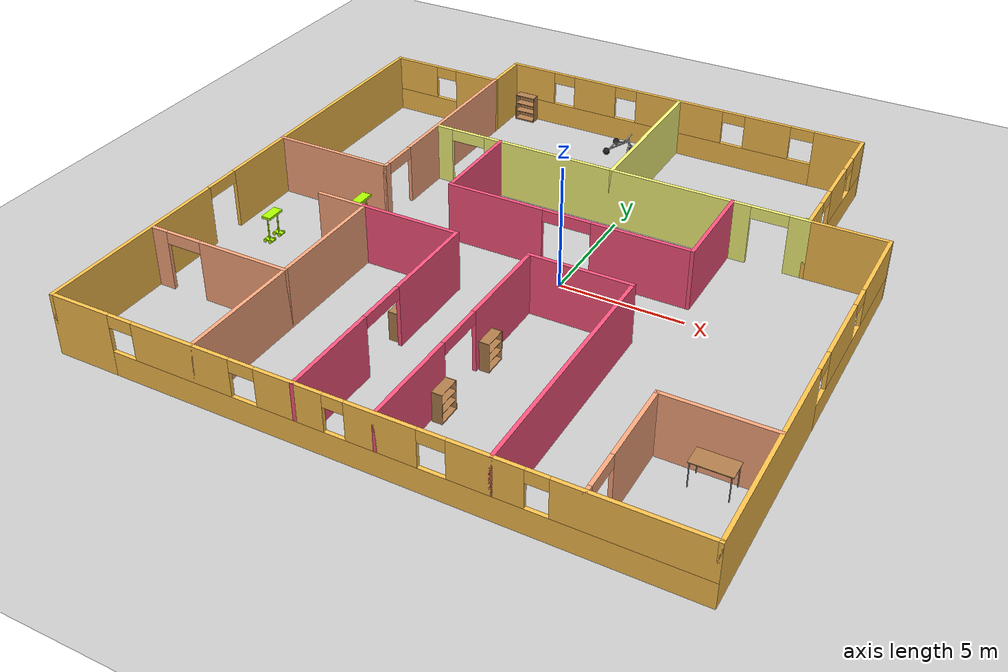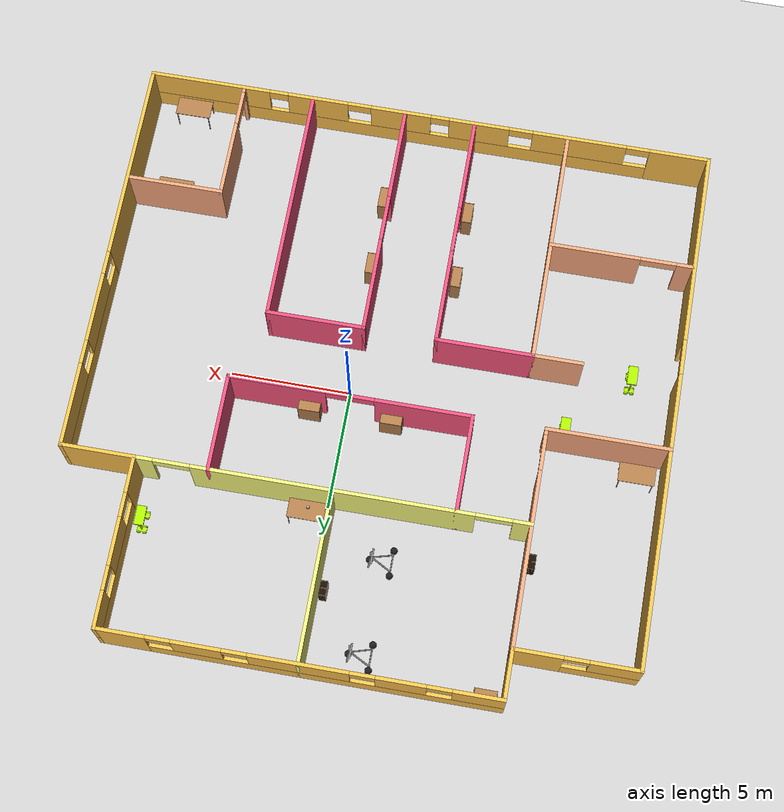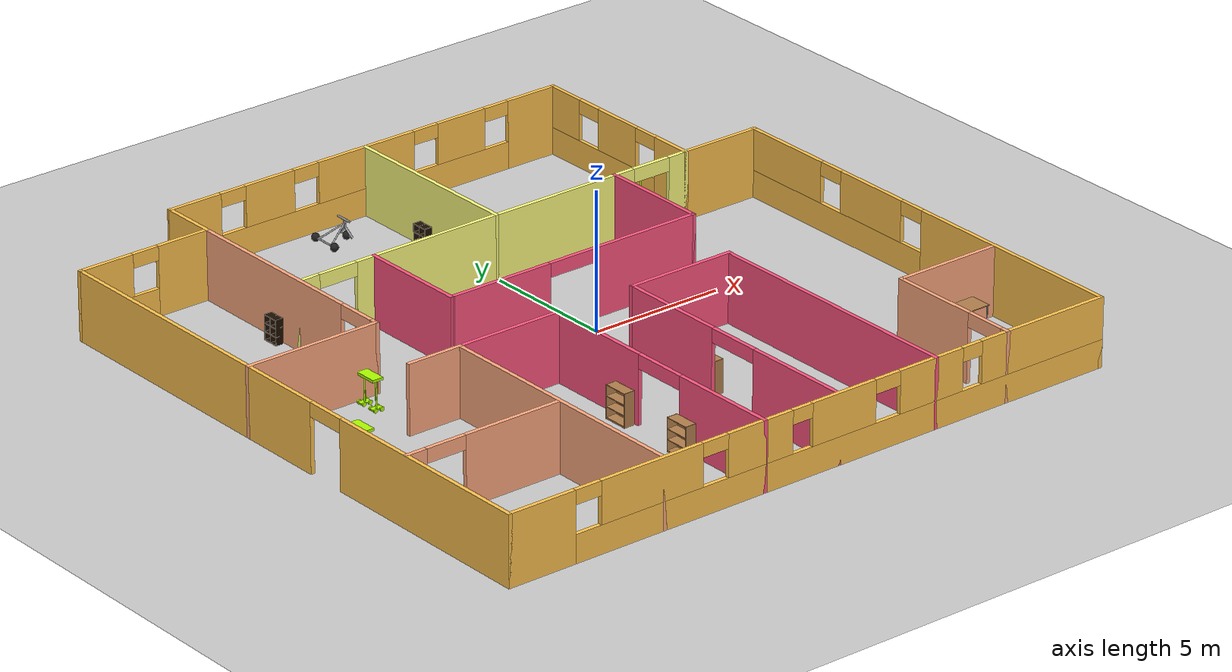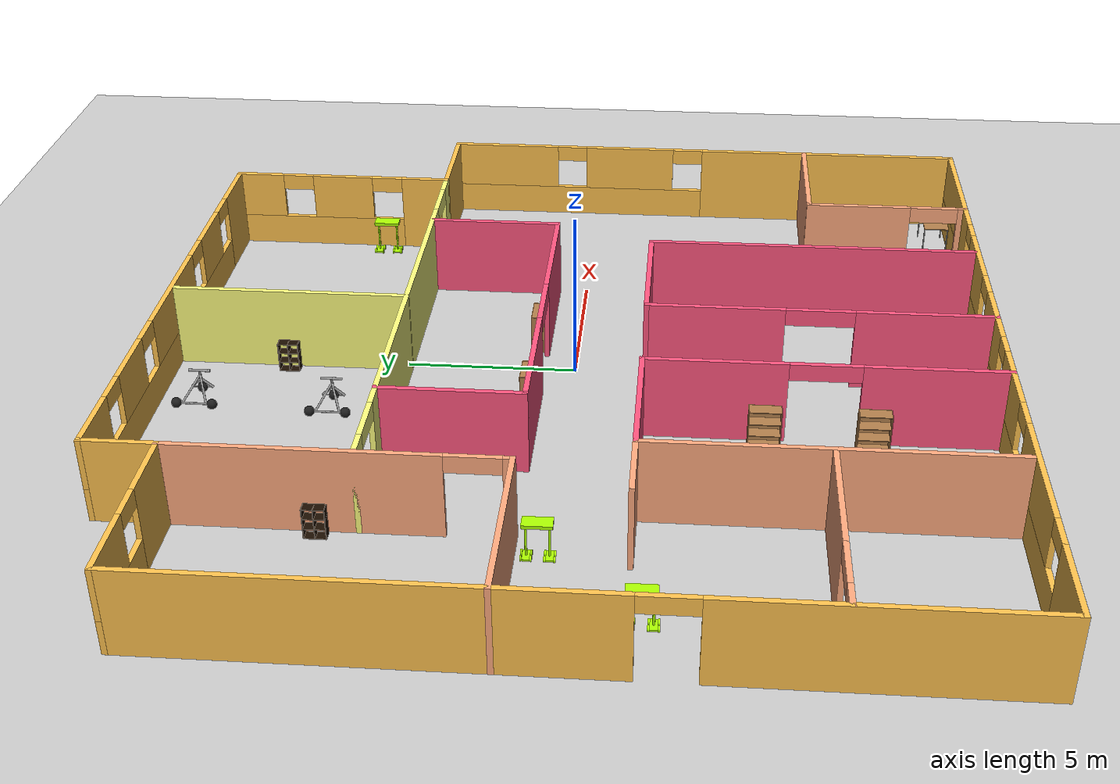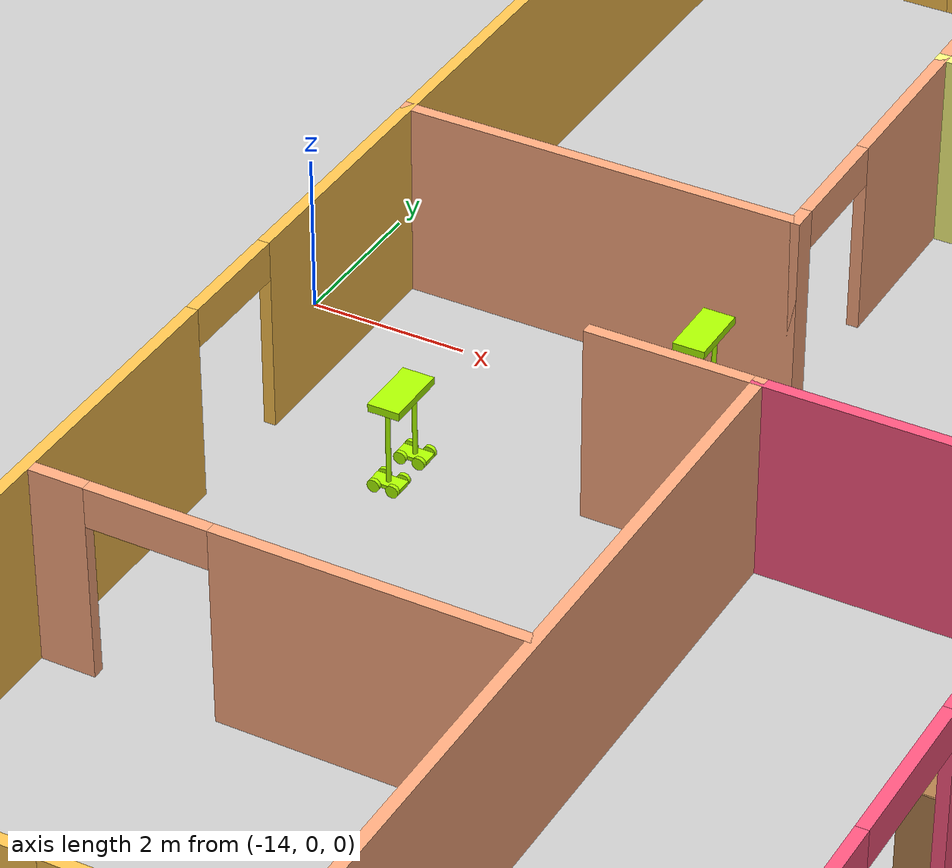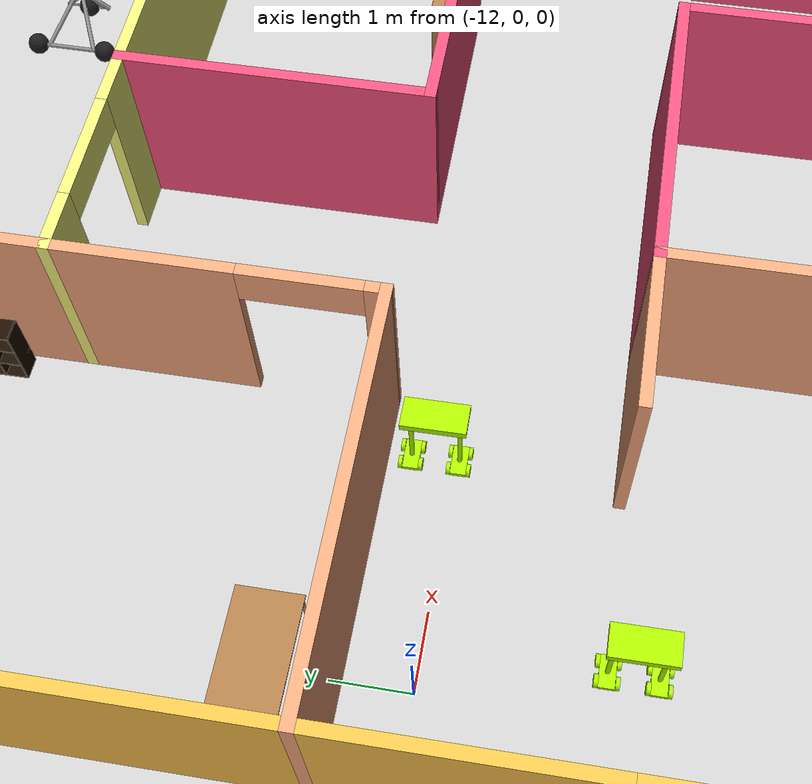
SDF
<sdf version="1.6">
 <world name="default">
  <light name="sun" type="directional">
   <pose>0 0 10 0 -0 0</pose>
   <diffuse>0.8 0.8 0.8 1</diffuse>
   <specular>0.2 0.2 0.2 1</specular>
   <attenuation>
    <range>1000</range>
    <constant>0.9</constant>
    <linear>0.01</linear>
    <quadratic>0.001</quadratic>
   </attenuation>
   <direction>-0.5 0.1 -0.9</direction>
  </light>
  <model name="ground_plane">
   <static>1</static>
   <link name="link">
    <collision name="collision">
     <geometry><plane><normal>0 0 1</normal><size>100 100</size></plane></geometry>
     <surface><friction><ode><mu>100</mu><mu2>50</mu2></ode></friction></surface>
    </collision>
    <visual name="visual">
     <cast_shadows>0</cast_shadows>
     <geometry><plane><normal>0 0 1</normal><size>100 100</size></plane></geometry>
     <material>
      <script><uri>file://media/materials/scripts/gazebo.material</uri><name>Gazebo/Grey</name></script>
     </material>
    </visual>
   </link>
  </model>
  <gravity>0 0 -9.8</gravity>
  <magnetic_field>6e-06 2.3e-05 -4.2e-05</magnetic_field>
  <atmosphere type="adiabatic"/>
  <physics name="default_physics" default="0" type="ode">
   <max_step_size>0.001</max_step_size>
   <real_time_factor>1</real_time_factor>
   <real_time_update_rate>1000</real_time_update_rate>
  </physics>
  <scene><ambient>0.4 0.4 0.4 1</ambient><background>0.7 0.7 0.7 1</background><shadows>1</shadows></scene>
  <spherical_coordinates>
   <surface_model>EARTH_WGS84</surface_model>
   <latitude_deg>0</latitude_deg>
   <longitude_deg>0</longitude_deg>
   <elevation>0</elevation>
   <heading_deg>0</heading_deg>
  </spherical_coordinates>
  <model name="myWorld">
   <pose>-1.22392 -0.0788 0 0 -0 0</pose>
   <link name="Wall_0">
    <pose>0 -12 0 0 -0 0</pose>
    <visual name="Wall_0_Visual_0">
     <pose>-10.7875 0 1.25 0 -0 0</pose>
     <geometry><box><size>2.575 0.15 2.5</size></box></geometry>
     <material>
      <script><uri>file://media/materials/scripts/gazebo.material</uri><name>Gazebo/Grey</name></script>
      <ambient>1 0.764706 0.305882 1</ambient>
     </material>
     <meta><layer>0</layer></meta>
    </visual>
    <collision name="Wall_0_Collision_0">
     <geometry><box><size>2.575 0.15 2.5</size></box></geometry>
     <pose>-10.7875 0 1.25 0 -0 0</pose>
    </collision>
    <visual name="Wall_0_Visual_1">
     <pose>1.2875 0 0.5 0 -0 0</pose>
     <geometry><box><size>21.575 0.15 1</size></box></geometry>
     <material>
      <script><uri>file://media/materials/scripts/gazebo.material</uri><name>Gazebo/Grey</name></script>
      <ambient>1 0.764706 0.305882 1</ambient>
     </material>
     <meta><layer>0</layer></meta>
    </visual>
    <collision name="Wall_0_Collision_1">
     <geometry><box><size>21.575 0.15 1</size></box></geometry>
     <pose>1.2875 0 0.5 0 -0 0</pose>
    </collision>
    <visual name="Wall_0_Visual_2">
     <pose>-6.495 0 1.75 0 -0 0</pose>
     <geometry><box><size>4.01 0.15 1.5</size></box></geometry>
     <material>
      <script><uri>file://media/materials/scripts/gazebo.material</uri><name>Gazebo/Grey</name></script>
      <ambient>1 0.764706 0.305882 1</ambient>
     </material>
     <meta><layer>0</layer></meta>
    </visual>
    <collision name="Wall_0_Collision_2">
     <geometry><box><size>4.01 0.15 1.5</size></box></geometry>
     <pose>-6.495 0 1.75 0 -0 0</pose>
    </collision>
    <visual name="Wall_0_Visual_3">
     <pose>-2.195 0 1.75 0 -0 0</pose>
     <geometry><box><size>2.59 0.15 1.5</size></box></geometry>
     <material>
      <script><uri>file://media/materials/scripts/gazebo.material</uri><name>Gazebo/Grey</name></script>
      <ambient>1 0.764706 0.305882 1</ambient>
     </material>
     <meta><layer>0</layer></meta>
    </visual>
    <collision name="Wall_0_Collision_3">
     <geometry><box><size>2.59 0.15 1.5</size></box></geometry>
     <pose>-2.195 0 1.75 0 -0 0</pose>
    </collision>
    <visual name="Wall_0_Visual_4">
     <pose>1.195 0 1.75 0 -0 0</pose>
     <geometry><box><size>2.59 0.15 1.5</size></box></geometry>
     <material>
      <script><uri>file://media/materials/scripts/gazebo.material</uri><name>Gazebo/Grey</name></script>
      <ambient>1 0.764706 0.305882 1</ambient>
     </material>
     <meta><layer>0</layer></meta>
    </visual>
    <collision name="Wall_0_Collision_4">
     <geometry><box><size>2.59 0.15 1.5</size></box></geometry>
     <pose>1.195 0 1.75 0 -0 0</pose>
    </collision>
    <visual name="Wall_0_Visual_5">
     <pose>4.795 0 1.75 0 -0 0</pose>
     <geometry><box><size>2.61 0.15 1.5</size></box></geometry>
     <material>
      <script><uri>file://media/materials/scripts/gazebo.material</uri><name>Gazebo/Grey</name></script>
      <ambient>1 0.764706 0.305882 1</ambient>
     </material>
     <meta><layer>0</layer></meta>
    </visual>
    <collision name="Wall_0_Collision_5">
     <geometry><box><size>2.61 0.15 1.5</size></box></geometry>
     <pose>4.795 0 1.75 0 -0 0</pose>
    </collision>
    <visual name="Wall_0_Visual_6">
     <pose>9.4875 0 1.75 0 -0 0</pose>
     <geometry><box><size>5.175 0.15 1.5</size></box></geometry>
     <material>
      <script><uri>file://media/materials/scripts/gazebo.material</uri><name>Gazebo/Grey</name></script>
      <ambient>1 0.764706 0.305882 1</ambient>
     </material>
     <meta><layer>0</layer></meta>
    </visual>
    <collision name="Wall_0_Collision_6">
     <geometry><box><size>5.175 0.15 1.5</size></box></geometry>
     <pose>9.4875 0 1.75 0 -0 0</pose>
    </collision>
    <visual name="Wall_0_Visual_7">
     <pose>-9 0 2.25 0 -0 0</pose>
     <geometry><box><size>1 0.15 0.5</size></box></geometry>
     <material>
      <script><uri>file://media/materials/scripts/gazebo.material</uri><name>Gazebo/Grey</name></script>
      <ambient>1 0.764706 0.305882 1</ambient>
     </material>
     <meta><layer>0</layer></meta>
    </visual>
    <collision name="Wall_0_Collision_7">
     <geometry><box><size>1 0.15 0.5</size></box></geometry>
     <pose>-9 0 2.25 0 -0 0</pose>
    </collision>
    <visual name="Wall_0_Visual_8">
     <pose>-3.99 0 2.25 0 -0 0</pose>
     <geometry><box><size>1 0.15 0.5</size></box></geometry>
     <material>
      <script><uri>file://media/materials/scripts/gazebo.material</uri><name>Gazebo/Grey</name></script>
      <ambient>1 0.764706 0.305882 1</ambient>
     </material>
     <meta><layer>0</layer></meta>
    </visual>
    <collision name="Wall_0_Collision_8">
     <geometry><box><size>1 0.15 0.5</size></box></geometry>
     <pose>-3.99 0 2.25 0 -0 0</pose>
    </collision>
    <visual name="Wall_0_Visual_9">
     <pose>-0.5 0 2.25 0 -0 0</pose>
     <geometry><box><size>0.8 0.15 0.5</size></box></geometry>
     <material>
      <script><uri>file://media/materials/scripts/gazebo.material</uri><name>Gazebo/Grey</name></script>
      <ambient>1 0.764706 0.305882 1</ambient>
     </material>
     <meta><layer>0</layer></meta>
    </visual>
    <collision name="Wall_0_Collision_9">
     <geometry><box><size>0.8 0.15 0.5</size></box></geometry>
     <pose>-0.5 0 2.25 0 -0 0</pose>
    </collision>
    <visual name="Wall_0_Visual_10">
     <pose>2.99 0 2.25 0 -0 0</pose>
     <geometry><box><size>1 0.15 0.5</size></box></geometry>
     <material>
      <script><uri>file://media/materials/scripts/gazebo.material</uri><name>Gazebo/Grey</name></script>
      <ambient>1 0.764706 0.305882 1</ambient>
     </material>
     <meta><layer>0</layer></meta>
    </visual>
    <collision name="Wall_0_Collision_10">
     <geometry><box><size>1 0.15 0.5</size></box></geometry>
     <pose>2.99 0 2.25 0 -0 0</pose>
    </collision>
    <visual name="Wall_0_Visual_11">
     <pose>6.5 0 2.25 0 -0 0</pose>
     <geometry><box><size>0.8 0.15 0.5</size></box></geometry>
     <material>
      <script><uri>file://media/materials/scripts/gazebo.material</uri><name>Gazebo/Grey</name></script>
      <ambient>1 0.764706 0.305882 1</ambient>
     </material>
     <meta><layer>0</layer></meta>
    </visual>
    <collision name="Wall_0_Collision_11">
     <geometry><box><size>0.8 0.15 0.5</size></box></geometry>
     <pose>6.5 0 2.25 0 -0 0</pose>
    </collision>
   </link>
   <link name="Wall_10">
    <collision name="Wall_10_Collision">
     <geometry><box><size>10.15 0.15 2.5</size></box></geometry>
     <pose>0 0 1.25 0 -0 0</pose>
    </collision>
    <visual name="Wall_10_Visual">
     <pose>0 0 1.25 0 -0 0</pose>
     <geometry><box><size>10.15 0.15 2.5</size></box></geometry>
     <material>
      <script><uri>file://media/materials/scripts/gazebo.material</uri><name>Gazebo/Grey</name></script>
      <ambient>1 0.666667 0.498039 1</ambient>
     </material>
     <meta><layer>0</layer></meta>
    </visual>
    <pose>-6 -7 0 0 -0 1.5708</pose>
   </link>
   <link name="Wall_12">
    <pose>-9 -7 0 0 -0 0</pose>
    <visual name="Wall_12_Visual_0">
     <pose>-2.6625 0 1.25 0 -0 0</pose>
     <geometry><box><size>0.825 0.15 2.5</size></box></geometry>
     <material>
      <script><uri>file://media/materials/scripts/gazebo.material</uri><name>Gazebo/Grey</name></script>
      <ambient>1 0.666667 0.498039 1</ambient>
     </material>
     <meta><layer>0</layer></meta>
    </visual>
    <collision name="Wall_12_Collision_0">
     <geometry><box><size>0.825 0.15 2.5</size></box></geometry>
     <pose>-2.6625 0 1.25 0 -0 0</pose>
    </collision>
    <visual name="Wall_12_Visual_1">
     <pose>1.1625 0 1.25 0 -0 0</pose>
     <geometry><box><size>3.825 0.15 2.5</size></box></geometry>
     <material>
      <script><uri>file://media/materials/scripts/gazebo.material</uri><name>Gazebo/Grey</name></script>
      <ambient>1 0.666667 0.498039 1</ambient>
     </material>
     <meta><layer>0</layer></meta>
    </visual>
    <collision name="Wall_12_Collision_1">
     <geometry><box><size>3.825 0.15 2.5</size></box></geometry>
     <pose>1.1625 0 1.25 0 -0 0</pose>
    </collision>
    <visual name="Wall_12_Visual_2">
     <pose>-1.5 0 2.25 0 -0 0</pose>
     <geometry><box><size>1.5 0.15 0.5</size></box></geometry>
     <material>
      <script><uri>file://media/materials/scripts/gazebo.material</uri><name>Gazebo/Grey</name></script>
      <ambient>1 0.666667 0.498039 1</ambient>
     </material>
     <meta><layer>0</layer></meta>
    </visual>
    <collision name="Wall_12_Collision_2">
     <geometry><box><size>1.5 0.15 0.5</size></box></geometry>
     <pose>-1.5 0 2.25 0 -0 0</pose>
    </collision>
   </link>
   <link name="Wall_13">
    <collision name="Wall_13_Collision">
     <geometry><box><size>2.15 0.15 2.5</size></box></geometry>
     <pose>0 0 1.25 0 -0 0</pose>
    </collision>
    <visual name="Wall_13_Visual">
     <pose>0 0 1.25 0 -0 0</pose>
     <geometry><box><size>2.15 0.15 2.5</size></box></geometry>
     <material>
      <script><uri>file://media/materials/scripts/gazebo.material</uri><name>Gazebo/Grey</name></script>
      <ambient>1 0.666667 0.498039 1</ambient>
     </material>
     <meta><layer>0</layer></meta>
    </visual>
    <pose>-7 -2 0 0 -0 0</pose>
   </link>
   <link name="Wall_14">
    <collision name="Wall_14_Collision">
     <geometry><box><size>4.15 0.15 2.5</size></box></geometry>
     <pose>0 0 1.25 0 -0 0</pose>
    </collision>
    <visual name="Wall_14_Visual">
     <pose>0 0 1.25 0 -0 0</pose>
     <geometry><box><size>4.15 0.15 2.5</size></box></geometry>
     <material>
      <script><uri>file://media/materials/scripts/gazebo.material</uri><name>Gazebo/Grey</name></script>
      <ambient>1 0.333333 0.498039 1</ambient>
     </material>
     <meta><layer>0</layer></meta>
    </visual>
    <pose>-4 -2 0 0 -0 0</pose>
   </link>
   <link name="Wall_16">
    <pose>-2 -7 0 0 0 -1.5708</pose>
    <visual name="Wall_16_Visual_0">
     <pose>-3.0375 0 1.25 0 -0 0</pose>
     <geometry><box><size>4.075 0.15 2.5</size></box></geometry>
     <material>
      <script><uri>file://media/materials/scripts/gazebo.material</uri><name>Gazebo/Grey</name></script>
      <ambient>1 0.333333 0.498039 1</ambient>
     </material>
     <meta><layer>0</layer></meta>
    </visual>
    <collision name="Wall_16_Collision_0">
     <geometry><box><size>4.075 0.15 2.5</size></box></geometry>
     <pose>-3.0375 0 1.25 0 -0 0</pose>
    </collision>
    <visual name="Wall_16_Visual_1">
     <pose>3.0375 0 1.25 0 -0 0</pose>
     <geometry><box><size>4.075 0.15 2.5</size></box></geometry>
     <material>
      <script><uri>file://media/materials/scripts/gazebo.material</uri><name>Gazebo/Grey</name></script>
      <ambient>1 0.333333 0.498039 1</ambient>
     </material>
     <meta><layer>0</layer></meta>
    </visual>
    <collision name="Wall_16_Collision_1">
     <geometry><box><size>4.075 0.15 2.5</size></box></geometry>
     <pose>3.0375 0 1.25 0 -0 0</pose>
    </collision>
    <visual name="Wall_16_Visual_2">
     <pose>0 0 2.25 0 -0 0</pose>
     <geometry><box><size>2 0.15 0.5</size></box></geometry>
     <material>
      <script><uri>file://media/materials/scripts/gazebo.material</uri><name>Gazebo/Grey</name></script>
      <ambient>1 0.333333 0.498039 1</ambient>
     </material>
     <meta><layer>0</layer></meta>
    </visual>
    <collision name="Wall_16_Collision_2">
     <geometry><box><size>2 0.15 0.5</size></box></geometry>
     <pose>0 0 2.25 0 -0 0</pose>
    </collision>
   </link>
   <link name="Wall_18">
    <collision name="Wall_18_Collision">
     <geometry><box><size>4.15 0.15 2.5</size></box></geometry>
     <pose>0 0 1.25 0 -0 0</pose>
    </collision>
    <visual name="Wall_18_Visual">
     <pose>0 0 1.25 0 -0 0</pose>
     <geometry><box><size>4.15 0.15 2.5</size></box></geometry>
     <material>
      <script><uri>file://media/materials/scripts/gazebo.material</uri><name>Gazebo/Grey</name></script>
      <ambient>1 0.333333 0.498039 1</ambient>
     </material>
     <meta><layer>0</layer></meta>
    </visual>
    <pose>3 -2 0 0 -0 0</pose>
   </link>
   <link name="Wall_2">
    <pose>12 -3.5 0 0 -0 1.5708</pose>
    <visual name="Wall_2_Visual_0">
     <pose>-4.2875 0 1.25 0 -0 0</pose>
     <geometry><box><size>8.575 0.15 2.5</size></box></geometry>
     <material>
      <script><uri>file://media/materials/scripts/gazebo.material</uri><name>Gazebo/Grey</name></script>
      <ambient>1 0.764706 0.305882 1</ambient>
     </material>
     <meta><layer>0</layer></meta>
    </visual>
    <collision name="Wall_2_Collision_0">
     <geometry><box><size>8.575 0.15 2.5</size></box></geometry>
     <pose>-4.2875 0 1.25 0 -0 0</pose>
    </collision>
    <visual name="Wall_2_Visual_1">
     <pose>4.2875 0 0.5 0 -0 0</pose>
     <geometry><box><size>8.575 0.15 1</size></box></geometry>
     <material>
      <script><uri>file://media/materials/scripts/gazebo.material</uri><name>Gazebo/Grey</name></script>
      <ambient>1 0.764706 0.305882 1</ambient>
     </material>
     <meta><layer>0</layer></meta>
    </visual>
    <collision name="Wall_2_Collision_1">
     <geometry><box><size>8.575 0.15 1</size></box></geometry>
     <pose>4.2875 0 0.5 0 -0 0</pose>
    </collision>
    <visual name="Wall_2_Visual_2">
     <pose>2.5 0 1.75 0 -0 0</pose>
     <geometry><box><size>3 0.15 1.5</size></box></geometry>
     <material>
      <script><uri>file://media/materials/scripts/gazebo.material</uri><name>Gazebo/Grey</name></script>
      <ambient>1 0.764706 0.305882 1</ambient>
     </material>
     <meta><layer>0</layer></meta>
    </visual>
    <collision name="Wall_2_Collision_2">
     <geometry><box><size>3 0.15 1.5</size></box></geometry>
     <pose>2.5 0 1.75 0 -0 0</pose>
    </collision>
    <visual name="Wall_2_Visual_3">
     <pose>6.7875 0 1.75 0 -0 0</pose>
     <geometry><box><size>3.575 0.15 1.5</size></box></geometry>
     <material>
      <script><uri>file://media/materials/scripts/gazebo.material</uri><name>Gazebo/Grey</name></script>
      <ambient>1 0.764706 0.305882 1</ambient>
     </material>
     <meta><layer>0</layer></meta>
    </visual>
    <collision name="Wall_2_Collision_3">
     <geometry><box><size>3.575 0.15 1.5</size></box></geometry>
     <pose>6.7875 0 1.75 0 -0 0</pose>
    </collision>
    <visual name="Wall_2_Visual_4">
     <pose>0.5 0 2.25 0 -0 0</pose>
     <geometry><box><size>1 0.15 0.5</size></box></geometry>
     <material>
      <script><uri>file://media/materials/scripts/gazebo.material</uri><name>Gazebo/Grey</name></script>
      <ambient>1 0.764706 0.305882 1</ambient>
     </material>
     <meta><layer>0</layer></meta>
    </visual>
    <collision name="Wall_2_Collision_4">
     <geometry><box><size>1 0.15 0.5</size></box></geometry>
     <pose>0.5 0 2.25 0 -0 0</pose>
    </collision>
    <visual name="Wall_2_Visual_5">
     <pose>4.5 0 2.25 0 -0 0</pose>
     <geometry><box><size>1 0.15 0.5</size></box></geometry>
     <material>
      <script><uri>file://media/materials/scripts/gazebo.material</uri><name>Gazebo/Grey</name></script>
      <ambient>1 0.764706 0.305882 1</ambient>
     </material>
     <meta><layer>0</layer></meta>
    </visual>
    <collision name="Wall_2_Collision_5">
     <geometry><box><size>1 0.15 0.5</size></box></geometry>
     <pose>4.5 0 2.25 0 -0 0</pose>
    </collision>
   </link>
   <link name="Wall_20">
    <pose>1 -7 0 0 0 -1.5708</pose>
    <visual name="Wall_20_Visual_0">
     <pose>-3.0375 0 1.25 0 -0 0</pose>
     <geometry><box><size>4.075 0.15 2.5</size></box></geometry>
     <material>
      <script><uri>file://media/materials/scripts/gazebo.material</uri><name>Gazebo/Grey</name></script>
      <ambient>1 0.333333 0.498039 1</ambient>
     </material>
     <meta><layer>0</layer></meta>
    </visual>
    <collision name="Wall_20_Collision_0">
     <geometry><box><size>4.075 0.15 2.5</size></box></geometry>
     <pose>-3.0375 0 1.25 0 -0 0</pose>
    </collision>
    <visual name="Wall_20_Visual_1">
     <pose>3.0375 0 1.25 0 -0 0</pose>
     <geometry><box><size>4.075 0.15 2.5</size></box></geometry>
     <material>
      <script><uri>file://media/materials/scripts/gazebo.material</uri><name>Gazebo/Grey</name></script>
      <ambient>1 0.333333 0.498039 1</ambient>
     </material>
     <meta><layer>0</layer></meta>
    </visual>
    <collision name="Wall_20_Collision_1">
     <geometry><box><size>4.075 0.15 2.5</size></box></geometry>
     <pose>3.0375 0 1.25 0 -0 0</pose>
    </collision>
    <visual name="Wall_20_Visual_2">
     <pose>0 0 2.25 0 -0 0</pose>
     <geometry><box><size>2 0.15 0.5</size></box></geometry>
     <material>
      <script><uri>file://media/materials/scripts/gazebo.material</uri><name>Gazebo/Grey</name></script>
      <ambient>1 0.333333 0.498039 1</ambient>
     </material>
     <meta><layer>0</layer></meta>
    </visual>
    <collision name="Wall_20_Collision_2">
     <geometry><box><size>2 0.15 0.5</size></box></geometry>
     <pose>0 0 2.25 0 -0 0</pose>
    </collision>
   </link>
   <link name="Wall_22">
    <collision name="Wall_22_Collision">
     <geometry><box><size>10.15 0.15 2.5</size></box></geometry>
     <pose>0 0 1.25 0 -0 0</pose>
    </collision>
    <visual name="Wall_22_Visual">
     <pose>0 0 1.25 0 -0 0</pose>
     <geometry><box><size>10.15 0.15 2.5</size></box></geometry>
     <material>
      <script><uri>file://media/materials/scripts/gazebo.material</uri><name>Gazebo/Grey</name></script>
      <ambient>1 0.333333 0.498039 1</ambient>
     </material>
     <meta><layer>0</layer></meta>
    </visual>
    <pose>5 -7 0 0 0 -1.5708</pose>
   </link>
   <link name="Wall_24">
    <collision name="Wall_24_Collision">
     <geometry><box><size>5.15 0.15 2.5</size></box></geometry>
     <pose>0 0 1.25 0 -0 0</pose>
    </collision>
    <visual name="Wall_24_Visual">
     <pose>0 0 1.25 0 -0 0</pose>
     <geometry><box><size>5.15 0.15 2.5</size></box></geometry>
     <material>
      <script><uri>file://media/materials/scripts/gazebo.material</uri><name>Gazebo/Grey</name></script>
      <ambient>1 0.666667 0.498039 1</ambient>
     </material>
     <meta><layer>0</layer></meta>
    </visual>
    <pose>-9.5 1 0 0 -0 0</pose>
   </link>
   <link name="Wall_25">
    <pose>-7 5.5 0 0 -0 1.5708</pose>
    <visual name="Wall_25_Visual_0">
     <pose>-4.4125 0 1.25 0 -0 0</pose>
     <geometry><box><size>0.325 0.15 2.5</size></box></geometry>
     <material>
      <script><uri>file://media/materials/scripts/gazebo.material</uri><name>Gazebo/Grey</name></script>
      <ambient>1 0.666667 0.498039 1</ambient>
     </material>
     <meta><layer>0</layer></meta>
    </visual>
    <collision name="Wall_25_Collision_0">
     <geometry><box><size>0.325 0.15 2.5</size></box></geometry>
     <pose>-4.4125 0 1.25 0 -0 0</pose>
    </collision>
    <visual name="Wall_25_Visual_1">
     <pose>0.9125 0 1.25 0 -0 0</pose>
     <geometry><box><size>7.325 0.15 2.5</size></box></geometry>
     <material>
      <script><uri>file://media/materials/scripts/gazebo.material</uri><name>Gazebo/Grey</name></script>
      <ambient>1 0.666667 0.498039 1</ambient>
     </material>
     <meta><layer>0</layer></meta>
    </visual>
    <collision name="Wall_25_Collision_1">
     <geometry><box><size>7.325 0.15 2.5</size></box></geometry>
     <pose>0.9125 0 1.25 0 -0 0</pose>
    </collision>
    <visual name="Wall_25_Visual_2">
     <pose>-3.5 0 2.25 0 -0 0</pose>
     <geometry><box><size>1.5 0.15 0.5</size></box></geometry>
     <material>
      <script><uri>file://media/materials/scripts/gazebo.material</uri><name>Gazebo/Grey</name></script>
      <ambient>1 0.666667 0.498039 1</ambient>
     </material>
     <meta><layer>0</layer></meta>
    </visual>
    <collision name="Wall_25_Collision_2">
     <geometry><box><size>1.5 0.15 0.5</size></box></geometry>
     <pose>-3.5 0 2.25 0 -0 0</pose>
    </collision>
   </link>
   <link name="Wall_27">
    <pose>1 5 0 0 -0 0</pose>
    <visual name="Wall_27_Visual_0">
     <pose>-7.6625 0 1.25 0 -0 0</pose>
     <geometry><box><size>0.825 0.15 2.5</size></box></geometry>
     <material>
      <script><uri>file://media/materials/scripts/gazebo.material</uri><name>Gazebo/Grey</name></script>
      <ambient>1 1 0.498039 1</ambient>
     </material>
     <meta><layer>0</layer></meta>
    </visual>
    <collision name="Wall_27_Collision_0">
     <geometry><box><size>0.825 0.15 2.5</size></box></geometry>
     <pose>-7.6625 0 1.25 0 -0 0</pose>
    </collision>
    <visual name="Wall_27_Visual_1">
     <pose>0 0 1.25 0 -0 0</pose>
     <geometry><box><size>11.5 0.15 2.5</size></box></geometry>
     <material>
      <script><uri>file://media/materials/scripts/gazebo.material</uri><name>Gazebo/Grey</name></script>
      <ambient>1 1 0.498039 1</ambient>
     </material>
     <meta><layer>0</layer></meta>
    </visual>
    <collision name="Wall_27_Collision_1">
     <geometry><box><size>11.5 0.15 2.5</size></box></geometry>
     <pose>0 0 1.25 0 -0 0</pose>
    </collision>
    <visual name="Wall_27_Visual_2">
     <pose>7.6625 0 1.25 0 -0 0</pose>
     <geometry><box><size>0.825 0.15 2.5</size></box></geometry>
     <material>
      <script><uri>file://media/materials/scripts/gazebo.material</uri><name>Gazebo/Grey</name></script>
      <ambient>1 1 0.498039 1</ambient>
     </material>
     <meta><layer>0</layer></meta>
    </visual>
    <collision name="Wall_27_Collision_2">
     <geometry><box><size>0.825 0.15 2.5</size></box></geometry>
     <pose>7.6625 0 1.25 0 -0 0</pose>
    </collision>
    <visual name="Wall_27_Visual_3">
     <pose>-6.5 0 2.25 0 -0 0</pose>
     <geometry><box><size>1.5 0.15 0.5</size></box></geometry>
     <material>
      <script><uri>file://media/materials/scripts/gazebo.material</uri><name>Gazebo/Grey</name></script>
      <ambient>1 1 0.498039 1</ambient>
     </material>
     <meta><layer>0</layer></meta>
    </visual>
    <collision name="Wall_27_Collision_3">
     <geometry><box><size>1.5 0.15 0.5</size></box></geometry>
     <pose>-6.5 0 2.25 0 -0 0</pose>
    </collision>
    <visual name="Wall_27_Visual_4">
     <pose>6.5 0 2.25 0 -0 0</pose>
     <geometry><box><size>1.5 0.15 0.5</size></box></geometry>
     <material>
      <script><uri>file://media/materials/scripts/gazebo.material</uri><name>Gazebo/Grey</name></script>
      <ambient>1 1 0.498039 1</ambient>
     </material>
     <meta><layer>0</layer></meta>
    </visual>
    <collision name="Wall_27_Collision_4">
     <geometry><box><size>1.5 0.15 0.5</size></box></geometry>
     <pose>6.5 0 2.25 0 -0 0</pose>
    </collision>
   </link>
   <link name="Wall_29">
    <collision name="Wall_29_Collision">
     <geometry><box><size>4.15 0.15 2.5</size></box></geometry>
     <pose>0 0 1.25 0 -0 0</pose>
    </collision>
    <visual name="Wall_29_Visual">
     <pose>0 0 1.25 0 -0 0</pose>
     <geometry><box><size>4.15 0.15 2.5</size></box></geometry>
     <material>
      <script><uri>file://media/materials/scripts/gazebo.material</uri><name>Gazebo/Grey</name></script>
      <ambient>1 0.333333 0.498039 1</ambient>
     </material>
     <meta><layer>0</layer></meta>
    </visual>
    <pose>-4 3 0 0 0 -1.5708</pose>
   </link>
   <link name="Wall_3">
    <collision name="Wall_3_Collision">
     <geometry><box><size>3.15 0.15 2.5</size></box></geometry>
     <pose>0 0 1.25 0 -0 0</pose>
    </collision>
    <visual name="Wall_3_Visual">
     <pose>0 0 1.25 0 -0 0</pose>
     <geometry><box><size>3.15 0.15 2.5</size></box></geometry>
     <material>
      <script><uri>file://media/materials/scripts/gazebo.material</uri><name>Gazebo/Grey</name></script>
      <ambient>1 0.764706 0.305882 1</ambient>
     </material>
     <meta><layer>0</layer></meta>
    </visual>
    <pose>10.5 5 0 0 -0 3.14159</pose>
   </link>
   <link name="Wall_30">
    <pose>1 1 0 0 -0 0</pose>
    <visual name="Wall_30_Visual_0">
     <pose>-3.0375 0 1.25 0 -0 0</pose>
     <geometry><box><size>4.075 0.15 2.5</size></box></geometry>
     <material>
      <script><uri>file://media/materials/scripts/gazebo.material</uri><name>Gazebo/Grey</name></script>
      <ambient>1 0.333333 0.498039 1</ambient>
     </material>
     <meta><layer>0</layer></meta>
    </visual>
    <collision name="Wall_30_Collision_0">
     <geometry><box><size>4.075 0.15 2.5</size></box></geometry>
     <pose>-3.0375 0 1.25 0 -0 0</pose>
    </collision>
    <visual name="Wall_30_Visual_1">
     <pose>3.0375 0 1.25 0 -0 0</pose>
     <geometry><box><size>4.075 0.15 2.5</size></box></geometry>
     <material>
      <script><uri>file://media/materials/scripts/gazebo.material</uri><name>Gazebo/Grey</name></script>
      <ambient>1 0.333333 0.498039 1</ambient>
     </material>
     <meta><layer>0</layer></meta>
    </visual>
    <collision name="Wall_30_Collision_1">
     <geometry><box><size>4.075 0.15 2.5</size></box></geometry>
     <pose>3.0375 0 1.25 0 -0 0</pose>
    </collision>
    <visual name="Wall_30_Visual_2">
     <pose>0 0 2.25 0 -0 0</pose>
     <geometry><box><size>2 0.15 0.5</size></box></geometry>
     <material>
      <script><uri>file://media/materials/scripts/gazebo.material</uri><name>Gazebo/Grey</name></script>
      <ambient>1 0.333333 0.498039 1</ambient>
     </material>
     <meta><layer>0</layer></meta>
    </visual>
    <collision name="Wall_30_Collision_2">
     <geometry><box><size>2 0.15 0.5</size></box></geometry>
     <pose>0 0 2.25 0 -0 0</pose>
    </collision>
   </link>
   <link name="Wall_32">
    <collision name="Wall_32_Collision">
     <geometry><box><size>4.15 0.15 2.5</size></box></geometry>
     <pose>0 0 1.25 0 -0 0</pose>
    </collision>
    <visual name="Wall_32_Visual">
     <pose>0 0 1.25 0 -0 0</pose>
     <geometry><box><size>4.15 0.15 2.5</size></box></geometry>
     <material>
      <script><uri>file://media/materials/scripts/gazebo.material</uri><name>Gazebo/Grey</name></script>
      <ambient>1 0.333333 0.498039 1</ambient>
     </material>
     <meta><layer>0</layer></meta>
    </visual>
    <pose>6 3 0 0 -0 1.5708</pose>
   </link>
   <link name="Wall_34">
    <collision name="Wall_34_Collision">
     <geometry><box><size>7.15 0.15 2.5</size></box></geometry>
     <pose>0 0 1.25 0 -0 0</pose>
    </collision>
    <visual name="Wall_34_Visual">
     <pose>0 0 1.25 0 -0 0</pose>
     <geometry><box><size>7.15 0.15 2.5</size></box></geometry>
     <material>
      <script><uri>file://media/materials/scripts/gazebo.material</uri><name>Gazebo/Grey</name></script>
      <ambient>1 1 0.498039 1</ambient>
     </material>
     <meta><layer>0</layer></meta>
    </visual>
    <pose>1 8.5 0 0 -0 1.5708</pose>
   </link>
   <link name="Wall_36">
    <pose>8 -9.5 0 0 -0 1.5708</pose>
    <visual name="Wall_36_Visual_0">
     <pose>-2.4125 0 1.25 0 -0 0</pose>
     <geometry><box><size>0.325 0.15 2.5</size></box></geometry>
     <material>
      <script><uri>file://media/materials/scripts/gazebo.material</uri><name>Gazebo/Grey</name></script>
      <ambient>1 0.666667 0.498039 1</ambient>
     </material>
     <meta><layer>0</layer></meta>
    </visual>
    <collision name="Wall_36_Collision_0">
     <geometry><box><size>0.325 0.15 2.5</size></box></geometry>
     <pose>-2.4125 0 1.25 0 -0 0</pose>
    </collision>
    <visual name="Wall_36_Visual_1">
     <pose>0.9125 0 1.25 0 -0 0</pose>
     <geometry><box><size>3.325 0.15 2.5</size></box></geometry>
     <material>
      <script><uri>file://media/materials/scripts/gazebo.material</uri><name>Gazebo/Grey</name></script>
      <ambient>1 0.666667 0.498039 1</ambient>
     </material>
     <meta><layer>0</layer></meta>
    </visual>
    <collision name="Wall_36_Collision_1">
     <geometry><box><size>3.325 0.15 2.5</size></box></geometry>
     <pose>0.9125 0 1.25 0 -0 0</pose>
    </collision>
    <visual name="Wall_36_Visual_2">
     <pose>-1.5 0 2.25 0 -0 0</pose>
     <geometry><box><size>1.5 0.15 0.5</size></box></geometry>
     <material>
      <script><uri>file://media/materials/scripts/gazebo.material</uri><name>Gazebo/Grey</name></script>
      <ambient>1 0.666667 0.498039 1</ambient>
     </material>
     <meta><layer>0</layer></meta>
    </visual>
    <collision name="Wall_36_Collision_2">
     <geometry><box><size>1.5 0.15 0.5</size></box></geometry>
     <pose>-1.5 0 2.25 0 -0 0</pose>
    </collision>
   </link>
   <link name="Wall_37">
    <collision name="Wall_37_Collision">
     <geometry><box><size>4.15 0.15 2.5</size></box></geometry>
     <pose>0 0 1.25 0 -0 0</pose>
    </collision>
    <visual name="Wall_37_Visual">
     <pose>0 0 1.25 0 -0 0</pose>
     <geometry><box><size>4.15 0.15 2.5</size></box></geometry>
     <material>
      <script><uri>file://media/materials/scripts/gazebo.material</uri><name>Gazebo/Grey</name></script>
      <ambient>1 0.666667 0.498039 1</ambient>
     </material>
     <meta><layer>0</layer></meta>
    </visual>
    <pose>10 -7 0 0 -0 0</pose>
   </link>
   <link name="Wall_4">
    <pose>9 8.5 0 0 -0 1.5708</pose>
    <visual name="Wall_4_Visual_0">
     <pose>-2.7875 0 1.25 0 -0 0</pose>
     <geometry><box><size>1.575 0.15 2.5</size></box></geometry>
     <material>
      <script><uri>file://media/materials/scripts/gazebo.material</uri><name>Gazebo/Grey</name></script>
      <ambient>1 0.764706 0.305882 1</ambient>
     </material>
     <meta><layer>0</layer></meta>
    </visual>
    <collision name="Wall_4_Collision_0">
     <geometry><box><size>1.575 0.15 2.5</size></box></geometry>
     <pose>-2.7875 0 1.25 0 -0 0</pose>
    </collision>
    <visual name="Wall_4_Visual_1">
     <pose>0.7875 0 0.5 0 -0 0</pose>
     <geometry><box><size>5.575 0.15 1</size></box></geometry>
     <material>
      <script><uri>file://media/materials/scripts/gazebo.material</uri><name>Gazebo/Grey</name></script>
      <ambient>1 0.764706 0.305882 1</ambient>
     </material>
     <meta><layer>0</layer></meta>
    </visual>
    <collision name="Wall_4_Collision_1">
     <geometry><box><size>5.575 0.15 1</size></box></geometry>
     <pose>0.7875 0 0.5 0 -0 0</pose>
    </collision>
    <visual name="Wall_4_Visual_2">
     <pose>0 0 1.75 0 -0 0</pose>
     <geometry><box><size>2 0.15 1.5</size></box></geometry>
     <material>
      <script><uri>file://media/materials/scripts/gazebo.material</uri><name>Gazebo/Grey</name></script>
      <ambient>1 0.764706 0.305882 1</ambient>
     </material>
     <meta><layer>0</layer></meta>
    </visual>
    <collision name="Wall_4_Collision_2">
     <geometry><box><size>2 0.15 1.5</size></box></geometry>
     <pose>0 0 1.75 0 -0 0</pose>
    </collision>
    <visual name="Wall_4_Visual_3">
     <pose>2.7875 0 1.75 0 -0 0</pose>
     <geometry><box><size>1.575 0.15 1.5</size></box></geometry>
     <material>
      <script><uri>file://media/materials/scripts/gazebo.material</uri><name>Gazebo/Grey</name></script>
      <ambient>1 0.764706 0.305882 1</ambient>
     </material>
     <meta><layer>0</layer></meta>
    </visual>
    <collision name="Wall_4_Collision_3">
     <geometry><box><size>1.575 0.15 1.5</size></box></geometry>
     <pose>2.7875 0 1.75 0 -0 0</pose>
    </collision>
    <visual name="Wall_4_Visual_4">
     <pose>-1.5 0 2.25 0 -0 0</pose>
     <geometry><box><size>1 0.15 0.5</size></box></geometry>
     <material>
      <script><uri>file://media/materials/scripts/gazebo.material</uri><name>Gazebo/Grey</name></script>
      <ambient>1 0.764706 0.305882 1</ambient>
     </material>
     <meta><layer>0</layer></meta>
    </visual>
    <collision name="Wall_4_Collision_4">
     <geometry><box><size>1 0.15 0.5</size></box></geometry>
     <pose>-1.5 0 2.25 0 -0 0</pose>
    </collision>
    <visual name="Wall_4_Visual_5">
     <pose>1.5 0 2.25 0 -0 0</pose>
     <geometry><box><size>1 0.15 0.5</size></box></geometry>
     <material>
      <script><uri>file://media/materials/scripts/gazebo.material</uri><name>Gazebo/Grey</name></script>
      <ambient>1 0.764706 0.305882 1</ambient>
     </material>
     <meta><layer>0</layer></meta>
    </visual>
    <collision name="Wall_4_Collision_5">
     <geometry><box><size>1 0.15 0.5</size></box></geometry>
     <pose>1.5 0 2.25 0 -0 0</pose>
    </collision>
   </link>
   <link name="Wall_5">
    <pose>1 12 0 0 -0 3.14159</pose>
    <visual name="Wall_5_Visual_0">
     <pose>-7.0375 0 1.25 0 -0 0</pose>
     <geometry><box><size>2.075 0.15 2.5</size></box></geometry>
     <material>
      <script><uri>file://media/materials/scripts/gazebo.material</uri><name>Gazebo/Grey</name></script>
      <ambient>1 0.764706 0.305882 1</ambient>
     </material>
     <meta><layer>0</layer></meta>
    </visual>
    <collision name="Wall_5_Collision_0">
     <geometry><box><size>2.075 0.15 2.5</size></box></geometry>
     <pose>-7.0375 0 1.25 0 -0 0</pose>
    </collision>
    <visual name="Wall_5_Visual_1">
     <pose>1.0375 0 0.5 0 -0 0</pose>
     <geometry><box><size>14.075 0.15 1</size></box></geometry>
     <material>
      <script><uri>file://media/materials/scripts/gazebo.material</uri><name>Gazebo/Grey</name></script>
      <ambient>1 0.764706 0.305882 1</ambient>
     </material>
     <meta><layer>0</layer></meta>
    </visual>
    <collision name="Wall_5_Collision_1">
     <geometry><box><size>14.075 0.15 1</size></box></geometry>
     <pose>1.0375 0 0.5 0 -0 0</pose>
    </collision>
    <visual name="Wall_5_Visual_2">
     <pose>-4 0 1.75 0 -0 0</pose>
     <geometry><box><size>2 0.15 1.5</size></box></geometry>
     <material>
      <script><uri>file://media/materials/scripts/gazebo.material</uri><name>Gazebo/Grey</name></script>
      <ambient>1 0.764706 0.305882 1</ambient>
     </material>
     <meta><layer>0</layer></meta>
    </visual>
    <collision name="Wall_5_Collision_2">
     <geometry><box><size>2 0.15 1.5</size></box></geometry>
     <pose>-4 0 1.75 0 -0 0</pose>
    </collision>
    <visual name="Wall_5_Visual_3">
     <pose>0 0 1.75 0 -0 0</pose>
     <geometry><box><size>4 0.15 1.5</size></box></geometry>
     <material>
      <script><uri>file://media/materials/scripts/gazebo.material</uri><name>Gazebo/Grey</name></script>
      <ambient>1 0.764706 0.305882 1</ambient>
     </material>
     <meta><layer>0</layer></meta>
    </visual>
    <collision name="Wall_5_Collision_3">
     <geometry><box><size>4 0.15 1.5</size></box></geometry>
     <pose>0 0 1.75 0 -0 0</pose>
    </collision>
    <visual name="Wall_5_Visual_4">
     <pose>4 0 1.75 0 -0 0</pose>
     <geometry><box><size>2 0.15 1.5</size></box></geometry>
     <material>
      <script><uri>file://media/materials/scripts/gazebo.material</uri><name>Gazebo/Grey</name></script>
      <ambient>1 0.764706 0.305882 1</ambient>
     </material>
     <meta><layer>0</layer></meta>
    </visual>
    <collision name="Wall_5_Collision_4">
     <geometry><box><size>2 0.15 1.5</size></box></geometry>
     <pose>4 0 1.75 0 -0 0</pose>
    </collision>
    <visual name="Wall_5_Visual_5">
     <pose>7.0375 0 1.75 0 -0 0</pose>
     <geometry><box><size>2.075 0.15 1.5</size></box></geometry>
     <material>
      <script><uri>file://media/materials/scripts/gazebo.material</uri><name>Gazebo/Grey</name></script>
      <ambient>1 0.764706 0.305882 1</ambient>
     </material>
     <meta><layer>0</layer></meta>
    </visual>
    <collision name="Wall_5_Collision_5">
     <geometry><box><size>2.075 0.15 1.5</size></box></geometry>
     <pose>7.0375 0 1.75 0 -0 0</pose>
    </collision>
    <visual name="Wall_5_Visual_6">
     <pose>-5.5 0 2.25 0 -0 0</pose>
     <geometry><box><size>1 0.15 0.5</size></box></geometry>
     <material>
      <script><uri>file://media/materials/scripts/gazebo.material</uri><name>Gazebo/Grey</name></script>
      <ambient>1 0.764706 0.305882 1</ambient>
     </material>
     <meta><layer>0</layer></meta>
    </visual>
    <collision name="Wall_5_Collision_6">
     <geometry><box><size>1 0.15 0.5</size></box></geometry>
     <pose>-5.5 0 2.25 0 -0 0</pose>
    </collision>
    <visual name="Wall_5_Visual_7">
     <pose>-2.5 0 2.25 0 -0 0</pose>
     <geometry><box><size>1 0.15 0.5</size></box></geometry>
     <material>
      <script><uri>file://media/materials/scripts/gazebo.material</uri><name>Gazebo/Grey</name></script>
      <ambient>1 0.764706 0.305882 1</ambient>
     </material>
     <meta><layer>0</layer></meta>
    </visual>
    <collision name="Wall_5_Collision_7">
     <geometry><box><size>1 0.15 0.5</size></box></geometry>
     <pose>-2.5 0 2.25 0 -0 0</pose>
    </collision>
    <visual name="Wall_5_Visual_8">
     <pose>2.5 0 2.25 0 -0 0</pose>
     <geometry><box><size>1 0.15 0.5</size></box></geometry>
     <material>
      <script><uri>file://media/materials/scripts/gazebo.material</uri><name>Gazebo/Grey</name></script>
      <ambient>1 0.764706 0.305882 1</ambient>
     </material>
     <meta><layer>0</layer></meta>
    </visual>
    <collision name="Wall_5_Collision_8">
     <geometry><box><size>1 0.15 0.5</size></box></geometry>
     <pose>2.5 0 2.25 0 -0 0</pose>
    </collision>
    <visual name="Wall_5_Visual_9">
     <pose>5.5 0 2.25 0 -0 0</pose>
     <geometry><box><size>1 0.15 0.5</size></box></geometry>
     <material>
      <script><uri>file://media/materials/scripts/gazebo.material</uri><name>Gazebo/Grey</name></script>
      <ambient>1 0.764706 0.305882 1</ambient>
     </material>
     <meta><layer>0</layer></meta>
    </visual>
    <collision name="Wall_5_Collision_9">
     <geometry><box><size>1 0.15 0.5</size></box></geometry>
     <pose>5.5 0 2.25 0 -0 0</pose>
    </collision>
   </link>
   <link name="Wall_6">
    <collision name="Wall_6_Collision">
     <geometry><box><size>2.15 0.15 2.5</size></box></geometry>
     <pose>0 0 1.25 0 -0 0</pose>
    </collision>
    <visual name="Wall_6_Visual">
     <pose>0 0 1.25 0 -0 0</pose>
     <geometry><box><size>2.15 0.15 2.5</size></box></geometry>
     <material>
      <script><uri>file://media/materials/scripts/gazebo.material</uri><name>Gazebo/Grey</name></script>
      <ambient>1 0.764706 0.305882 1</ambient>
     </material>
     <meta><layer>0</layer></meta>
    </visual>
    <pose>-7 11 0 0 0 -1.5708</pose>
   </link>
   <link name="Wall_7">
    <pose>-9.5 10 0 0 -0 3.14159</pose>
    <visual name="Wall_7_Visual_0">
     <pose>-1.5425 0 1.25 0 -0 0</pose>
     <geometry><box><size>2.065 0.15 2.5</size></box></geometry>
     <material>
      <script><uri>file://media/materials/scripts/gazebo.material</uri><name>Gazebo/Grey</name></script>
      <ambient>1 0.764706 0.305882 1</ambient>
     </material>
     <meta><layer>0</layer></meta>
    </visual>
    <collision name="Wall_7_Collision_0">
     <geometry><box><size>2.065 0.15 2.5</size></box></geometry>
     <pose>-1.5425 0 1.25 0 -0 0</pose>
    </collision>
    <visual name="Wall_7_Visual_1">
     <pose>1.0325 0 0.5 0 -0 0</pose>
     <geometry><box><size>3.085 0.15 1</size></box></geometry>
     <material>
      <script><uri>file://media/materials/scripts/gazebo.material</uri><name>Gazebo/Grey</name></script>
      <ambient>1 0.764706 0.305882 1</ambient>
     </material>
     <meta><layer>0</layer></meta>
    </visual>
    <collision name="Wall_7_Collision_1">
     <geometry><box><size>3.085 0.15 1</size></box></geometry>
     <pose>1.0325 0 0.5 0 -0 0</pose>
    </collision>
    <visual name="Wall_7_Visual_2">
     <pose>1.5325 0 1.75 0 -0 0</pose>
     <geometry><box><size>2.085 0.15 1.5</size></box></geometry>
     <material>
      <script><uri>file://media/materials/scripts/gazebo.material</uri><name>Gazebo/Grey</name></script>
      <ambient>1 0.764706 0.305882 1</ambient>
     </material>
     <meta><layer>0</layer></meta>
    </visual>
    <collision name="Wall_7_Collision_2">
     <geometry><box><size>2.085 0.15 1.5</size></box></geometry>
     <pose>1.5325 0 1.75 0 -0 0</pose>
    </collision>
    <visual name="Wall_7_Visual_3">
     <pose>-0.01 0 2.25 0 -0 0</pose>
     <geometry><box><size>1 0.15 0.5</size></box></geometry>
     <material>
      <script><uri>file://media/materials/scripts/gazebo.material</uri><name>Gazebo/Grey</name></script>
      <ambient>1 0.764706 0.305882 1</ambient>
     </material>
     <meta><layer>0</layer></meta>
    </visual>
    <collision name="Wall_7_Collision_3">
     <geometry><box><size>1 0.15 0.5</size></box></geometry>
     <pose>-0.01 0 2.25 0 -0 0</pose>
    </collision>
   </link>
   <link name="Wall_8">
    <pose>-12 -1 0 0 0 -1.5708</pose>
    <visual name="Wall_8_Visual_0">
     <pose>-4.9125 0 1.25 0 -0 0</pose>
     <geometry><box><size>12.325 0.15 2.5</size></box></geometry>
     <material>
      <script><uri>file://media/materials/scripts/gazebo.material</uri><name>Gazebo/Grey</name></script>
      <ambient>1 0.764706 0.305882 1</ambient>
     </material>
     <meta><layer>0</layer></meta>
    </visual>
    <collision name="Wall_8_Collision_0">
     <geometry><box><size>12.325 0.15 2.5</size></box></geometry>
     <pose>-4.9125 0 1.25 0 -0 0</pose>
    </collision>
    <visual name="Wall_8_Visual_1">
     <pose>6.9125 0 1.25 0 -0 0</pose>
     <geometry><box><size>8.325 0.15 2.5</size></box></geometry>
     <material>
      <script><uri>file://media/materials/scripts/gazebo.material</uri><name>Gazebo/Grey</name></script>
      <ambient>1 0.764706 0.305882 1</ambient>
     </material>
     <meta><layer>0</layer></meta>
    </visual>
    <collision name="Wall_8_Collision_1">
     <geometry><box><size>8.325 0.15 2.5</size></box></geometry>
     <pose>6.9125 0 1.25 0 -0 0</pose>
    </collision>
    <visual name="Wall_8_Visual_2">
     <pose>2 0 2.25 0 -0 0</pose>
     <geometry><box><size>1.5 0.15 0.5</size></box></geometry>
     <material>
      <script><uri>file://media/materials/scripts/gazebo.material</uri><name>Gazebo/Grey</name></script>
      <ambient>1 0.764706 0.305882 1</ambient>
     </material>
     <meta><layer>0</layer></meta>
    </visual>
    <collision name="Wall_8_Collision_2">
     <geometry><box><size>1.5 0.15 0.5</size></box></geometry>
     <pose>2 0 2.25 0 -0 0</pose>
    </collision>
   </link>
   <static>1</static>
  </model>
  <model name="table">
   <static>1</static>
   <link name="link">
    <collision name="surface">
     <pose>0 0 1 0 -0 0</pose>
     <geometry><box><size>1.5 0.8 0.03</size></box></geometry>
     <surface><friction><ode><mu>0.6</mu><mu2>0.6</mu2></ode></friction></surface>
    </collision>
    <visual name="visual1">
     <pose>0 0 1 0 -0 0</pose>
     <geometry><box><size>1.5 0.8 0.03</size></box></geometry>
     <material>
      <script><uri>file://media/materials/scripts/gazebo.material</uri><name>Gazebo/Wood</name></script>
     </material>
    </visual>
    <collision name="front_left_leg">
     <pose>0.68 0.38 0.5 0 -0 0</pose>
     <geometry><cylinder><radius>0.02</radius><length>1</length></cylinder></geometry>
    </collision>
    <visual name="front_left_leg">
     <pose>0.68 0.38 0.5 0 -0 0</pose>
     <geometry><cylinder><radius>0.02</radius><length>1</length></cylinder></geometry>
     <material>
      <script><uri>file://media/materials/scripts/gazebo.material</uri><name>Gazebo/Grey</name></script>
     </material>
    </visual>
    <collision name="front_right_leg">
     <pose>0.68 -0.38 0.5 0 -0 0</pose>
     <geometry><cylinder><radius>0.02</radius><length>1</length></cylinder></geometry>
    </collision>
    <visual name="front_right_leg">
     <pose>0.68 -0.38 0.5 0 -0 0</pose>
     <geometry><cylinder><radius>0.02</radius><length>1</length></cylinder></geometry>
     <material>
      <script><uri>file://media/materials/scripts/gazebo.material</uri><name>Gazebo/Grey</name></script>
     </material>
    </visual>
    <collision name="back_right_leg">
     <pose>-0.68 -0.38 0.5 0 -0 0</pose>
     <geometry><cylinder><radius>0.02</radius><length>1</length></cylinder></geometry>
    </collision>
    <visual name="back_right_leg">
     <pose>-0.68 -0.38 0.5 0 -0 0</pose>
     <geometry><cylinder><radius>0.02</radius><length>1</length></cylinder></geometry>
     <material>
      <script><uri>file://media/materials/scripts/gazebo.material</uri><name>Gazebo/Grey</name></script>
     </material>
    </visual>
    <collision name="back_left_leg">
     <pose>-0.68 0.38 0.5 0 -0 0</pose>
     <geometry><cylinder><radius>0.02</radius><length>1</length></cylinder></geometry>
    </collision>
    <visual name="back_left_leg">
     <pose>-0.68 0.38 0.5 0 -0 0</pose>
     <geometry><cylinder><radius>0.02</radius><length>1</length></cylinder></geometry>
     <material>
      <script><uri>file://media/materials/scripts/gazebo.material</uri><name>Gazebo/Grey</name></script>
     </material>
    </visual>
   </link>
   <pose>9 -7.6 0 0 -0 0</pose>
  </model>
  <model name="table_0">
   <static>1</static>
   <link name="link">
    <collision name="surface">
     <pose>0 0 1 0 -0 0</pose>
     <geometry><box><size>1.5 0.8 0.03</size></box></geometry>
     <surface><friction><ode><mu>0.6</mu><mu2>0.6</mu2></ode></friction></surface>
    </collision>
    <visual name="visual1">
     <pose>0 0 1 0 -0 0</pose>
     <geometry><box><size>1.5 0.8 0.03</size></box></geometry>
     <material>
      <script><uri>file://media/materials/scripts/gazebo.material</uri><name>Gazebo/Wood</name></script>
     </material>
    </visual>
    <collision name="front_left_leg">
     <pose>0.68 0.38 0.5 0 -0 0</pose>
     <geometry><cylinder><radius>0.02</radius><length>1</length></cylinder></geometry>
    </collision>
    <visual name="front_left_leg">
     <pose>0.68 0.38 0.5 0 -0 0</pose>
     <geometry><cylinder><radius>0.02</radius><length>1</length></cylinder></geometry>
     <material>
      <script><uri>file://media/materials/scripts/gazebo.material</uri><name>Gazebo/Grey</name></script>
     </material>
    </visual>
    <collision name="front_right_leg">
     <pose>0.68 -0.38 0.5 0 -0 0</pose>
     <geometry><cylinder><radius>0.02</radius><length>1</length></cylinder></geometry>
    </collision>
    <visual name="front_right_leg">
     <pose>0.68 -0.38 0.5 0 -0 0</pose>
     <geometry><cylinder><radius>0.02</radius><length>1</length></cylinder></geometry>
     <material>
      <script><uri>file://media/materials/scripts/gazebo.material</uri><name>Gazebo/Grey</name></script>
     </material>
    </visual>
    <collision name="back_right_leg">
     <pose>-0.68 -0.38 0.5 0 -0 0</pose>
     <geometry><cylinder><radius>0.02</radius><length>1</length></cylinder></geometry>
    </collision>
    <visual name="back_right_leg">
     <pose>-0.68 -0.38 0.5 0 -0 0</pose>
     <geometry><cylinder><radius>0.02</radius><length>1</length></cylinder></geometry>
     <material>
      <script><uri>file://media/materials/scripts/gazebo.material</uri><name>Gazebo/Grey</name></script>
     </material>
    </visual>
    <collision name="back_left_leg">
     <pose>-0.68 0.38 0.5 0 -0 0</pose>
     <geometry><cylinder><radius>0.02</radius><length>1</length></cylinder></geometry>
    </collision>
    <visual name="back_left_leg">
     <pose>-0.68 0.38 0.5 0 -0 0</pose>
     <geometry><cylinder><radius>0.02</radius><length>1</length></cylinder></geometry>
     <material>
      <script><uri>file://media/materials/scripts/gazebo.material</uri><name>Gazebo/Grey</name></script>
     </material>
    </visual>
   </link>
   <pose>0.75 5.5 0 0 -0 0</pose>
  </model>
  <model name="table_1">
   <static>1</static>
   <link name="link">
    <collision name="surface">
     <pose>0 0 1 0 -0 0</pose>
     <geometry><box><size>1.5 0.8 0.03</size></box></geometry>
     <surface><friction><ode><mu>0.6</mu><mu2>0.6</mu2></ode></friction></surface>
    </collision>
    <visual name="visual1">
     <pose>0 0 1 0 -0 0</pose>
     <geometry><box><size>1.5 0.8 0.03</size></box></geometry>
     <material>
      <script><uri>file://media/materials/scripts/gazebo.material</uri><name>Gazebo/Wood</name></script>
     </material>
    </visual>
    <collision name="front_left_leg">
     <pose>0.68 0.38 0.5 0 -0 0</pose>
     <geometry><cylinder><radius>0.02</radius><length>1</length></cylinder></geometry>
    </collision>
    <visual name="front_left_leg">
     <pose>0.68 0.38 0.5 0 -0 0</pose>
     <geometry><cylinder><radius>0.02</radius><length>1</length></cylinder></geometry>
     <material>
      <script><uri>file://media/materials/scripts/gazebo.material</uri><name>Gazebo/Grey</name></script>
     </material>
    </visual>
    <collision name="front_right_leg">
     <pose>0.68 -0.38 0.5 0 -0 0</pose>
     <geometry><cylinder><radius>0.02</radius><length>1</length></cylinder></geometry>
    </collision>
    <visual name="front_right_leg">
     <pose>0.68 -0.38 0.5 0 -0 0</pose>
     <geometry><cylinder><radius>0.02</radius><length>1</length></cylinder></geometry>
     <material>
      <script><uri>file://media/materials/scripts/gazebo.material</uri><name>Gazebo/Grey</name></script>
     </material>
    </visual>
    <collision name="back_right_leg">
     <pose>-0.68 -0.38 0.5 0 -0 0</pose>
     <geometry><cylinder><radius>0.02</radius><length>1</length></cylinder></geometry>
    </collision>
    <visual name="back_right_leg">
     <pose>-0.68 -0.38 0.5 0 -0 0</pose>
     <geometry><cylinder><radius>0.02</radius><length>1</length></cylinder></geometry>
     <material>
      <script><uri>file://media/materials/scripts/gazebo.material</uri><name>Gazebo/Grey</name></script>
     </material>
    </visual>
    <collision name="back_left_leg">
     <pose>-0.68 0.38 0.5 0 -0 0</pose>
     <geometry><cylinder><radius>0.02</radius><length>1</length></cylinder></geometry>
    </collision>
    <visual name="back_left_leg">
     <pose>-0.68 0.38 0.5 0 -0 0</pose>
     <geometry><cylinder><radius>0.02</radius><length>1</length></cylinder></geometry>
     <material>
      <script><uri>file://media/materials/scripts/gazebo.material</uri><name>Gazebo/Grey</name></script>
     </material>
    </visual>
   </link>
   <pose>9 -11.5 0 0 -0 0</pose>
  </model>
  <model name="bookshelf">
   <static>1</static>
   <link name="link">
    <inertial><mass>1</mass></inertial>
    <collision name="back">
     <pose>0 0.005 0.6 0 -0 0</pose>
     <geometry><box><size>0.9 0.01 1.2</size></box></geometry>
    </collision>
    <visual name="visual1">
     <pose>0 0.005 0.6 0 -0 0</pose>
     <geometry><box><size>0.9 0.01 1.2</size></box></geometry>
     <material>
      <script><uri>file://media/materials/scripts/gazebo.material</uri><name>Gazebo/Wood</name></script>
     </material>
    </visual>
    <collision name="left_side">
     <pose>0.45 -0.195 0.6 0 -0 0</pose>
     <geometry><box><size>0.02 0.4 1.2</size></box></geometry>
    </collision>
    <visual name="visual2">
     <pose>0.45 -0.195 0.6 0 -0 0</pose>
     <geometry><box><size>0.02 0.4 1.2</size></box></geometry>
     <material>
      <script><uri>file://media/materials/scripts/gazebo.material</uri><name>Gazebo/Wood</name></script>
     </material>
    </visual>
    <collision name="right_side">
     <pose>-0.45 -0.195 0.6 0 -0 0</pose>
     <geometry><box><size>0.02 0.4 1.2</size></box></geometry>
    </collision>
    <visual name="visual3">
     <pose>-0.45 -0.195 0.6 0 -0 0</pose>
     <geometry><box><size>0.02 0.4 1.2</size></box></geometry>
     <material>
      <script><uri>file://media/materials/scripts/gazebo.material</uri><name>Gazebo/Wood</name></script>
     </material>
    </visual>
    <collision name="bottom">
     <pose>0 -0.195 0.03 0 -0 0</pose>
     <geometry><box><size>0.88 0.4 0.06</size></box></geometry>
    </collision>
    <visual name="visual4">
     <pose>0 -0.195 0.03 0 -0 0</pose>
     <geometry><box><size>0.88 0.4 0.06</size></box></geometry>
     <material>
      <script><uri>file://media/materials/scripts/gazebo.material</uri><name>Gazebo/Wood</name></script>
     </material>
    </visual>
    <collision name="top">
     <pose>0 -0.195 1.19 0 -0 0</pose>
     <geometry><box><size>0.88 0.4 0.02</size></box></geometry>
    </collision>
    <visual name="visual5">
     <pose>0 -0.195 1.19 0 -0 0</pose>
     <geometry><box><size>0.88 0.4 0.02</size></box></geometry>
     <material>
      <script><uri>file://media/materials/scripts/gazebo.material</uri><name>Gazebo/Wood</name></script>
     </material>
    </visual>
    <collision name="low_shelf">
     <pose>0 -0.195 0.43 0 -0 0</pose>
     <geometry><box><size>0.88 0.4 0.02</size></box></geometry>
    </collision>
    <visual name="visual6">
     <pose>0 -0.195 0.43 0 -0 0</pose>
     <geometry><box><size>0.88 0.4 0.02</size></box></geometry>
     <material>
      <script><uri>file://media/materials/scripts/gazebo.material</uri><name>Gazebo/Wood</name></script>
     </material>
    </visual>
    <collision name="high_shelf">
     <pose>0 -0.195 0.8 0 -0 0</pose>
     <geometry><box><size>0.88 0.4 0.02</size></box></geometry>
    </collision>
    <visual name="visual7">
     <pose>0 -0.195 0.8 0 -0 0</pose>
     <geometry><box><size>0.88 0.4 0.02</size></box></geometry>
     <material>
      <script><uri>file://media/materials/scripts/gazebo.material</uri><name>Gazebo/Wood</name></script>
     </material>
    </visual>
   </link>
   <pose>-1.95 1.4 0 0 -0 0</pose>
  </model>
  <model name="bookshelf_0">
   <static>1</static>
   <link name="link">
    <inertial><mass>1</mass></inertial>
    <collision name="back">
     <pose>0 0.005 0.6 0 -0 0</pose>
     <geometry><box><size>0.9 0.01 1.2</size></box></geometry>
    </collision>
    <visual name="visual1">
     <pose>0 0.005 0.6 0 -0 0</pose>
     <geometry><box><size>0.9 0.01 1.2</size></box></geometry>
     <material>
      <script><uri>file://media/materials/scripts/gazebo.material</uri><name>Gazebo/Wood</name></script>
     </material>
    </visual>
    <collision name="left_side">
     <pose>0.45 -0.195 0.6 0 -0 0</pose>
     <geometry><box><size>0.02 0.4 1.2</size></box></geometry>
    </collision>
    <visual name="visual2">
     <pose>0.45 -0.195 0.6 0 -0 0</pose>
     <geometry><box><size>0.02 0.4 1.2</size></box></geometry>
     <material>
      <script><uri>file://media/materials/scripts/gazebo.material</uri><name>Gazebo/Wood</name></script>
     </material>
    </visual>
    <collision name="right_side">
     <pose>-0.45 -0.195 0.6 0 -0 0</pose>
     <geometry><box><size>0.02 0.4 1.2</size></box></geometry>
    </collision>
    <visual name="visual3">
     <pose>-0.45 -0.195 0.6 0 -0 0</pose>
     <geometry><box><size>0.02 0.4 1.2</size></box></geometry>
     <material>
      <script><uri>file://media/materials/scripts/gazebo.material</uri><name>Gazebo/Wood</name></script>
     </material>
    </visual>
    <collision name="bottom">
     <pose>0 -0.195 0.03 0 -0 0</pose>
     <geometry><box><size>0.88 0.4 0.06</size></box></geometry>
    </collision>
    <visual name="visual4">
     <pose>0 -0.195 0.03 0 -0 0</pose>
     <geometry><box><size>0.88 0.4 0.06</size></box></geometry>
     <material>
      <script><uri>file://media/materials/scripts/gazebo.material</uri><name>Gazebo/Wood</name></script>
     </material>
    </visual>
    <collision name="top">
     <pose>0 -0.195 1.19 0 -0 0</pose>
     <geometry><box><size>0.88 0.4 0.02</size></box></geometry>
    </collision>
    <visual name="visual5">
     <pose>0 -0.195 1.19 0 -0 0</pose>
     <geometry><box><size>0.88 0.4 0.02</size></box></geometry>
     <material>
      <script><uri>file://media/materials/scripts/gazebo.material</uri><name>Gazebo/Wood</name></script>
     </material>
    </visual>
    <collision name="low_shelf">
     <pose>0 -0.195 0.43 0 -0 0</pose>
     <geometry><box><size>0.88 0.4 0.02</size></box></geometry>
    </collision>
    <visual name="visual6">
     <pose>0 -0.195 0.43 0 -0 0</pose>
     <geometry><box><size>0.88 0.4 0.02</size></box></geometry>
     <material>
      <script><uri>file://media/materials/scripts/gazebo.material</uri><name>Gazebo/Wood</name></script>
     </material>
    </visual>
    <collision name="high_shelf">
     <pose>0 -0.195 0.8 0 -0 0</pose>
     <geometry><box><size>0.88 0.4 0.02</size></box></geometry>
    </collision>
    <visual name="visual7">
     <pose>0 -0.195 0.8 0 -0 0</pose>
     <geometry><box><size>0.88 0.4 0.02</size></box></geometry>
     <material>
      <script><uri>file://media/materials/scripts/gazebo.material</uri><name>Gazebo/Wood</name></script>
     </material>
    </visual>
   </link>
   <pose>1.45 1.4 0 0 -0 0</pose>
  </model>
  <model name="bookshelf_1">
   <static>1</static>
   <link name="link">
    <inertial><mass>1</mass></inertial>
    <collision name="back">
     <pose>0 0.005 0.6 0 -0 0</pose>
     <geometry><box><size>0.9 0.01 1.2</size></box></geometry>
    </collision>
    <visual name="visual1">
     <pose>0 0.005 0.6 0 -0 0</pose>
     <geometry><box><size>0.9 0.01 1.2</size></box></geometry>
     <material>
      <script><uri>file://media/materials/scripts/gazebo.material</uri><name>Gazebo/Wood</name></script>
     </material>
    </visual>
    <collision name="left_side">
     <pose>0.45 -0.195 0.6 0 -0 0</pose>
     <geometry><box><size>0.02 0.4 1.2</size></box></geometry>
    </collision>
    <visual name="visual2">
     <pose>0.45 -0.195 0.6 0 -0 0</pose>
     <geometry><box><size>0.02 0.4 1.2</size></box></geometry>
     <material>
      <script><uri>file://media/materials/scripts/gazebo.material</uri><name>Gazebo/Wood</name></script>
     </material>
    </visual>
    <collision name="right_side">
     <pose>-0.45 -0.195 0.6 0 -0 0</pose>
     <geometry><box><size>0.02 0.4 1.2</size></box></geometry>
    </collision>
    <visual name="visual3">
     <pose>-0.45 -0.195 0.6 0 -0 0</pose>
     <geometry><box><size>0.02 0.4 1.2</size></box></geometry>
     <material>
      <script><uri>file://media/materials/scripts/gazebo.material</uri><name>Gazebo/Wood</name></script>
     </material>
    </visual>
    <collision name="bottom">
     <pose>0 -0.195 0.03 0 -0 0</pose>
     <geometry><box><size>0.88 0.4 0.06</size></box></geometry>
    </collision>
    <visual name="visual4">
     <pose>0 -0.195 0.03 0 -0 0</pose>
     <geometry><box><size>0.88 0.4 0.06</size></box></geometry>
     <material>
      <script><uri>file://media/materials/scripts/gazebo.material</uri><name>Gazebo/Wood</name></script>
     </material>
    </visual>
    <collision name="top">
     <pose>0 -0.195 1.19 0 -0 0</pose>
     <geometry><box><size>0.88 0.4 0.02</size></box></geometry>
    </collision>
    <visual name="visual5">
     <pose>0 -0.195 1.19 0 -0 0</pose>
     <geometry><box><size>0.88 0.4 0.02</size></box></geometry>
     <material>
      <script><uri>file://media/materials/scripts/gazebo.material</uri><name>Gazebo/Wood</name></script>
     </material>
    </visual>
    <collision name="low_shelf">
     <pose>0 -0.195 0.43 0 -0 0</pose>
     <geometry><box><size>0.88 0.4 0.02</size></box></geometry>
    </collision>
    <visual name="visual6">
     <pose>0 -0.195 0.43 0 -0 0</pose>
     <geometry><box><size>0.88 0.4 0.02</size></box></geometry>
     <material>
      <script><uri>file://media/materials/scripts/gazebo.material</uri><name>Gazebo/Wood</name></script>
     </material>
    </visual>
    <collision name="high_shelf">
     <pose>0 -0.195 0.8 0 -0 0</pose>
     <geometry><box><size>0.88 0.4 0.02</size></box></geometry>
    </collision>
    <visual name="visual7">
     <pose>0 -0.195 0.8 0 -0 0</pose>
     <geometry><box><size>0.88 0.4 0.02</size></box></geometry>
     <material>
      <script><uri>file://media/materials/scripts/gazebo.material</uri><name>Gazebo/Wood</name></script>
     </material>
    </visual>
   </link>
   <pose>-3.35 -5.5 0 0 0 -1.5708</pose>
  </model>
  <model name="bookshelf_2">
   <static>1</static>
   <link name="link">
    <inertial><mass>1</mass></inertial>
    <collision name="back">
     <pose>0 0.005 0.6 0 -0 0</pose>
     <geometry><box><size>0.9 0.01 1.2</size></box></geometry>
    </collision>
    <visual name="visual1">
     <pose>0 0.005 0.6 0 -0 0</pose>
     <geometry><box><size>0.9 0.01 1.2</size></box></geometry>
     <material>
      <script><uri>file://media/materials/scripts/gazebo.material</uri><name>Gazebo/Wood</name></script>
     </material>
    </visual>
    <collision name="left_side">
     <pose>0.45 -0.195 0.6 0 -0 0</pose>
     <geometry><box><size>0.02 0.4 1.2</size></box></geometry>
    </collision>
    <visual name="visual2">
     <pose>0.45 -0.195 0.6 0 -0 0</pose>
     <geometry><box><size>0.02 0.4 1.2</size></box></geometry>
     <material>
      <script><uri>file://media/materials/scripts/gazebo.material</uri><name>Gazebo/Wood</name></script>
     </material>
    </visual>
    <collision name="right_side">
     <pose>-0.45 -0.195 0.6 0 -0 0</pose>
     <geometry><box><size>0.02 0.4 1.2</size></box></geometry>
    </collision>
    <visual name="visual3">
     <pose>-0.45 -0.195 0.6 0 -0 0</pose>
     <geometry><box><size>0.02 0.4 1.2</size></box></geometry>
     <material>
      <script><uri>file://media/materials/scripts/gazebo.material</uri><name>Gazebo/Wood</name></script>
     </material>
    </visual>
    <collision name="bottom">
     <pose>0 -0.195 0.03 0 -0 0</pose>
     <geometry><box><size>0.88 0.4 0.06</size></box></geometry>
    </collision>
    <visual name="visual4">
     <pose>0 -0.195 0.03 0 -0 0</pose>
     <geometry><box><size>0.88 0.4 0.06</size></box></geometry>
     <material>
      <script><uri>file://media/materials/scripts/gazebo.material</uri><name>Gazebo/Wood</name></script>
     </material>
    </visual>
    <collision name="top">
     <pose>0 -0.195 1.19 0 -0 0</pose>
     <geometry><box><size>0.88 0.4 0.02</size></box></geometry>
    </collision>
    <visual name="visual5">
     <pose>0 -0.195 1.19 0 -0 0</pose>
     <geometry><box><size>0.88 0.4 0.02</size></box></geometry>
     <material>
      <script><uri>file://media/materials/scripts/gazebo.material</uri><name>Gazebo/Wood</name></script>
     </material>
    </visual>
    <collision name="low_shelf">
     <pose>0 -0.195 0.43 0 -0 0</pose>
     <geometry><box><size>0.88 0.4 0.02</size></box></geometry>
    </collision>
    <visual name="visual6">
     <pose>0 -0.195 0.43 0 -0 0</pose>
     <geometry><box><size>0.88 0.4 0.02</size></box></geometry>
     <material>
      <script><uri>file://media/materials/scripts/gazebo.material</uri><name>Gazebo/Wood</name></script>
     </material>
    </visual>
    <collision name="high_shelf">
     <pose>0 -0.195 0.8 0 -0 0</pose>
     <geometry><box><size>0.88 0.4 0.02</size></box></geometry>
    </collision>
    <visual name="visual7">
     <pose>0 -0.195 0.8 0 -0 0</pose>
     <geometry><box><size>0.88 0.4 0.02</size></box></geometry>
     <material>
      <script><uri>file://media/materials/scripts/gazebo.material</uri><name>Gazebo/Wood</name></script>
     </material>
    </visual>
   </link>
   <pose>-3.35 -8.5 0 0 0 -1.5708</pose>
  </model>
  <model name="bookshelf_3">
   <static>1</static>
   <link name="link">
    <inertial><mass>1</mass></inertial>
    <collision name="back">
     <pose>0 0.005 0.6 0 -0 0</pose>
     <geometry><box><size>0.9 0.01 1.2</size></box></geometry>
    </collision>
    <visual name="visual1">
     <pose>0 0.005 0.6 0 -0 0</pose>
     <geometry><box><size>0.9 0.01 1.2</size></box></geometry>
     <material>
      <script><uri>file://media/materials/scripts/gazebo.material</uri><name>Gazebo/Wood</name></script>
     </material>
    </visual>
    <collision name="left_side">
     <pose>0.45 -0.195 0.6 0 -0 0</pose>
     <geometry><box><size>0.02 0.4 1.2</size></box></geometry>
    </collision>
    <visual name="visual2">
     <pose>0.45 -0.195 0.6 0 -0 0</pose>
     <geometry><box><size>0.02 0.4 1.2</size></box></geometry>
     <material>
      <script><uri>file://media/materials/scripts/gazebo.material</uri><name>Gazebo/Wood</name></script>
     </material>
    </visual>
    <collision name="right_side">
     <pose>-0.45 -0.195 0.6 0 -0 0</pose>
     <geometry><box><size>0.02 0.4 1.2</size></box></geometry>
    </collision>
    <visual name="visual3">
     <pose>-0.45 -0.195 0.6 0 -0 0</pose>
     <geometry><box><size>0.02 0.4 1.2</size></box></geometry>
     <material>
      <script><uri>file://media/materials/scripts/gazebo.material</uri><name>Gazebo/Wood</name></script>
     </material>
    </visual>
    <collision name="bottom">
     <pose>0 -0.195 0.03 0 -0 0</pose>
     <geometry><box><size>0.88 0.4 0.06</size></box></geometry>
    </collision>
    <visual name="visual4">
     <pose>0 -0.195 0.03 0 -0 0</pose>
     <geometry><box><size>0.88 0.4 0.06</size></box></geometry>
     <material>
      <script><uri>file://media/materials/scripts/gazebo.material</uri><name>Gazebo/Wood</name></script>
     </material>
    </visual>
    <collision name="top">
     <pose>0 -0.195 1.19 0 -0 0</pose>
     <geometry><box><size>0.88 0.4 0.02</size></box></geometry>
    </collision>
    <visual name="visual5">
     <pose>0 -0.195 1.19 0 -0 0</pose>
     <geometry><box><size>0.88 0.4 0.02</size></box></geometry>
     <material>
      <script><uri>file://media/materials/scripts/gazebo.material</uri><name>Gazebo/Wood</name></script>
     </material>
    </visual>
    <collision name="low_shelf">
     <pose>0 -0.195 0.43 0 -0 0</pose>
     <geometry><box><size>0.88 0.4 0.02</size></box></geometry>
    </collision>
    <visual name="visual6">
     <pose>0 -0.195 0.43 0 -0 0</pose>
     <geometry><box><size>0.88 0.4 0.02</size></box></geometry>
     <material>
      <script><uri>file://media/materials/scripts/gazebo.material</uri><name>Gazebo/Wood</name></script>
     </material>
    </visual>
    <collision name="high_shelf">
     <pose>0 -0.195 0.8 0 -0 0</pose>
     <geometry><box><size>0.88 0.4 0.02</size></box></geometry>
    </collision>
    <visual name="visual7">
     <pose>0 -0.195 0.8 0 -0 0</pose>
     <geometry><box><size>0.88 0.4 0.02</size></box></geometry>
     <material>
      <script><uri>file://media/materials/scripts/gazebo.material</uri><name>Gazebo/Wood</name></script>
     </material>
    </visual>
   </link>
   <pose>-0.1 -5.5 0 0 -0 1.5708</pose>
  </model>
  <model name="bookshelf_4">
   <static>1</static>
   <link name="link">
    <inertial><mass>1</mass></inertial>
    <collision name="back">
     <pose>0 0.005 0.6 0 -0 0</pose>
     <geometry><box><size>0.9 0.01 1.2</size></box></geometry>
    </collision>
    <visual name="visual1">
     <pose>0 0.005 0.6 0 -0 0</pose>
     <geometry><box><size>0.9 0.01 1.2</size></box></geometry>
     <material>
      <script><uri>file://media/materials/scripts/gazebo.material</uri><name>Gazebo/Wood</name></script>
     </material>
    </visual>
    <collision name="left_side">
     <pose>0.45 -0.195 0.6 0 -0 0</pose>
     <geometry><box><size>0.02 0.4 1.2</size></box></geometry>
    </collision>
    <visual name="visual2">
     <pose>0.45 -0.195 0.6 0 -0 0</pose>
     <geometry><box><size>0.02 0.4 1.2</size></box></geometry>
     <material>
      <script><uri>file://media/materials/scripts/gazebo.material</uri><name>Gazebo/Wood</name></script>
     </material>
    </visual>
    <collision name="right_side">
     <pose>-0.45 -0.195 0.6 0 -0 0</pose>
     <geometry><box><size>0.02 0.4 1.2</size></box></geometry>
    </collision>
    <visual name="visual3">
     <pose>-0.45 -0.195 0.6 0 -0 0</pose>
     <geometry><box><size>0.02 0.4 1.2</size></box></geometry>
     <material>
      <script><uri>file://media/materials/scripts/gazebo.material</uri><name>Gazebo/Wood</name></script>
     </material>
    </visual>
    <collision name="bottom">
     <pose>0 -0.195 0.03 0 -0 0</pose>
     <geometry><box><size>0.88 0.4 0.06</size></box></geometry>
    </collision>
    <visual name="visual4">
     <pose>0 -0.195 0.03 0 -0 0</pose>
     <geometry><box><size>0.88 0.4 0.06</size></box></geometry>
     <material>
      <script><uri>file://media/materials/scripts/gazebo.material</uri><name>Gazebo/Wood</name></script>
     </material>
    </visual>
    <collision name="top">
     <pose>0 -0.195 1.19 0 -0 0</pose>
     <geometry><box><size>0.88 0.4 0.02</size></box></geometry>
    </collision>
    <visual name="visual5">
     <pose>0 -0.195 1.19 0 -0 0</pose>
     <geometry><box><size>0.88 0.4 0.02</size></box></geometry>
     <material>
      <script><uri>file://media/materials/scripts/gazebo.material</uri><name>Gazebo/Wood</name></script>
     </material>
    </visual>
    <collision name="low_shelf">
     <pose>0 -0.195 0.43 0 -0 0</pose>
     <geometry><box><size>0.88 0.4 0.02</size></box></geometry>
    </collision>
    <visual name="visual6">
     <pose>0 -0.195 0.43 0 -0 0</pose>
     <geometry><box><size>0.88 0.4 0.02</size></box></geometry>
     <material>
      <script><uri>file://media/materials/scripts/gazebo.material</uri><name>Gazebo/Wood</name></script>
     </material>
    </visual>
    <collision name="high_shelf">
     <pose>0 -0.195 0.8 0 -0 0</pose>
     <geometry><box><size>0.88 0.4 0.02</size></box></geometry>
    </collision>
    <visual name="visual7">
     <pose>0 -0.195 0.8 0 -0 0</pose>
     <geometry><box><size>0.88 0.4 0.02</size></box></geometry>
     <material>
      <script><uri>file://media/materials/scripts/gazebo.material</uri><name>Gazebo/Wood</name></script>
     </material>
    </visual>
   </link>
   <pose>-0.1 -8.6 0 0 -0 1.5708</pose>
  </model>
  <model name="6_Cube_StorageE">
   <link name="Wall_0">
    <pose>0 0 0.01 0 -0 0</pose>
    <inertial>
     <mass>1.6201</mass>
     <inertia><ixx>0.0119</ixx><iyy>0.0631</iyy><izz>0.0513</izz><ixy>0</ixy><ixz>0</ixz><iyz>0</iyz></inertia>
    </inertial>
    <collision name="Wall_0_Collision"><geometry><box><size>0.616 0.296 0.02</size></box></geometry></collision>
    <visual name="Wall_0_Visual">
     <geometry><box><size>0.616 0.296 0.02</size></box></geometry>
     <material>
      <script><uri>file://media/materials/scripts/gazebo.material</uri><name>Gazebo/Grey</name></script>
      <ambient>0.105882 0.0509804 0 1</ambient>
     </material>
    </visual>
   </link>
   <joint name="0_2" type="fixed">
    <pose>-0.308 0 0 0 -0 0</pose>
    <parent>Wall_2</parent>
    <child>Wall_0</child>
    <axis>
     <xyz>1 0 0</xyz>
     <use_parent_model_frame>0</use_parent_model_frame>
     <limit><lower>-1e+16</lower><upper>1e+16</upper></limit>
    </axis>
   </joint>
   <joint name="0_12" type="fixed">
    <parent>Wall_12</parent>
    <child>Wall_0</child>
    <axis>
     <xyz>0 0 1</xyz>
     <use_parent_model_frame>0</use_parent_model_frame>
     <limit><lower>-1e+16</lower><upper>1e+16</upper></limit>
    </axis>
   </joint>
   <joint name="0_4" type="fixed">
    <pose>0.308 0 0 0 -0 0</pose>
    <parent>Wall_4</parent>
    <child>Wall_0</child>
    <axis>
     <xyz>1 0 0</xyz>
     <use_parent_model_frame>0</use_parent_model_frame>
     <limit><lower>-1e+16</lower><upper>1e+16</upper></limit>
    </axis>
   </joint>
   <link name="Wall_10">
    <pose>0 0 0.61 0 -0 0</pose>
    <inertial>
     <mass>1.6201</mass>
     <inertia><ixx>0.0119</ixx><iyy>0.0631</iyy><izz>0.0513</izz><ixy>0</ixy><ixz>0</ixz><iyz>0</iyz></inertia>
    </inertial>
    <collision name="Wall_10_Collision"><geometry><box><size>0.616 0.296 0.02</size></box></geometry></collision>
    <visual name="Wall_10_Visual">
     <geometry><box><size>0.616 0.296 0.02</size></box></geometry>
     <material>
      <script><uri>file://media/materials/scripts/gazebo.material</uri><name>Gazebo/Grey</name></script>
      <ambient>0.105882 0.0509804 0 1</ambient>
     </material>
    </visual>
   </link>
   <joint name="10_2" type="fixed">
    <pose>-0.308 0 0 0 -0 0</pose>
    <parent>Wall_2</parent>
    <child>Wall_10</child>
    <axis>
     <xyz>1 0 0</xyz>
     <use_parent_model_frame>0</use_parent_model_frame>
     <limit><lower>-1e+16</lower><upper>1e+16</upper></limit>
    </axis>
   </joint>
   <joint name="10_12" type="fixed">
    <parent>Wall_12</parent>
    <child>Wall_10</child>
    <axis>
     <xyz>0 0 1</xyz>
     <use_parent_model_frame>0</use_parent_model_frame>
     <limit><lower>-1e+16</lower><upper>1e+16</upper></limit>
    </axis>
   </joint>
   <joint name="10_4" type="fixed">
    <pose>0.308 0 0 0 -0 0</pose>
    <parent>Wall_4</parent>
    <child>Wall_10</child>
    <axis>
     <xyz>1 0 0</xyz>
     <use_parent_model_frame>0</use_parent_model_frame>
     <limit><lower>-1e+16</lower><upper>1e+16</upper></limit>
    </axis>
   </joint>
   <link name="Wall_12">
    <pose>0 0 0.4575 0 -0 0</pose>
    <inertial>
     <mass>2.4065</mass>
     <inertia><ixx>0.0177</ixx><iyy>0.1855</iyy><izz>0.168</izz><ixy>0</ixy><ixz>0</ixz><iyz>0</iyz></inertia>
    </inertial>
    <collision name="Wall_12_Collision"><geometry><box><size>0.02 0.296 0.915</size></box></geometry></collision>
    <visual name="Wall_12_Visual">
     <geometry><box><size>0.02 0.296 0.915</size></box></geometry>
     <material>
      <script><uri>file://media/materials/scripts/gazebo.material</uri><name>Gazebo/Grey</name></script>
      <ambient>0.105882 0.0509804 0 1</ambient>
     </material>
    </visual>
   </link>
   <link name="Wall_2">
    <pose>-0.298 0 0.4575 0 -0 0</pose>
    <inertial>
     <mass>2.4065</mass>
     <inertia><ixx>0.0177</ixx><iyy>0.1855</iyy><izz>0.168</izz><ixy>0</ixy><ixz>0</ixz><iyz>0</iyz></inertia>
    </inertial>
    <collision name="Wall_2_Collision"><geometry><box><size>0.02 0.296 0.915</size></box></geometry></collision>
    <visual name="Wall_2_Visual">
     <geometry><box><size>0.02 0.296 0.915</size></box></geometry>
     <material>
      <script><uri>file://media/materials/scripts/gazebo.material</uri><name>Gazebo/Grey</name></script>
      <ambient>0.105882 0.0509804 0 1</ambient>
     </material>
    </visual>
   </link>
   <link name="Wall_4">
    <pose>0.298 0 0.4575 0 -0 0</pose>
    <inertial>
     <mass>2.4065</mass>
     <inertia><ixx>0.0177</ixx><iyy>0.1855</iyy><izz>0.168</izz><ixy>0</ixy><ixz>0</ixz><iyz>0</iyz></inertia>
    </inertial>
    <collision name="Wall_4_Collision"><geometry><box><size>0.02 0.296 0.915</size></box></geometry></collision>
    <visual name="Wall_4_Visual">
     <geometry><box><size>0.02 0.296 0.915</size></box></geometry>
     <material>
      <script><uri>file://media/materials/scripts/gazebo.material</uri><name>Gazebo/Grey</name></script>
      <ambient>0.105882 0.0509804 0 1</ambient>
     </material>
    </visual>
   </link>
   <link name="Wall_6">
    <pose>0 0 0.905 0 -0 0</pose>
    <inertial>
     <mass>1.6201</mass>
     <inertia><ixx>0.0119</ixx><iyy>0.0631</iyy><izz>0.0513</izz><ixy>0</ixy><ixz>0</ixz><iyz>0</iyz></inertia>
    </inertial>
    <collision name="Wall_6_Collision"><geometry><box><size>0.616 0.296 0.02</size></box></geometry></collision>
    <visual name="Wall_6_Visual">
     <geometry><box><size>0.616 0.296 0.02</size></box></geometry>
     <material>
      <script><uri>file://media/materials/scripts/gazebo.material</uri><name>Gazebo/Grey</name></script>
      <ambient>0.105882 0.0509804 0 1</ambient>
     </material>
    </visual>
   </link>
   <joint name="6_2" type="fixed">
    <pose>-0.308 0 0 0 -0 0</pose>
    <parent>Wall_2</parent>
    <child>Wall_6</child>
    <axis>
     <xyz>2 0 0</xyz>
     <use_parent_model_frame>0</use_parent_model_frame>
     <limit><lower>-1e+16</lower><upper>1e+16</upper></limit>
    </axis>
   </joint>
   <joint name="6_12" type="fixed">
    <parent>Wall_12</parent>
    <child>Wall_6</child>
    <axis>
     <xyz>0 0 1</xyz>
     <use_parent_model_frame>0</use_parent_model_frame>
     <limit><lower>-1e+16</lower><upper>1e+16</upper></limit>
    </axis>
   </joint>
   <joint name="6_4" type="fixed">
    <pose>0.308 0 0 0 -0 0</pose>
    <parent>Wall_4</parent>
    <child>Wall_6</child>
    <axis>
     <xyz>1 0 0</xyz>
     <use_parent_model_frame>0</use_parent_model_frame>
     <limit><lower>-1e+16</lower><upper>1e+16</upper></limit>
    </axis>
   </joint>
   <link name="Wall_8">
    <pose>0 0 0.305 0 -0 0</pose>
    <inertial>
     <mass>1.6201</mass>
     <inertia><ixx>0.0119</ixx><iyy>0.0631</iyy><izz>0.0513</izz><ixy>0</ixy><ixz>0</ixz><iyz>0</iyz></inertia>
    </inertial>
    <collision name="Wall_8_Collision"><geometry><box><size>0.616 0.296 0.02</size></box></geometry></collision>
    <visual name="Wall_8_Visual">
     <geometry><box><size>0.616 0.296 0.02</size></box></geometry>
     <material>
      <script><uri>file://media/materials/scripts/gazebo.material</uri><name>Gazebo/Grey</name></script>
      <ambient>0.105882 0.0509804 0 1</ambient>
     </material>
    </visual>
   </link>
   <joint name="8_2" type="fixed">
    <pose>-0.308 0 0 0 -0 0</pose>
    <parent>Wall_2</parent>
    <child>Wall_8</child>
    <axis>
     <xyz>1 0 0</xyz>
     <use_parent_model_frame>0</use_parent_model_frame>
     <limit><lower>-1e+16</lower><upper>1e+16</upper></limit>
    </axis>
   </joint>
   <joint name="8_12" type="fixed">
    <parent>Wall_12</parent>
    <child>Wall_8</child>
    <axis>
     <xyz>0 0 1</xyz>
     <use_parent_model_frame>0</use_parent_model_frame>
     <limit><lower>-1e+16</lower><upper>1e+16</upper></limit>
    </axis>
   </joint>
   <joint name="8_4" type="fixed">
    <pose>0.308 0 0 0 -0 0</pose>
    <parent>Wall_4</parent>
    <child>Wall_8</child>
    <axis>
     <xyz>1 0 0</xyz>
     <use_parent_model_frame>0</use_parent_model_frame>
     <limit><lower>-1e+16</lower><upper>1e+16</upper></limit>
    </axis>
   </joint>
   <static>1</static>
   <pose>-0.5 8.5 0 0 -0 1.57098</pose>
  </model>
  <model name="table_2">
   <static>1</static>
   <link name="link">
    <collision name="surface">
     <pose>0 0 1 0 -0 0</pose>
     <geometry><box><size>1.5 0.8 0.03</size></box></geometry>
     <surface><friction><ode><mu>0.6</mu><mu2>0.6</mu2></ode></friction></surface>
    </collision>
    <visual name="visual1">
     <pose>0 0 1 0 -0 0</pose>
     <geometry><box><size>1.5 0.8 0.03</size></box></geometry>
     <material>
      <script><uri>file://media/materials/scripts/gazebo.material</uri><name>Gazebo/Wood</name></script>
     </material>
    </visual>
    <collision name="front_left_leg">
     <pose>0.68 0.38 0.5 0 -0 0</pose>
     <geometry><cylinder><radius>0.02</radius><length>1</length></cylinder></geometry>
    </collision>
    <visual name="front_left_leg">
     <pose>0.68 0.38 0.5 0 -0 0</pose>
     <geometry><cylinder><radius>0.02</radius><length>1</length></cylinder></geometry>
     <material>
      <script><uri>file://media/materials/scripts/gazebo.material</uri><name>Gazebo/Grey</name></script>
     </material>
    </visual>
    <collision name="front_right_leg">
     <pose>0.68 -0.38 0.5 0 -0 0</pose>
     <geometry><cylinder><radius>0.02</radius><length>1</length></cylinder></geometry>
    </collision>
    <visual name="front_right_leg">
     <pose>0.68 -0.38 0.5 0 -0 0</pose>
     <geometry><cylinder><radius>0.02</radius><length>1</length></cylinder></geometry>
     <material>
      <script><uri>file://media/materials/scripts/gazebo.material</uri><name>Gazebo/Grey</name></script>
     </material>
    </visual>
    <collision name="back_right_leg">
     <pose>-0.68 -0.38 0.5 0 -0 0</pose>
     <geometry><cylinder><radius>0.02</radius><length>1</length></cylinder></geometry>
    </collision>
    <visual name="back_right_leg">
     <pose>-0.68 -0.38 0.5 0 -0 0</pose>
     <geometry><cylinder><radius>0.02</radius><length>1</length></cylinder></geometry>
     <material>
      <script><uri>file://media/materials/scripts/gazebo.material</uri><name>Gazebo/Grey</name></script>
     </material>
    </visual>
    <collision name="back_left_leg">
     <pose>-0.68 0.38 0.5 0 -0 0</pose>
     <geometry><cylinder><radius>0.02</radius><length>1</length></cylinder></geometry>
    </collision>
    <visual name="back_left_leg">
     <pose>-0.68 0.38 0.5 0 -0 0</pose>
     <geometry><cylinder><radius>0.02</radius><length>1</length></cylinder></geometry>
     <material>
      <script><uri>file://media/materials/scripts/gazebo.material</uri><name>Gazebo/Grey</name></script>
     </material>
    </visual>
   </link>
   <pose>-12.1442 1.69657 0 0 -0 0</pose>
  </model>
  <model name="tea_box">
   <link name="link">
    <pose>0 0 0.075 0 -0 0</pose>
    <visual name="visual">
     <geometry><box><size>0.1 0.1 0.15</size></box></geometry>
     <material>
      <script>
       <uri>file://model/3DGEMS/kitchen/tea_box/materials/scripts</uri>
       <uri>file://model/3DGEMS/kitchen/tea_box/materials/textures</uri>
       <name>tea_pat</name>
      </script>
     </material>
    </visual>
    <collision name="collision"><geometry><box><size>0.1 0.1 0.15</size></box></geometry></collision>
   </link>
   <static>1</static>
   <pose>0.7 5.4 1.01 0 -0 0</pose>
  </model>
  <model name="bookshelf_5">
   <static>1</static>
   <link name="link">
    <inertial><mass>1</mass></inertial>
    <collision name="back">
     <pose>0 0.005 0.6 0 -0 0</pose>
     <geometry><box><size>0.9 0.01 1.2</size></box></geometry>
    </collision>
    <visual name="visual1">
     <pose>0 0.005 0.6 0 -0 0</pose>
     <geometry><box><size>0.9 0.01 1.2</size></box></geometry>
     <material>
      <script><uri>file://media/materials/scripts/gazebo.material</uri><name>Gazebo/Wood</name></script>
     </material>
    </visual>
    <collision name="left_side">
     <pose>0.45 -0.195 0.6 0 -0 0</pose>
     <geometry><box><size>0.02 0.4 1.2</size></box></geometry>
    </collision>
    <visual name="visual2">
     <pose>0.45 -0.195 0.6 0 -0 0</pose>
     <geometry><box><size>0.02 0.4 1.2</size></box></geometry>
     <material>
      <script><uri>file://media/materials/scripts/gazebo.material</uri><name>Gazebo/Wood</name></script>
     </material>
    </visual>
    <collision name="right_side">
     <pose>-0.45 -0.195 0.6 0 -0 0</pose>
     <geometry><box><size>0.02 0.4 1.2</size></box></geometry>
    </collision>
    <visual name="visual3">
     <pose>-0.45 -0.195 0.6 0 -0 0</pose>
     <geometry><box><size>0.02 0.4 1.2</size></box></geometry>
     <material>
      <script><uri>file://media/materials/scripts/gazebo.material</uri><name>Gazebo/Wood</name></script>
     </material>
    </visual>
    <collision name="bottom">
     <pose>0 -0.195 0.03 0 -0 0</pose>
     <geometry><box><size>0.88 0.4 0.06</size></box></geometry>
    </collision>
    <visual name="visual4">
     <pose>0 -0.195 0.03 0 -0 0</pose>
     <geometry><box><size>0.88 0.4 0.06</size></box></geometry>
     <material>
      <script><uri>file://media/materials/scripts/gazebo.material</uri><name>Gazebo/Wood</name></script>
     </material>
    </visual>
    <collision name="top">
     <pose>0 -0.195 1.19 0 -0 0</pose>
     <geometry><box><size>0.88 0.4 0.02</size></box></geometry>
    </collision>
    <visual name="visual5">
     <pose>0 -0.195 1.19 0 -0 0</pose>
     <geometry><box><size>0.88 0.4 0.02</size></box></geometry>
     <material>
      <script><uri>file://media/materials/scripts/gazebo.material</uri><name>Gazebo/Wood</name></script>
     </material>
    </visual>
    <collision name="low_shelf">
     <pose>0 -0.195 0.43 0 -0 0</pose>
     <geometry><box><size>0.88 0.4 0.02</size></box></geometry>
    </collision>
    <visual name="visual6">
     <pose>0 -0.195 0.43 0 -0 0</pose>
     <geometry><box><size>0.88 0.4 0.02</size></box></geometry>
     <material>
      <script><uri>file://media/materials/scripts/gazebo.material</uri><name>Gazebo/Wood</name></script>
     </material>
    </visual>
    <collision name="high_shelf">
     <pose>0 -0.195 0.8 0 -0 0</pose>
     <geometry><box><size>0.88 0.4 0.02</size></box></geometry>
    </collision>
    <visual name="visual7">
     <pose>0 -0.195 0.8 0 -0 0</pose>
     <geometry><box><size>0.88 0.4 0.02</size></box></geometry>
     <material>
      <script><uri>file://media/materials/scripts/gazebo.material</uri><name>Gazebo/Wood</name></script>
     </material>
    </visual>
   </link>
   <pose>-7.5 11.8 0 0 -0 0</pose>
  </model>
  <model name="trisphere_cycle">
   <link name="frame">
    <pose>-0.408559 0 0.385023 0 -0.522021 0</pose>
    <inertial>
     <mass>10</mass>
     <inertia><ixx>0.228</ixx><iyy>0.743521</iyy><izz>0.965521</izz><ixy>0</ixy><ixz>0</ixz><iyz>0</iyz></inertia>
    </inertial>
    <collision name="axle_collision">
     <pose>-0.471335 0 0 1.5708 -0 0</pose>
     <geometry><cylinder><length>1.03923</length><radius>0.03</radius></cylinder></geometry>
    </collision>
    <visual name="axle_visual">
     <pose>-0.471335 0 0 1.5708 -0 0</pose>
     <geometry><cylinder><length>1.03923</length><radius>0.03</radius></cylinder></geometry>
     <material>
      <script><uri>file://media/materials/scripts/gazebo.material</uri><name>Gazebo/Grey</name></script>
     </material>
    </visual>
    <collision name="frame_left_collision">
     <pose>0 0.171552 0 -2.79253 1.57079 3.14159</pose>
     <geometry><cylinder><length>1.00317</length><radius>0.03</radius></cylinder></geometry>
    </collision>
    <visual name="frame_left_visual">
     <pose>0 0.171552 0 -2.79253 1.57079 3.14159</pose>
     <geometry><cylinder><length>1.00317</length><radius>0.03</radius></cylinder></geometry>
     <material>
      <script><uri>file://media/materials/scripts/gazebo.material</uri><name>Gazebo/Grey</name></script>
     </material>
    </visual>
    <collision name="frame_right_collision">
     <pose>0 -0.171552 0 2.79253 1.57079 -3.14159</pose>
     <geometry><cylinder><length>1.00317</length><radius>0.03</radius></cylinder></geometry>
    </collision>
    <visual name="frame_right_visual">
     <pose>0 -0.171552 0 2.79253 1.57079 -3.14159</pose>
     <geometry><cylinder><length>1.00317</length><radius>0.03</radius></cylinder></geometry>
     <material>
      <script><uri>file://media/materials/scripts/gazebo.material</uri><name>Gazebo/Grey</name></script>
     </material>
    </visual>
   </link>
   <link name="fork">
    <pose>0.041441 0 0.385023 0 -0.174533 0</pose>
    <inertial>
     <mass>3</mass>
     <inertia>
      <ixx>0.158203</ixx>
      <iyy>0.0583594</iyy>
      <izz>0.102656</izz>
      <ixy>0</ixy>
      <ixz>0</ixz>
      <iyz>0</iyz>
     </inertia>
    </inertial>
    <collision name="handlebars_collision">
     <pose>0 0 0.397748 1.5708 -0 0</pose>
     <geometry><cylinder><length>0.636396</length><radius>0.0375</radius></cylinder></geometry>
    </collision>
    <visual name="handlebars_visual">
     <pose>0 0 0.397748 1.5708 -0 0</pose>
     <geometry><cylinder><length>0.636396</length><radius>0.0375</radius></cylinder></geometry>
     <material>
      <script><uri>file://media/materials/scripts/gazebo.material</uri><name>Gazebo/Grey</name></script>
     </material>
    </visual>
    <collision name="headtube_collision">
     <pose>0 0 0.238649 0 -0 0</pose>
     <geometry><cylinder><length>0.318198</length><radius>0.0375</radius></cylinder></geometry>
    </collision>
    <visual name="headtube_visual">
     <pose>0 0 0.238649 0 -0 0</pose>
     <geometry><cylinder><length>0.318198</length><radius>0.0375</radius></cylinder></geometry>
     <material>
      <script><uri>file://media/materials/scripts/gazebo.material</uri><name>Gazebo/Grey</name></script>
     </material>
    </visual>
    <collision name="spindle_collision">
     <pose>0 0 -0.238649 1.5708 -0 0</pose>
     <geometry><cylinder><length>0.636396</length><radius>0.015</radius></cylinder></geometry>
    </collision>
    <visual name="spindle_visual">
     <pose>0 0 -0.238649 1.5708 -0 0</pose>
     <geometry><cylinder><length>0.636396</length><radius>0.015</radius></cylinder></geometry>
     <material>
      <script><uri>file://media/materials/scripts/gazebo.material</uri><name>Gazebo/Grey</name></script>
     </material>
    </visual>
    <collision name="fork_left_collision">
     <pose>0 0.159099 -0.07955 0.785398 -0 0</pose>
     <geometry><cylinder><length>0.45</length><radius>0.0375</radius></cylinder></geometry>
    </collision>
    <visual name="fork_left_visual">
     <pose>0 0.159099 -0.07955 0.785398 -0 0</pose>
     <geometry><cylinder><length>0.45</length><radius>0.0375</radius></cylinder></geometry>
     <material>
      <script><uri>file://media/materials/scripts/gazebo.material</uri><name>Gazebo/Grey</name></script>
     </material>
    </visual>
    <collision name="fork_right_collision">
     <pose>0 -0.159099 -0.07955 -0.785398 0 0</pose>
     <geometry><cylinder><length>0.45</length><radius>0.0375</radius></cylinder></geometry>
    </collision>
    <visual name="fork_right_visual">
     <pose>0 -0.159099 -0.07955 -0.785398 0 0</pose>
     <geometry><cylinder><length>0.45</length><radius>0.0375</radius></cylinder></geometry>
     <material>
      <script><uri>file://media/materials/scripts/gazebo.material</uri><name>Gazebo/Grey</name></script>
     </material>
    </visual>
   </link>
   <link name="wheel_front">
    <pose>0.082882 0 0.15 0 -0 0</pose>
    <inertial>
     <mass>0.5</mass>
     <inertia><ixx>0.0045</ixx><iyy>0.0045</iyy><izz>0.0045</izz><ixy>0</ixy><ixz>0</ixz><iyz>0</iyz></inertia>
    </inertial>
    <collision name="collision">
     <geometry><sphere><radius>0.15</radius></sphere></geometry>
     <surface><contact><ode><kp>1e+08</kp><kd>1</kd><min_depth>0.0005</min_depth></ode></contact></surface>
    </collision>
    <visual name="visual">
     <geometry><sphere><radius>0.15</radius></sphere></geometry>
     <material>
      <script><uri>file://media/materials/scripts/gazebo.material</uri><name>Gazebo/Black</name></script>
     </material>
    </visual>
   </link>
   <joint name="wheel_front_steer" type="revolute">
    <parent>frame</parent>
    <child>fork</child>
    <axis>
     <xyz>0 0 1</xyz>
     <limit><lower>-0.959931</lower><upper>0.959931</upper></limit>
     <use_parent_model_frame>0</use_parent_model_frame>
     <dynamics><spring_reference>0</spring_reference><spring_stiffness>0</spring_stiffness></dynamics>
    </axis>
   </joint>
   <joint name="wheel_front_spin" type="revolute">
    <parent>fork</parent>
    <child>wheel_front</child>
    <axis>
     <xyz>0 1 0</xyz>
     <use_parent_model_frame>0</use_parent_model_frame>
     <limit><lower>-1e+16</lower><upper>1e+16</upper></limit>
     <dynamics><spring_reference>0</spring_reference><spring_stiffness>0</spring_stiffness></dynamics>
    </axis>
   </joint>
   <link name="wheel_rear_left">
    <pose>-0.817118 0.519615 0.15 0 -0 0</pose>
    <inertial>
     <mass>0.5</mass>
     <inertia><ixx>0.0045</ixx><iyy>0.0045</iyy><izz>0.0045</izz><ixy>0</ixy><ixz>0</ixz><iyz>0</iyz></inertia>
    </inertial>
    <collision name="collision">
     <geometry><sphere><radius>0.15</radius></sphere></geometry>
     <surface><contact><ode><kp>1e+08</kp><kd>1</kd><min_depth>0.0005</min_depth></ode></contact></surface>
    </collision>
    <visual name="visual">
     <geometry><sphere><radius>0.15</radius></sphere></geometry>
     <material>
      <script><uri>file://media/materials/scripts/gazebo.material</uri><name>Gazebo/Black</name></script>
     </material>
    </visual>
   </link>
   <joint name="wheel_rear_left_spin" type="revolute">
    <parent>frame</parent>
    <child>wheel_rear_left</child>
    <axis>
     <xyz>0 1 0</xyz>
     <use_parent_model_frame>0</use_parent_model_frame>
     <limit><lower>-1e+16</lower><upper>1e+16</upper></limit>
     <dynamics><spring_reference>0</spring_reference><spring_stiffness>0</spring_stiffness></dynamics>
    </axis>
   </joint>
   <link name="wheel_rear_right">
    <pose>-0.817118 -0.519615 0.15 0 -0 0</pose>
    <inertial>
     <mass>0.5</mass>
     <inertia><ixx>0.0045</ixx><iyy>0.0045</iyy><izz>0.0045</izz><ixy>0</ixy><ixz>0</ixz><iyz>0</iyz></inertia>
    </inertial>
    <collision name="collision">
     <geometry><sphere><radius>0.15</radius></sphere></geometry>
     <surface><contact><ode><kp>1e+08</kp><kd>1</kd><min_depth>0.0005</min_depth></ode></contact></surface>
    </collision>
    <visual name="visual">
     <geometry><sphere><radius>0.15</radius></sphere></geometry>
     <material>
      <script><uri>file://media/materials/scripts/gazebo.material</uri><name>Gazebo/Black</name></script>
     </material>
    </visual>
   </link>
   <joint name="wheel_rear_right_spin" type="revolute">
    <parent>frame</parent>
    <child>wheel_rear_right</child>
    <axis>
     <xyz>0 1 0</xyz>
     <use_parent_model_frame>0</use_parent_model_frame>
     <limit><lower>-1e+16</lower><upper>1e+16</upper></limit>
     <dynamics><spring_reference>0</spring_reference><spring_stiffness>0</spring_stiffness></dynamics>
    </axis>
   </joint>
   <pose>-1.99976 10.7736 -0.000501 0 1e-06 -0.006242</pose>
  </model>
  <model name="trisphere_cycle_0">
   <link name="frame">
    <pose>-0.408559 0 0.385023 0 -0.522021 0</pose>
    <inertial>
     <mass>10</mass>
     <inertia><ixx>0.228</ixx><iyy>0.743521</iyy><izz>0.965521</izz><ixy>0</ixy><ixz>0</ixz><iyz>0</iyz></inertia>
    </inertial>
    <collision name="axle_collision">
     <pose>-0.471335 0 0 1.5708 -0 0</pose>
     <geometry><cylinder><length>1.03923</length><radius>0.03</radius></cylinder></geometry>
    </collision>
    <visual name="axle_visual">
     <pose>-0.471335 0 0 1.5708 -0 0</pose>
     <geometry><cylinder><length>1.03923</length><radius>0.03</radius></cylinder></geometry>
     <material>
      <script><uri>file://media/materials/scripts/gazebo.material</uri><name>Gazebo/Grey</name></script>
     </material>
    </visual>
    <collision name="frame_left_collision">
     <pose>0 0.171552 0 -2.79253 1.57079 3.14159</pose>
     <geometry><cylinder><length>1.00317</length><radius>0.03</radius></cylinder></geometry>
    </collision>
    <visual name="frame_left_visual">
     <pose>0 0.171552 0 -2.79253 1.57079 3.14159</pose>
     <geometry><cylinder><length>1.00317</length><radius>0.03</radius></cylinder></geometry>
     <material>
      <script><uri>file://media/materials/scripts/gazebo.material</uri><name>Gazebo/Grey</name></script>
     </material>
    </visual>
    <collision name="frame_right_collision">
     <pose>0 -0.171552 0 2.79253 1.57079 -3.14159</pose>
     <geometry><cylinder><length>1.00317</length><radius>0.03</radius></cylinder></geometry>
    </collision>
    <visual name="frame_right_visual">
     <pose>0 -0.171552 0 2.79253 1.57079 -3.14159</pose>
     <geometry><cylinder><length>1.00317</length><radius>0.03</radius></cylinder></geometry>
     <material>
      <script><uri>file://media/materials/scripts/gazebo.material</uri><name>Gazebo/Grey</name></script>
     </material>
    </visual>
   </link>
   <link name="fork">
    <pose>0.041441 0 0.385023 0 -0.174533 0</pose>
    <inertial>
     <mass>3</mass>
     <inertia>
      <ixx>0.158203</ixx>
      <iyy>0.0583594</iyy>
      <izz>0.102656</izz>
      <ixy>0</ixy>
      <ixz>0</ixz>
      <iyz>0</iyz>
     </inertia>
    </inertial>
    <collision name="handlebars_collision">
     <pose>0 0 0.397748 1.5708 -0 0</pose>
     <geometry><cylinder><length>0.636396</length><radius>0.0375</radius></cylinder></geometry>
    </collision>
    <visual name="handlebars_visual">
     <pose>0 0 0.397748 1.5708 -0 0</pose>
     <geometry><cylinder><length>0.636396</length><radius>0.0375</radius></cylinder></geometry>
     <material>
      <script><uri>file://media/materials/scripts/gazebo.material</uri><name>Gazebo/Grey</name></script>
     </material>
    </visual>
    <collision name="headtube_collision">
     <pose>0 0 0.238649 0 -0 0</pose>
     <geometry><cylinder><length>0.318198</length><radius>0.0375</radius></cylinder></geometry>
    </collision>
    <visual name="headtube_visual">
     <pose>0 0 0.238649 0 -0 0</pose>
     <geometry><cylinder><length>0.318198</length><radius>0.0375</radius></cylinder></geometry>
     <material>
      <script><uri>file://media/materials/scripts/gazebo.material</uri><name>Gazebo/Grey</name></script>
     </material>
    </visual>
    <collision name="spindle_collision">
     <pose>0 0 -0.238649 1.5708 -0 0</pose>
     <geometry><cylinder><length>0.636396</length><radius>0.015</radius></cylinder></geometry>
    </collision>
    <visual name="spindle_visual">
     <pose>0 0 -0.238649 1.5708 -0 0</pose>
     <geometry><cylinder><length>0.636396</length><radius>0.015</radius></cylinder></geometry>
     <material>
      <script><uri>file://media/materials/scripts/gazebo.material</uri><name>Gazebo/Grey</name></script>
     </material>
    </visual>
    <collision name="fork_left_collision">
     <pose>0 0.159099 -0.07955 0.785398 -0 0</pose>
     <geometry><cylinder><length>0.45</length><radius>0.0375</radius></cylinder></geometry>
    </collision>
    <visual name="fork_left_visual">
     <pose>0 0.159099 -0.07955 0.785398 -0 0</pose>
     <geometry><cylinder><length>0.45</length><radius>0.0375</radius></cylinder></geometry>
     <material>
      <script><uri>file://media/materials/scripts/gazebo.material</uri><name>Gazebo/Grey</name></script>
     </material>
    </visual>
    <collision name="fork_right_collision">
     <pose>0 -0.159099 -0.07955 -0.785398 0 0</pose>
     <geometry><cylinder><length>0.45</length><radius>0.0375</radius></cylinder></geometry>
    </collision>
    <visual name="fork_right_visual">
     <pose>0 -0.159099 -0.07955 -0.785398 0 0</pose>
     <geometry><cylinder><length>0.45</length><radius>0.0375</radius></cylinder></geometry>
     <material>
      <script><uri>file://media/materials/scripts/gazebo.material</uri><name>Gazebo/Grey</name></script>
     </material>
    </visual>
   </link>
   <link name="wheel_front">
    <pose>0.082882 0 0.15 0 -0 0</pose>
    <inertial>
     <mass>0.5</mass>
     <inertia><ixx>0.0045</ixx><iyy>0.0045</iyy><izz>0.0045</izz><ixy>0</ixy><ixz>0</ixz><iyz>0</iyz></inertia>
    </inertial>
    <collision name="collision">
     <geometry><sphere><radius>0.15</radius></sphere></geometry>
     <surface><contact><ode><kp>1e+08</kp><kd>1</kd><min_depth>0.0005</min_depth></ode></contact></surface>
    </collision>
    <visual name="visual">
     <geometry><sphere><radius>0.15</radius></sphere></geometry>
     <material>
      <script><uri>file://media/materials/scripts/gazebo.material</uri><name>Gazebo/Black</name></script>
     </material>
    </visual>
   </link>
   <joint name="wheel_front_steer" type="revolute">
    <parent>frame</parent>
    <child>fork</child>
    <axis>
     <xyz>0 0 1</xyz>
     <limit><lower>-0.959931</lower><upper>0.959931</upper></limit>
     <use_parent_model_frame>0</use_parent_model_frame>
     <dynamics><spring_reference>0</spring_reference><spring_stiffness>0</spring_stiffness></dynamics>
    </axis>
   </joint>
   <joint name="wheel_front_spin" type="revolute">
    <parent>fork</parent>
    <child>wheel_front</child>
    <axis>
     <xyz>0 1 0</xyz>
     <use_parent_model_frame>0</use_parent_model_frame>
     <limit><lower>-1e+16</lower><upper>1e+16</upper></limit>
     <dynamics><spring_reference>0</spring_reference><spring_stiffness>0</spring_stiffness></dynamics>
    </axis>
   </joint>
   <link name="wheel_rear_left">
    <pose>-0.817118 0.519615 0.15 0 -0 0</pose>
    <inertial>
     <mass>0.5</mass>
     <inertia><ixx>0.0045</ixx><iyy>0.0045</iyy><izz>0.0045</izz><ixy>0</ixy><ixz>0</ixz><iyz>0</iyz></inertia>
    </inertial>
    <collision name="collision">
     <geometry><sphere><radius>0.15</radius></sphere></geometry>
     <surface><contact><ode><kp>1e+08</kp><kd>1</kd><min_depth>0.0005</min_depth></ode></contact></surface>
    </collision>
    <visual name="visual">
     <geometry><sphere><radius>0.15</radius></sphere></geometry>
     <material>
      <script><uri>file://media/materials/scripts/gazebo.material</uri><name>Gazebo/Black</name></script>
     </material>
    </visual>
   </link>
   <joint name="wheel_rear_left_spin" type="revolute">
    <parent>frame</parent>
    <child>wheel_rear_left</child>
    <axis>
     <xyz>0 1 0</xyz>
     <use_parent_model_frame>0</use_parent_model_frame>
     <limit><lower>-1e+16</lower><upper>1e+16</upper></limit>
     <dynamics><spring_reference>0</spring_reference><spring_stiffness>0</spring_stiffness></dynamics>
    </axis>
   </joint>
   <link name="wheel_rear_right">
    <pose>-0.817118 -0.519615 0.15 0 -0 0</pose>
    <inertial>
     <mass>0.5</mass>
     <inertia><ixx>0.0045</ixx><iyy>0.0045</iyy><izz>0.0045</izz><ixy>0</ixy><ixz>0</ixz><iyz>0</iyz></inertia>
    </inertial>
    <collision name="collision">
     <geometry><sphere><radius>0.15</radius></sphere></geometry>
     <surface><contact><ode><kp>1e+08</kp><kd>1</kd><min_depth>0.0005</min_depth></ode></contact></surface>
    </collision>
    <visual name="visual">
     <geometry><sphere><radius>0.15</radius></sphere></geometry>
     <material>
      <script><uri>file://media/materials/scripts/gazebo.material</uri><name>Gazebo/Black</name></script>
     </material>
    </visual>
   </link>
   <joint name="wheel_rear_right_spin" type="revolute">
    <parent>frame</parent>
    <child>wheel_rear_right</child>
    <axis>
     <xyz>0 1 0</xyz>
     <use_parent_model_frame>0</use_parent_model_frame>
     <limit><lower>-1e+16</lower><upper>1e+16</upper></limit>
     <dynamics><spring_reference>0</spring_reference><spring_stiffness>0</spring_stiffness></dynamics>
    </axis>
   </joint>
   <pose>-2.1562 6.86408 -0.000501 -0 1e-06 -0.006482</pose>
  </model>
  <model name="6_Cube_StorageE_0">
   <link name="Wall_0">
    <pose>0 0 0.01 0 -0 0</pose>
    <inertial>
     <mass>1.6201</mass>
     <inertia><ixx>0.0119</ixx><iyy>0.0631</iyy><izz>0.0513</izz><ixy>0</ixy><ixz>0</ixz><iyz>0</iyz></inertia>
    </inertial>
    <collision name="Wall_0_Collision"><geometry><box><size>0.616 0.296 0.02</size></box></geometry></collision>
    <visual name="Wall_0_Visual">
     <geometry><box><size>0.616 0.296 0.02</size></box></geometry>
     <material>
      <script><uri>file://media/materials/scripts/gazebo.material</uri><name>Gazebo/Grey</name></script>
      <ambient>0.105882 0.0509804 0 1</ambient>
     </material>
    </visual>
   </link>
   <joint name="0_2" type="fixed">
    <pose>-0.308 0 0 0 -0 0</pose>
    <parent>Wall_2</parent>
    <child>Wall_0</child>
    <axis>
     <xyz>1 0 0</xyz>
     <use_parent_model_frame>0</use_parent_model_frame>
     <limit><lower>-1e+16</lower><upper>1e+16</upper></limit>
    </axis>
   </joint>
   <joint name="0_12" type="fixed">
    <parent>Wall_12</parent>
    <child>Wall_0</child>
    <axis>
     <xyz>0 0 1</xyz>
     <use_parent_model_frame>0</use_parent_model_frame>
     <limit><lower>-1e+16</lower><upper>1e+16</upper></limit>
    </axis>
   </joint>
   <joint name="0_4" type="fixed">
    <pose>0.308 0 0 0 -0 0</pose>
    <parent>Wall_4</parent>
    <child>Wall_0</child>
    <axis>
     <xyz>1 0 0</xyz>
     <use_parent_model_frame>0</use_parent_model_frame>
     <limit><lower>-1e+16</lower><upper>1e+16</upper></limit>
    </axis>
   </joint>
   <link name="Wall_10">
    <pose>0 0 0.61 0 -0 0</pose>
    <inertial>
     <mass>1.6201</mass>
     <inertia><ixx>0.0119</ixx><iyy>0.0631</iyy><izz>0.0513</izz><ixy>0</ixy><ixz>0</ixz><iyz>0</iyz></inertia>
    </inertial>
    <collision name="Wall_10_Collision"><geometry><box><size>0.616 0.296 0.02</size></box></geometry></collision>
    <visual name="Wall_10_Visual">
     <geometry><box><size>0.616 0.296 0.02</size></box></geometry>
     <material>
      <script><uri>file://media/materials/scripts/gazebo.material</uri><name>Gazebo/Grey</name></script>
      <ambient>0.105882 0.0509804 0 1</ambient>
     </material>
    </visual>
   </link>
   <joint name="10_2" type="fixed">
    <pose>-0.308 0 0 0 -0 0</pose>
    <parent>Wall_2</parent>
    <child>Wall_10</child>
    <axis>
     <xyz>1 0 0</xyz>
     <use_parent_model_frame>0</use_parent_model_frame>
     <limit><lower>-1e+16</lower><upper>1e+16</upper></limit>
    </axis>
   </joint>
   <joint name="10_12" type="fixed">
    <parent>Wall_12</parent>
    <child>Wall_10</child>
    <axis>
     <xyz>0 0 1</xyz>
     <use_parent_model_frame>0</use_parent_model_frame>
     <limit><lower>-1e+16</lower><upper>1e+16</upper></limit>
    </axis>
   </joint>
   <joint name="10_4" type="fixed">
    <pose>0.308 0 0 0 -0 0</pose>
    <parent>Wall_4</parent>
    <child>Wall_10</child>
    <axis>
     <xyz>1 0 0</xyz>
     <use_parent_model_frame>0</use_parent_model_frame>
     <limit><lower>-1e+16</lower><upper>1e+16</upper></limit>
    </axis>
   </joint>
   <link name="Wall_12">
    <pose>0 0 0.4575 0 -0 0</pose>
    <inertial>
     <mass>2.4065</mass>
     <inertia><ixx>0.0177</ixx><iyy>0.1855</iyy><izz>0.168</izz><ixy>0</ixy><ixz>0</ixz><iyz>0</iyz></inertia>
    </inertial>
    <collision name="Wall_12_Collision"><geometry><box><size>0.02 0.296 0.915</size></box></geometry></collision>
    <visual name="Wall_12_Visual">
     <geometry><box><size>0.02 0.296 0.915</size></box></geometry>
     <material>
      <script><uri>file://media/materials/scripts/gazebo.material</uri><name>Gazebo/Grey</name></script>
      <ambient>0.105882 0.0509804 0 1</ambient>
     </material>
    </visual>
   </link>
   <link name="Wall_2">
    <pose>-0.298 0 0.4575 0 -0 0</pose>
    <inertial>
     <mass>2.4065</mass>
     <inertia><ixx>0.0177</ixx><iyy>0.1855</iyy><izz>0.168</izz><ixy>0</ixy><ixz>0</ixz><iyz>0</iyz></inertia>
    </inertial>
    <collision name="Wall_2_Collision"><geometry><box><size>0.02 0.296 0.915</size></box></geometry></collision>
    <visual name="Wall_2_Visual">
     <geometry><box><size>0.02 0.296 0.915</size></box></geometry>
     <material>
      <script><uri>file://media/materials/scripts/gazebo.material</uri><name>Gazebo/Grey</name></script>
      <ambient>0.105882 0.0509804 0 1</ambient>
     </material>
    </visual>
   </link>
   <link name="Wall_4">
    <pose>0.298 0 0.4575 0 -0 0</pose>
    <inertial>
     <mass>2.4065</mass>
     <inertia><ixx>0.0177</ixx><iyy>0.1855</iyy><izz>0.168</izz><ixy>0</ixy><ixz>0</ixz><iyz>0</iyz></inertia>
    </inertial>
    <collision name="Wall_4_Collision"><geometry><box><size>0.02 0.296 0.915</size></box></geometry></collision>
    <visual name="Wall_4_Visual">
     <geometry><box><size>0.02 0.296 0.915</size></box></geometry>
     <material>
      <script><uri>file://media/materials/scripts/gazebo.material</uri><name>Gazebo/Grey</name></script>
      <ambient>0.105882 0.0509804 0 1</ambient>
     </material>
    </visual>
   </link>
   <link name="Wall_6">
    <pose>0 0 0.905 0 -0 0</pose>
    <inertial>
     <mass>1.6201</mass>
     <inertia><ixx>0.0119</ixx><iyy>0.0631</iyy><izz>0.0513</izz><ixy>0</ixy><ixz>0</ixz><iyz>0</iyz></inertia>
    </inertial>
    <collision name="Wall_6_Collision"><geometry><box><size>0.616 0.296 0.02</size></box></geometry></collision>
    <visual name="Wall_6_Visual">
     <geometry><box><size>0.616 0.296 0.02</size></box></geometry>
     <material>
      <script><uri>file://media/materials/scripts/gazebo.material</uri><name>Gazebo/Grey</name></script>
      <ambient>0.105882 0.0509804 0 1</ambient>
     </material>
    </visual>
   </link>
   <joint name="6_2" type="fixed">
    <pose>-0.308 0 0 0 -0 0</pose>
    <parent>Wall_2</parent>
    <child>Wall_6</child>
    <axis>
     <xyz>2 0 0</xyz>
     <use_parent_model_frame>0</use_parent_model_frame>
     <limit><lower>-1e+16</lower><upper>1e+16</upper></limit>
    </axis>
   </joint>
   <joint name="6_12" type="fixed">
    <parent>Wall_12</parent>
    <child>Wall_6</child>
    <axis>
     <xyz>0 0 1</xyz>
     <use_parent_model_frame>0</use_parent_model_frame>
     <limit><lower>-1e+16</lower><upper>1e+16</upper></limit>
    </axis>
   </joint>
   <joint name="6_4" type="fixed">
    <pose>0.308 0 0 0 -0 0</pose>
    <parent>Wall_4</parent>
    <child>Wall_6</child>
    <axis>
     <xyz>1 0 0</xyz>
     <use_parent_model_frame>0</use_parent_model_frame>
     <limit><lower>-1e+16</lower><upper>1e+16</upper></limit>
    </axis>
   </joint>
   <link name="Wall_8">
    <pose>0 0 0.305 0 -0 0</pose>
    <inertial>
     <mass>1.6201</mass>
     <inertia><ixx>0.0119</ixx><iyy>0.0631</iyy><izz>0.0513</izz><ixy>0</ixy><ixz>0</ixz><iyz>0</iyz></inertia>
    </inertial>
    <collision name="Wall_8_Collision"><geometry><box><size>0.616 0.296 0.02</size></box></geometry></collision>
    <visual name="Wall_8_Visual">
     <geometry><box><size>0.616 0.296 0.02</size></box></geometry>
     <material>
      <script><uri>file://media/materials/scripts/gazebo.material</uri><name>Gazebo/Grey</name></script>
      <ambient>0.105882 0.0509804 0 1</ambient>
     </material>
    </visual>
   </link>
   <joint name="8_2" type="fixed">
    <pose>-0.308 0 0 0 -0 0</pose>
    <parent>Wall_2</parent>
    <child>Wall_8</child>
    <axis>
     <xyz>1 0 0</xyz>
     <use_parent_model_frame>0</use_parent_model_frame>
     <limit><lower>-1e+16</lower><upper>1e+16</upper></limit>
    </axis>
   </joint>
   <joint name="8_12" type="fixed">
    <parent>Wall_12</parent>
    <child>Wall_8</child>
    <axis>
     <xyz>0 0 1</xyz>
     <use_parent_model_frame>0</use_parent_model_frame>
     <limit><lower>-1e+16</lower><upper>1e+16</upper></limit>
    </axis>
   </joint>
   <joint name="8_4" type="fixed">
    <pose>0.308 0 0 0 -0 0</pose>
    <parent>Wall_4</parent>
    <child>Wall_8</child>
    <axis>
     <xyz>1 0 0</xyz>
     <use_parent_model_frame>0</use_parent_model_frame>
     <limit><lower>-1e+16</lower><upper>1e+16</upper></limit>
    </axis>
   </joint>
   <static>1</static>
   <pose>-8.5 6 0 0 -0 1.57098</pose>
  </model>
  <model name="myRobot">
   <link name="link_0">
    <pose>0 -0.3 -0.151923 0 -0 0</pose>
    <inertial>
     <mass>1</mass>
     <inertia>
      <ixx>0.166667</ixx>
      <ixy>0</ixy>
      <ixz>0</ixz>
      <iyy>0.166667</iyy>
      <iyz>0</iyz>
      <izz>0.166667</izz>
     </inertia>
    </inertial>
    <visual name="visual">
     <geometry><box><size>0.4 0.2 0.05</size></box></geometry>
     <material>
      <lighting>1</lighting>
      <script><uri>file://media/materials/scripts/gazebo.material</uri><name>Gazebo/Grey</name></script>
      <ambient>0.675 1 0 1</ambient>
      <diffuse>0.675 1 0 1</diffuse>
      <specular>0.01 0.01 0.01 1</specular>
      <emissive>0 0 0 1</emissive>
      <shader type="vertex"><normal_map>__default__</normal_map></shader>
     </material>
    </visual>
    <collision name="collision">
     <geometry><box><size>0.4 0.2 0.05</size></box></geometry>
     <surface>
      <friction>
       <ode><mu>1</mu><mu2>1</mu2><fdir1>0 0 0</fdir1><slip1>0</slip1><slip2>0</slip2></ode>
       <torsional>
        <coefficient>1</coefficient>
        <patch_radius>0</patch_radius>
        <surface_radius>0</surface_radius>
        <use_patch_radius>1</use_patch_radius>
        <ode><slip>0</slip></ode>
       </torsional>
      </friction>
      <bounce><restitution_coefficient>0</restitution_coefficient><threshold>1e+06</threshold></bounce>
      <contact>
       <collide_without_contact>0</collide_without_contact>
       <collide_without_contact_bitmask>1</collide_without_contact_bitmask>
       <collide_bitmask>1</collide_bitmask>
       <ode>
        <soft_cfm>0</soft_cfm>
        <soft_erp>0.2</soft_erp>
        <kp>1e+13</kp>
        <kd>1</kd>
        <max_vel>0.01</max_vel>
        <min_depth>0</min_depth>
       </ode>
       <bullet>
        <split_impulse>1</split_impulse>
        <split_impulse_penetration_threshold>-0.01</split_impulse_penetration_threshold>
        <soft_cfm>0</soft_cfm>
        <soft_erp>0.2</soft_erp>
        <kp>1e+13</kp>
        <kd>1</kd>
       </bullet>
      </contact>
     </surface>
    </collision>
   </link>
   <link name="link_0_clone">
    <pose>0 0.3 -0.151923 0 -0 0</pose>
    <inertial>
     <mass>1</mass>
     <inertia>
      <ixx>0.166667</ixx>
      <ixy>0</ixy>
      <ixz>0</ixz>
      <iyy>0.166667</iyy>
      <iyz>0</iyz>
      <izz>0.166667</izz>
     </inertia>
    </inertial>
    <visual name="visual">
     <geometry><box><size>0.4 0.2 0.05</size></box></geometry>
     <material>
      <lighting>1</lighting>
      <script><uri>file://media/materials/scripts/gazebo.material</uri><name>Gazebo/Grey</name></script>
      <ambient>0.675 1 0 1</ambient>
      <diffuse>0.675 1 0 1</diffuse>
      <specular>0.01 0.01 0.01 1</specular>
      <emissive>0 0 0 1</emissive>
      <shader type="vertex"><normal_map>__default__</normal_map></shader>
     </material>
    </visual>
    <collision name="collision">
     <geometry><box><size>0.4 0.2 0.05</size></box></geometry>
     <surface>
      <friction>
       <ode><mu>1</mu><mu2>1</mu2><fdir1>0 0 0</fdir1><slip1>0</slip1><slip2>0</slip2></ode>
       <torsional>
        <coefficient>1</coefficient>
        <patch_radius>0</patch_radius>
        <surface_radius>0</surface_radius>
        <use_patch_radius>1</use_patch_radius>
        <ode><slip>0</slip></ode>
       </torsional>
      </friction>
      <bounce><restitution_coefficient>0</restitution_coefficient><threshold>1e+06</threshold></bounce>
      <contact>
       <collide_without_contact>0</collide_without_contact>
       <collide_without_contact_bitmask>1</collide_without_contact_bitmask>
       <collide_bitmask>1</collide_bitmask>
       <ode>
        <soft_cfm>0</soft_cfm>
        <soft_erp>0.2</soft_erp>
        <kp>1e+13</kp>
        <kd>1</kd>
        <max_vel>0.01</max_vel>
        <min_depth>0</min_depth>
       </ode>
       <bullet>
        <split_impulse>1</split_impulse>
        <split_impulse_penetration_threshold>-0.01</split_impulse_penetration_threshold>
        <soft_cfm>0</soft_cfm>
        <soft_erp>0.2</soft_erp>
        <kp>1e+13</kp>
        <kd>1</kd>
       </bullet>
      </contact>
     </surface>
    </collision>
   </link>
   <link name="link_1">
    <pose>0 -0.3 0.323077 0 -0 0</pose>
    <inertial>
     <mass>1</mass>
     <inertia><ixx>0.145833</ixx><ixy>0</ixy><ixz>0</ixz><iyy>0.145833</iyy><iyz>0</iyz><izz>0.125</izz></inertia>
    </inertial>
    <visual name="visual">
     <geometry><cylinder><radius>0.03</radius><length>1</length></cylinder></geometry>
     <material>
      <lighting>1</lighting>
      <script><uri>file://media/materials/scripts/gazebo.material</uri><name>Gazebo/Grey</name></script>
      <ambient>0.675 1 0 1</ambient>
      <diffuse>0.675 1 0 1</diffuse>
      <specular>0.01 0.01 0.01 1</specular>
      <emissive>0 0 0 1</emissive>
      <shader type="vertex"><normal_map>__default__</normal_map></shader>
     </material>
    </visual>
    <collision name="collision">
     <geometry><cylinder><radius>0.03</radius><length>1</length></cylinder></geometry>
     <surface>
      <friction>
       <ode><mu>1</mu><mu2>1</mu2><fdir1>0 0 0</fdir1><slip1>0</slip1><slip2>0</slip2></ode>
       <torsional>
        <coefficient>1</coefficient>
        <patch_radius>0</patch_radius>
        <surface_radius>0</surface_radius>
        <use_patch_radius>1</use_patch_radius>
        <ode><slip>0</slip></ode>
       </torsional>
      </friction>
      <bounce><restitution_coefficient>0</restitution_coefficient><threshold>1e+06</threshold></bounce>
      <contact>
       <collide_without_contact>0</collide_without_contact>
       <collide_without_contact_bitmask>1</collide_without_contact_bitmask>
       <collide_bitmask>1</collide_bitmask>
       <ode>
        <soft_cfm>0</soft_cfm>
        <soft_erp>0.2</soft_erp>
        <kp>1e+13</kp>
        <kd>1</kd>
        <max_vel>0.01</max_vel>
        <min_depth>0</min_depth>
       </ode>
       <bullet>
        <split_impulse>1</split_impulse>
        <split_impulse_penetration_threshold>-0.01</split_impulse_penetration_threshold>
        <soft_cfm>0</soft_cfm>
        <soft_erp>0.2</soft_erp>
        <kp>1e+13</kp>
        <kd>1</kd>
       </bullet>
      </contact>
     </surface>
    </collision>
   </link>
   <link name="link_1_clone">
    <pose>0 0.3 0.323077 0 -0 0</pose>
    <inertial>
     <mass>1</mass>
     <inertia><ixx>0.145833</ixx><ixy>0</ixy><ixz>0</ixz><iyy>0.145833</iyy><iyz>0</iyz><izz>0.125</izz></inertia>
    </inertial>
    <visual name="visual">
     <geometry><cylinder><radius>0.03</radius><length>1</length></cylinder></geometry>
     <material>
      <lighting>1</lighting>
      <script><uri>file://media/materials/scripts/gazebo.material</uri><name>Gazebo/Grey</name></script>
      <ambient>0.675 1 0 1</ambient>
      <diffuse>0.675 1 0 1</diffuse>
      <specular>0.01 0.01 0.01 1</specular>
      <emissive>0 0 0 1</emissive>
      <shader type="vertex"><normal_map>__default__</normal_map></shader>
     </material>
    </visual>
    <collision name="collision">
     <geometry><cylinder><radius>0.03</radius><length>1</length></cylinder></geometry>
     <surface>
      <friction>
       <ode><mu>1</mu><mu2>1</mu2><fdir1>0 0 0</fdir1><slip1>0</slip1><slip2>0</slip2></ode>
       <torsional>
        <coefficient>1</coefficient>
        <patch_radius>0</patch_radius>
        <surface_radius>0</surface_radius>
        <use_patch_radius>1</use_patch_radius>
        <ode><slip>0</slip></ode>
       </torsional>
      </friction>
      <bounce><restitution_coefficient>0</restitution_coefficient><threshold>1e+06</threshold></bounce>
      <contact>
       <collide_without_contact>0</collide_without_contact>
       <collide_without_contact_bitmask>1</collide_without_contact_bitmask>
       <collide_bitmask>1</collide_bitmask>
       <ode>
        <soft_cfm>0</soft_cfm>
        <soft_erp>0.2</soft_erp>
        <kp>1e+13</kp>
        <kd>1</kd>
        <max_vel>0.01</max_vel>
        <min_depth>0</min_depth>
       </ode>
       <bullet>
        <split_impulse>1</split_impulse>
        <split_impulse_penetration_threshold>-0.01</split_impulse_penetration_threshold>
        <soft_cfm>0</soft_cfm>
        <soft_erp>0.2</soft_erp>
        <kp>1e+13</kp>
        <kd>1</kd>
       </bullet>
      </contact>
     </surface>
    </collision>
   </link>
   <link name="link_2">
    <pose>0 -0 0.873077 0 -0 0</pose>
    <inertial>
     <mass>1</mass>
     <inertia>
      <ixx>0.166667</ixx>
      <ixy>0</ixy>
      <ixz>0</ixz>
      <iyy>0.166667</iyy>
      <iyz>0</iyz>
      <izz>0.166667</izz>
     </inertia>
    </inertial>
    <visual name="visual">
     <geometry><box><size>0.4 0.8 0.1</size></box></geometry>
     <material>
      <lighting>1</lighting>
      <script><uri>file://media/materials/scripts/gazebo.material</uri><name>Gazebo/Grey</name></script>
      <ambient>0.675 1 0 1</ambient>
      <diffuse>0.675 1 0 1</diffuse>
      <specular>0.01 0.01 0.01 1</specular>
      <emissive>0 0 0 1</emissive>
      <shader type="vertex"><normal_map>__default__</normal_map></shader>
     </material>
    </visual>
    <collision name="collision">
     <geometry><box><size>0.4 0.8 0.1</size></box></geometry>
     <surface>
      <friction>
       <ode><mu>1</mu><mu2>1</mu2><fdir1>0 0 0</fdir1><slip1>0</slip1><slip2>0</slip2></ode>
       <torsional>
        <coefficient>1</coefficient>
        <patch_radius>0</patch_radius>
        <surface_radius>0</surface_radius>
        <use_patch_radius>1</use_patch_radius>
        <ode><slip>0</slip></ode>
       </torsional>
      </friction>
      <bounce><restitution_coefficient>0</restitution_coefficient><threshold>1e+06</threshold></bounce>
      <contact>
       <collide_without_contact>0</collide_without_contact>
       <collide_without_contact_bitmask>1</collide_without_contact_bitmask>
       <collide_bitmask>1</collide_bitmask>
       <ode>
        <soft_cfm>0</soft_cfm>
        <soft_erp>0.2</soft_erp>
        <kp>1e+13</kp>
        <kd>1</kd>
        <max_vel>0.01</max_vel>
        <min_depth>0</min_depth>
       </ode>
       <bullet>
        <split_impulse>1</split_impulse>
        <split_impulse_penetration_threshold>-0.01</split_impulse_penetration_threshold>
        <soft_cfm>0</soft_cfm>
        <soft_erp>0.2</soft_erp>
        <kp>1e+13</kp>
        <kd>1</kd>
       </bullet>
      </contact>
     </surface>
    </collision>
   </link>
   <link name="link_3">
    <pose>-0.12 -0.425 -0.151923 1.5707 -0 0</pose>
    <inertial>
     <mass>1</mass>
     <inertia><ixx>0.145833</ixx><ixy>0</ixy><ixz>0</ixz><iyy>0.145833</iyy><iyz>0</iyz><izz>0.125</izz></inertia>
    </inertial>
    <visual name="visual">
     <geometry><cylinder><radius>0.08</radius><length>0.05</length></cylinder></geometry>
     <material>
      <lighting>1</lighting>
      <script><uri>file://media/materials/scripts/gazebo.material</uri><name>Gazebo/Grey</name></script>
      <ambient>0.675 1 0 1</ambient>
      <diffuse>0.675 1 0 1</diffuse>
      <specular>0.01 0.01 0.01 1</specular>
      <emissive>0 0 0 1</emissive>
      <shader type="vertex"><normal_map>__default__</normal_map></shader>
     </material>
    </visual>
    <collision name="collision">
     <geometry><cylinder><radius>0.08</radius><length>0.05</length></cylinder></geometry>
     <surface>
      <friction>
       <ode><mu>1</mu><mu2>1</mu2><fdir1>0 0 0</fdir1><slip1>0</slip1><slip2>0</slip2></ode>
       <torsional>
        <coefficient>1</coefficient>
        <patch_radius>0</patch_radius>
        <surface_radius>0</surface_radius>
        <use_patch_radius>1</use_patch_radius>
        <ode><slip>0</slip></ode>
       </torsional>
      </friction>
      <bounce><restitution_coefficient>0</restitution_coefficient><threshold>1e+06</threshold></bounce>
      <contact>
       <collide_without_contact>0</collide_without_contact>
       <collide_without_contact_bitmask>1</collide_without_contact_bitmask>
       <collide_bitmask>1</collide_bitmask>
       <ode>
        <soft_cfm>0</soft_cfm>
        <soft_erp>0.2</soft_erp>
        <kp>1e+13</kp>
        <kd>1</kd>
        <max_vel>0.01</max_vel>
        <min_depth>0</min_depth>
       </ode>
       <bullet>
        <split_impulse>1</split_impulse>
        <split_impulse_penetration_threshold>-0.01</split_impulse_penetration_threshold>
        <soft_cfm>0</soft_cfm>
        <soft_erp>0.2</soft_erp>
        <kp>1e+13</kp>
        <kd>1</kd>
       </bullet>
      </contact>
     </surface>
    </collision>
   </link>
   <link name="link_3_clone">
    <pose>0.12 -0.425 -0.151923 1.5707 -0 0</pose>
    <inertial>
     <mass>1</mass>
     <inertia><ixx>0.145833</ixx><ixy>0</ixy><ixz>0</ixz><iyy>0.145833</iyy><iyz>0</iyz><izz>0.125</izz></inertia>
    </inertial>
    <visual name="visual">
     <geometry><cylinder><radius>0.08</radius><length>0.05</length></cylinder></geometry>
     <material>
      <lighting>1</lighting>
      <script><uri>file://media/materials/scripts/gazebo.material</uri><name>Gazebo/Grey</name></script>
      <ambient>0.675 1 0 1</ambient>
      <diffuse>0.675 1 0 1</diffuse>
      <specular>0.01 0.01 0.01 1</specular>
      <emissive>0 0 0 1</emissive>
      <shader type="vertex"><normal_map>__default__</normal_map></shader>
     </material>
    </visual>
    <collision name="collision">
     <geometry><cylinder><radius>0.08</radius><length>0.05</length></cylinder></geometry>
     <surface>
      <friction>
       <ode><mu>1</mu><mu2>1</mu2><fdir1>0 0 0</fdir1><slip1>0</slip1><slip2>0</slip2></ode>
       <torsional>
        <coefficient>1</coefficient>
        <patch_radius>0</patch_radius>
        <surface_radius>0</surface_radius>
        <use_patch_radius>1</use_patch_radius>
        <ode><slip>0</slip></ode>
       </torsional>
      </friction>
      <bounce><restitution_coefficient>0</restitution_coefficient><threshold>1e+06</threshold></bounce>
      <contact>
       <collide_without_contact>0</collide_without_contact>
       <collide_without_contact_bitmask>1</collide_without_contact_bitmask>
       <collide_bitmask>1</collide_bitmask>
       <ode>
        <soft_cfm>0</soft_cfm>
        <soft_erp>0.2</soft_erp>
        <kp>1e+13</kp>
        <kd>1</kd>
        <max_vel>0.01</max_vel>
        <min_depth>0</min_depth>
       </ode>
       <bullet>
        <split_impulse>1</split_impulse>
        <split_impulse_penetration_threshold>-0.01</split_impulse_penetration_threshold>
        <soft_cfm>0</soft_cfm>
        <soft_erp>0.2</soft_erp>
        <kp>1e+13</kp>
        <kd>1</kd>
       </bullet>
      </contact>
     </surface>
    </collision>
   </link>
   <link name="link_3_clone_0">
    <pose>-0.12 -0.175 -0.151923 1.5707 -0 0</pose>
    <inertial>
     <mass>1</mass>
     <inertia><ixx>0.145833</ixx><ixy>0</ixy><ixz>0</ixz><iyy>0.145833</iyy><iyz>0</iyz><izz>0.125</izz></inertia>
    </inertial>
    <visual name="visual">
     <geometry><cylinder><radius>0.08</radius><length>0.05</length></cylinder></geometry>
     <material>
      <lighting>1</lighting>
      <script><uri>file://media/materials/scripts/gazebo.material</uri><name>Gazebo/Grey</name></script>
      <ambient>0.675 1 0 1</ambient>
      <diffuse>0.675 1 0 1</diffuse>
      <specular>0.01 0.01 0.01 1</specular>
      <emissive>0 0 0 1</emissive>
      <shader type="vertex"><normal_map>__default__</normal_map></shader>
     </material>
    </visual>
    <collision name="collision">
     <geometry><cylinder><radius>0.08</radius><length>0.05</length></cylinder></geometry>
     <surface>
      <friction>
       <ode><mu>1</mu><mu2>1</mu2><fdir1>0 0 0</fdir1><slip1>0</slip1><slip2>0</slip2></ode>
       <torsional>
        <coefficient>1</coefficient>
        <patch_radius>0</patch_radius>
        <surface_radius>0</surface_radius>
        <use_patch_radius>1</use_patch_radius>
        <ode><slip>0</slip></ode>
       </torsional>
      </friction>
      <bounce><restitution_coefficient>0</restitution_coefficient><threshold>1e+06</threshold></bounce>
      <contact>
       <collide_without_contact>0</collide_without_contact>
       <collide_without_contact_bitmask>1</collide_without_contact_bitmask>
       <collide_bitmask>1</collide_bitmask>
       <ode>
        <soft_cfm>0</soft_cfm>
        <soft_erp>0.2</soft_erp>
        <kp>1e+13</kp>
        <kd>1</kd>
        <max_vel>0.01</max_vel>
        <min_depth>0</min_depth>
       </ode>
       <bullet>
        <split_impulse>1</split_impulse>
        <split_impulse_penetration_threshold>-0.01</split_impulse_penetration_threshold>
        <soft_cfm>0</soft_cfm>
        <soft_erp>0.2</soft_erp>
        <kp>1e+13</kp>
        <kd>1</kd>
       </bullet>
      </contact>
     </surface>
    </collision>
   </link>
   <link name="link_3_clone_1">
    <pose>0.12 -0.175 -0.151923 1.5707 -0 0</pose>
    <inertial>
     <mass>1</mass>
     <inertia><ixx>0.145833</ixx><ixy>0</ixy><ixz>0</ixz><iyy>0.145833</iyy><iyz>0</iyz><izz>0.125</izz></inertia>
    </inertial>
    <visual name="visual">
     <geometry><cylinder><radius>0.08</radius><length>0.05</length></cylinder></geometry>
     <material>
      <lighting>1</lighting>
      <script><uri>file://media/materials/scripts/gazebo.material</uri><name>Gazebo/Grey</name></script>
      <ambient>0.675 1 0 1</ambient>
      <diffuse>0.675 1 0 1</diffuse>
      <specular>0.01 0.01 0.01 1</specular>
      <emissive>0 0 0 1</emissive>
      <shader type="vertex"><normal_map>__default__</normal_map></shader>
     </material>
    </visual>
    <collision name="collision">
     <geometry><cylinder><radius>0.08</radius><length>0.05</length></cylinder></geometry>
     <surface>
      <friction>
       <ode><mu>1</mu><mu2>1</mu2><fdir1>0 0 0</fdir1><slip1>0</slip1><slip2>0</slip2></ode>
       <torsional>
        <coefficient>1</coefficient>
        <patch_radius>0</patch_radius>
        <surface_radius>0</surface_radius>
        <use_patch_radius>1</use_patch_radius>
        <ode><slip>0</slip></ode>
       </torsional>
      </friction>
      <bounce><restitution_coefficient>0</restitution_coefficient><threshold>1e+06</threshold></bounce>
      <contact>
       <collide_without_contact>0</collide_without_contact>
       <collide_without_contact_bitmask>1</collide_without_contact_bitmask>
       <collide_bitmask>1</collide_bitmask>
       <ode>
        <soft_cfm>0</soft_cfm>
        <soft_erp>0.2</soft_erp>
        <kp>1e+13</kp>
        <kd>1</kd>
        <max_vel>0.01</max_vel>
        <min_depth>0</min_depth>
       </ode>
       <bullet>
        <split_impulse>1</split_impulse>
        <split_impulse_penetration_threshold>-0.01</split_impulse_penetration_threshold>
        <soft_cfm>0</soft_cfm>
        <soft_erp>0.2</soft_erp>
        <kp>1e+13</kp>
        <kd>1</kd>
       </bullet>
      </contact>
     </surface>
    </collision>
   </link>
   <link name="link_3_clone_2">
    <pose>-0.12 0.175 -0.151923 1.5707 -0 0</pose>
    <inertial>
     <mass>1</mass>
     <inertia><ixx>0.145833</ixx><ixy>0</ixy><ixz>0</ixz><iyy>0.145833</iyy><iyz>0</iyz><izz>0.125</izz></inertia>
    </inertial>
    <visual name="visual">
     <geometry><cylinder><radius>0.08</radius><length>0.05</length></cylinder></geometry>
     <material>
      <lighting>1</lighting>
      <script><uri>file://media/materials/scripts/gazebo.material</uri><name>Gazebo/Grey</name></script>
      <ambient>0.675 1 0 1</ambient>
      <diffuse>0.675 1 0 1</diffuse>
      <specular>0.01 0.01 0.01 1</specular>
      <emissive>0 0 0 1</emissive>
      <shader type="vertex"><normal_map>__default__</normal_map></shader>
     </material>
    </visual>
    <collision name="collision">
     <geometry><cylinder><radius>0.08</radius><length>0.05</length></cylinder></geometry>
     <surface>
      <friction>
       <ode><mu>1</mu><mu2>1</mu2><fdir1>0 0 0</fdir1><slip1>0</slip1><slip2>0</slip2></ode>
       <torsional>
        <coefficient>1</coefficient>
        <patch_radius>0</patch_radius>
        <surface_radius>0</surface_radius>
        <use_patch_radius>1</use_patch_radius>
        <ode><slip>0</slip></ode>
       </torsional>
      </friction>
      <bounce><restitution_coefficient>0</restitution_coefficient><threshold>1e+06</threshold></bounce>
      <contact>
       <collide_without_contact>0</collide_without_contact>
       <collide_without_contact_bitmask>1</collide_without_contact_bitmask>
       <collide_bitmask>1</collide_bitmask>
       <ode>
        <soft_cfm>0</soft_cfm>
        <soft_erp>0.2</soft_erp>
        <kp>1e+13</kp>
        <kd>1</kd>
        <max_vel>0.01</max_vel>
        <min_depth>0</min_depth>
       </ode>
       <bullet>
        <split_impulse>1</split_impulse>
        <split_impulse_penetration_threshold>-0.01</split_impulse_penetration_threshold>
        <soft_cfm>0</soft_cfm>
        <soft_erp>0.2</soft_erp>
        <kp>1e+13</kp>
        <kd>1</kd>
       </bullet>
      </contact>
     </surface>
    </collision>
   </link>
   <link name="link_3_clone_3">
    <pose>0.12 0.175 -0.151923 1.5707 -0 0</pose>
    <inertial>
     <mass>1</mass>
     <inertia><ixx>0.145833</ixx><ixy>0</ixy><ixz>0</ixz><iyy>0.145833</iyy><iyz>0</iyz><izz>0.125</izz></inertia>
    </inertial>
    <visual name="visual">
     <geometry><cylinder><radius>0.08</radius><length>0.05</length></cylinder></geometry>
     <material>
      <lighting>1</lighting>
      <script><uri>file://media/materials/scripts/gazebo.material</uri><name>Gazebo/Grey</name></script>
      <ambient>0.675 1 0 1</ambient>
      <diffuse>0.675 1 0 1</diffuse>
      <specular>0.01 0.01 0.01 1</specular>
      <emissive>0 0 0 1</emissive>
      <shader type="vertex"><normal_map>__default__</normal_map></shader>
     </material>
    </visual>
    <collision name="collision">
     <geometry><cylinder><radius>0.08</radius><length>0.05</length></cylinder></geometry>
     <surface>
      <friction>
       <ode><mu>1</mu><mu2>1</mu2><fdir1>0 0 0</fdir1><slip1>0</slip1><slip2>0</slip2></ode>
       <torsional>
        <coefficient>1</coefficient>
        <patch_radius>0</patch_radius>
        <surface_radius>0</surface_radius>
        <use_patch_radius>1</use_patch_radius>
        <ode><slip>0</slip></ode>
       </torsional>
      </friction>
      <bounce><restitution_coefficient>0</restitution_coefficient><threshold>1e+06</threshold></bounce>
      <contact>
       <collide_without_contact>0</collide_without_contact>
       <collide_without_contact_bitmask>1</collide_without_contact_bitmask>
       <collide_bitmask>1</collide_bitmask>
       <ode>
        <soft_cfm>0</soft_cfm>
        <soft_erp>0.2</soft_erp>
        <kp>1e+13</kp>
        <kd>1</kd>
        <max_vel>0.01</max_vel>
        <min_depth>0</min_depth>
       </ode>
       <bullet>
        <split_impulse>1</split_impulse>
        <split_impulse_penetration_threshold>-0.01</split_impulse_penetration_threshold>
        <soft_cfm>0</soft_cfm>
        <soft_erp>0.2</soft_erp>
        <kp>1e+13</kp>
        <kd>1</kd>
       </bullet>
      </contact>
     </surface>
    </collision>
   </link>
   <link name="link_3_clone_4">
    <pose>-0.12 0.425 -0.151923 1.5707 -0 0</pose>
    <inertial>
     <mass>1</mass>
     <inertia><ixx>0.145833</ixx><ixy>0</ixy><ixz>0</ixz><iyy>0.145833</iyy><iyz>0</iyz><izz>0.125</izz></inertia>
    </inertial>
    <visual name="visual">
     <geometry><cylinder><radius>0.08</radius><length>0.05</length></cylinder></geometry>
     <material>
      <lighting>1</lighting>
      <script><uri>file://media/materials/scripts/gazebo.material</uri><name>Gazebo/Grey</name></script>
      <ambient>0.675 1 0 1</ambient>
      <diffuse>0.675 1 0 1</diffuse>
      <specular>0.01 0.01 0.01 1</specular>
      <emissive>0 0 0 1</emissive>
      <shader type="vertex"><normal_map>__default__</normal_map></shader>
     </material>
    </visual>
    <collision name="collision">
     <geometry><cylinder><radius>0.08</radius><length>0.05</length></cylinder></geometry>
     <surface>
      <friction>
       <ode><mu>1</mu><mu2>1</mu2><fdir1>0 0 0</fdir1><slip1>0</slip1><slip2>0</slip2></ode>
       <torsional>
        <coefficient>1</coefficient>
        <patch_radius>0</patch_radius>
        <surface_radius>0</surface_radius>
        <use_patch_radius>1</use_patch_radius>
        <ode><slip>0</slip></ode>
       </torsional>
      </friction>
      <bounce><restitution_coefficient>0</restitution_coefficient><threshold>1e+06</threshold></bounce>
      <contact>
       <collide_without_contact>0</collide_without_contact>
       <collide_without_contact_bitmask>1</collide_without_contact_bitmask>
       <collide_bitmask>1</collide_bitmask>
       <ode>
        <soft_cfm>0</soft_cfm>
        <soft_erp>0.2</soft_erp>
        <kp>1e+13</kp>
        <kd>1</kd>
        <max_vel>0.01</max_vel>
        <min_depth>0</min_depth>
       </ode>
       <bullet>
        <split_impulse>1</split_impulse>
        <split_impulse_penetration_threshold>-0.01</split_impulse_penetration_threshold>
        <soft_cfm>0</soft_cfm>
        <soft_erp>0.2</soft_erp>
        <kp>1e+13</kp>
        <kd>1</kd>
       </bullet>
      </contact>
     </surface>
    </collision>
   </link>
   <link name="link_3_clone_5">
    <pose>0.12 0.425 -0.151923 1.5707 -0 0</pose>
    <inertial>
     <mass>1</mass>
     <inertia><ixx>0.145833</ixx><ixy>0</ixy><ixz>0</ixz><iyy>0.145833</iyy><iyz>0</iyz><izz>0.125</izz></inertia>
    </inertial>
    <visual name="visual">
     <geometry><cylinder><radius>0.08</radius><length>0.05</length></cylinder></geometry>
     <material>
      <lighting>1</lighting>
      <script><uri>file://media/materials/scripts/gazebo.material</uri><name>Gazebo/Grey</name></script>
      <ambient>0.675 1 0 1</ambient>
      <diffuse>0.675 1 0 1</diffuse>
      <specular>0.01 0.01 0.01 1</specular>
      <emissive>0 0 0 1</emissive>
      <shader type="vertex"><normal_map>__default__</normal_map></shader>
     </material>
    </visual>
    <collision name="collision">
     <geometry><cylinder><radius>0.08</radius><length>0.05</length></cylinder></geometry>
     <surface>
      <friction>
       <ode><mu>1</mu><mu2>1</mu2><fdir1>0 0 0</fdir1><slip1>0</slip1><slip2>0</slip2></ode>
       <torsional>
        <coefficient>1</coefficient>
        <patch_radius>0</patch_radius>
        <surface_radius>0</surface_radius>
        <use_patch_radius>1</use_patch_radius>
        <ode><slip>0</slip></ode>
       </torsional>
      </friction>
      <bounce><restitution_coefficient>0</restitution_coefficient><threshold>1e+06</threshold></bounce>
      <contact>
       <collide_without_contact>0</collide_without_contact>
       <collide_without_contact_bitmask>1</collide_without_contact_bitmask>
       <collide_bitmask>1</collide_bitmask>
       <ode>
        <soft_cfm>0</soft_cfm>
        <soft_erp>0.2</soft_erp>
        <kp>1e+13</kp>
        <kd>1</kd>
        <max_vel>0.01</max_vel>
        <min_depth>0</min_depth>
       </ode>
       <bullet>
        <split_impulse>1</split_impulse>
        <split_impulse_penetration_threshold>-0.01</split_impulse_penetration_threshold>
        <soft_cfm>0</soft_cfm>
        <soft_erp>0.2</soft_erp>
        <kp>1e+13</kp>
        <kd>1</kd>
       </bullet>
      </contact>
     </surface>
    </collision>
   </link>
   <joint name="link_0_JOINT_0" type="fixed">
    <parent>link_0</parent>
    <child>link_1</child>
    <physics>
     <ode><limit><cfm>0</cfm><erp>0.2</erp></limit><suspension><cfm>0</cfm><erp>0.2</erp></suspension></ode>
    </physics>
   </joint>
   <joint name="link_0_JOINT_4" type="revolute">
    <parent>link_0</parent>
    <child>link_3</child>
    <axis>
     <xyz>0 0 1</xyz>
     <use_parent_model_frame>0</use_parent_model_frame>
     <limit>
      <lower>-1.79769e+308</lower>
      <upper>1.79769e+308</upper>
      <effort>-1</effort>
      <velocity>-1</velocity>
     </limit>
     <dynamics>
      <spring_reference>0</spring_reference>
      <spring_stiffness>0</spring_stiffness>
      <damping>0</damping>
     </dynamics>
    </axis>
    <physics>
     <ode><limit><cfm>0</cfm><erp>0.2</erp></limit><suspension><cfm>0</cfm><erp>0.2</erp></suspension></ode>
    </physics>
   </joint>
   <joint name="link_0_JOINT_5" type="revolute">
    <parent>link_0</parent>
    <child>link_3_clone</child>
    <axis>
     <xyz>0 0 1</xyz>
     <use_parent_model_frame>0</use_parent_model_frame>
     <limit>
      <lower>-1.79769e+308</lower>
      <upper>1.79769e+308</upper>
      <effort>-1</effort>
      <velocity>-1</velocity>
     </limit>
     <dynamics>
      <spring_reference>0</spring_reference>
      <spring_stiffness>0</spring_stiffness>
      <damping>0</damping>
     </dynamics>
    </axis>
    <physics>
     <ode><limit><cfm>0</cfm><erp>0.2</erp></limit><suspension><cfm>0</cfm><erp>0.2</erp></suspension></ode>
    </physics>
   </joint>
   <joint name="link_0_JOINT_6" type="revolute">
    <parent>link_0</parent>
    <child>link_3_clone_0</child>
    <axis>
     <xyz>0 0 1</xyz>
     <use_parent_model_frame>0</use_parent_model_frame>
     <limit>
      <lower>-1.79769e+308</lower>
      <upper>1.79769e+308</upper>
      <effort>-1</effort>
      <velocity>-1</velocity>
     </limit>
     <dynamics>
      <spring_reference>0</spring_reference>
      <spring_stiffness>0</spring_stiffness>
      <damping>0</damping>
     </dynamics>
    </axis>
    <physics>
     <ode><limit><cfm>0</cfm><erp>0.2</erp></limit><suspension><cfm>0</cfm><erp>0.2</erp></suspension></ode>
    </physics>
   </joint>
   <joint name="link_0_JOINT_7" type="revolute">
    <parent>link_0</parent>
    <child>link_3_clone_1</child>
    <axis>
     <xyz>0 0 1</xyz>
     <use_parent_model_frame>0</use_parent_model_frame>
     <limit>
      <lower>-1.79769e+308</lower>
      <upper>1.79769e+308</upper>
      <effort>-1</effort>
      <velocity>-1</velocity>
     </limit>
     <dynamics>
      <spring_reference>0</spring_reference>
      <spring_stiffness>0</spring_stiffness>
      <damping>0</damping>
     </dynamics>
    </axis>
    <physics>
     <ode><limit><cfm>0</cfm><erp>0.2</erp></limit><suspension><cfm>0</cfm><erp>0.2</erp></suspension></ode>
    </physics>
   </joint>
   <joint name="link_0_clone_JOINT_10" type="revolute">
    <parent>link_0_clone</parent>
    <child>link_3_clone_4</child>
    <axis>
     <xyz>0 0 1</xyz>
     <use_parent_model_frame>0</use_parent_model_frame>
     <limit>
      <lower>-1.79769e+308</lower>
      <upper>1.79769e+308</upper>
      <effort>-1</effort>
      <velocity>-1</velocity>
     </limit>
     <dynamics>
      <spring_reference>0</spring_reference>
      <spring_stiffness>0</spring_stiffness>
      <damping>0</damping>
     </dynamics>
    </axis>
    <physics>
     <ode><limit><cfm>0</cfm><erp>0.2</erp></limit><suspension><cfm>0</cfm><erp>0.2</erp></suspension></ode>
    </physics>
   </joint>
   <joint name="link_0_clone_JOINT_11" type="revolute">
    <parent>link_0_clone</parent>
    <child>link_3_clone_5</child>
    <axis>
     <xyz>0 0 1</xyz>
     <use_parent_model_frame>0</use_parent_model_frame>
     <limit>
      <lower>-1.79769e+308</lower>
      <upper>1.79769e+308</upper>
      <effort>-1</effort>
      <velocity>-1</velocity>
     </limit>
     <dynamics>
      <spring_reference>0</spring_reference>
      <spring_stiffness>0</spring_stiffness>
      <damping>0</damping>
     </dynamics>
    </axis>
    <physics>
     <ode><limit><cfm>0</cfm><erp>0.2</erp></limit><suspension><cfm>0</cfm><erp>0.2</erp></suspension></ode>
    </physics>
   </joint>
   <joint name="link_0_clone_JOINT_1" type="fixed">
    <parent>link_0_clone</parent>
    <child>link_1_clone</child>
    <physics>
     <ode><limit><cfm>0</cfm><erp>0.2</erp></limit><suspension><cfm>0</cfm><erp>0.2</erp></suspension></ode>
    </physics>
   </joint>
   <joint name="link_0_clone_JOINT_8" type="revolute">
    <parent>link_0_clone</parent>
    <child>link_3_clone_2</child>
    <axis>
     <xyz>0 0 1</xyz>
     <use_parent_model_frame>0</use_parent_model_frame>
     <limit>
      <lower>-1.79769e+308</lower>
      <upper>1.79769e+308</upper>
      <effort>-1</effort>
      <velocity>-1</velocity>
     </limit>
     <dynamics>
      <spring_reference>0</spring_reference>
      <spring_stiffness>0</spring_stiffness>
      <damping>0</damping>
     </dynamics>
    </axis>
    <physics>
     <ode><limit><cfm>0</cfm><erp>0.2</erp></limit><suspension><cfm>0</cfm><erp>0.2</erp></suspension></ode>
    </physics>
   </joint>
   <joint name="link_0_clone_JOINT_9" type="revolute">
    <parent>link_0_clone</parent>
    <child>link_3_clone_3</child>
    <axis>
     <xyz>0 0 1</xyz>
     <use_parent_model_frame>0</use_parent_model_frame>
     <limit>
      <lower>-1.79769e+308</lower>
      <upper>1.79769e+308</upper>
      <effort>-1</effort>
      <velocity>-1</velocity>
     </limit>
     <dynamics>
      <spring_reference>0</spring_reference>
      <spring_stiffness>0</spring_stiffness>
      <damping>0</damping>
     </dynamics>
    </axis>
    <physics>
     <ode><limit><cfm>0</cfm><erp>0.2</erp></limit><suspension><cfm>0</cfm><erp>0.2</erp></suspension></ode>
    </physics>
   </joint>
   <joint name="link_1_JOINT_2" type="fixed">
    <parent>link_1</parent>
    <child>link_2</child>
    <physics>
     <ode><limit><cfm>0</cfm><erp>0.2</erp></limit><suspension><cfm>0</cfm><erp>0.2</erp></suspension></ode>
    </physics>
   </joint>
   <joint name="link_1_clone_JOINT_3" type="fixed">
    <parent>link_1_clone</parent>
    <child>link_2</child>
    <physics>
     <ode><limit><cfm>0</cfm><erp>0.2</erp></limit><suspension><cfm>0</cfm><erp>0.2</erp></suspension></ode>
    </physics>
   </joint>
   <static>0</static>
   <pose>-11.4176 -2.43886 0.231926 3e-06 6e-06 0.003617</pose>
  </model>
  <model name="myRobot_0">
   <link name="link_0">
    <pose>0 -0.3 -0.151923 0 -0 0</pose>
    <inertial>
     <mass>1</mass>
     <inertia>
      <ixx>0.166667</ixx>
      <ixy>0</ixy>
      <ixz>0</ixz>
      <iyy>0.166667</iyy>
      <iyz>0</iyz>
      <izz>0.166667</izz>
     </inertia>
    </inertial>
    <visual name="visual">
     <geometry><box><size>0.4 0.2 0.05</size></box></geometry>
     <material>
      <lighting>1</lighting>
      <script><uri>file://media/materials/scripts/gazebo.material</uri><name>Gazebo/Grey</name></script>
      <ambient>0.675 1 0 1</ambient>
      <diffuse>0.675 1 0 1</diffuse>
      <specular>0.01 0.01 0.01 1</specular>
      <emissive>0 0 0 1</emissive>
      <shader type="vertex"><normal_map>__default__</normal_map></shader>
     </material>
    </visual>
    <collision name="collision">
     <geometry><box><size>0.4 0.2 0.05</size></box></geometry>
     <surface>
      <friction>
       <ode><mu>1</mu><mu2>1</mu2><fdir1>0 0 0</fdir1><slip1>0</slip1><slip2>0</slip2></ode>
       <torsional>
        <coefficient>1</coefficient>
        <patch_radius>0</patch_radius>
        <surface_radius>0</surface_radius>
        <use_patch_radius>1</use_patch_radius>
        <ode><slip>0</slip></ode>
       </torsional>
      </friction>
      <bounce><restitution_coefficient>0</restitution_coefficient><threshold>1e+06</threshold></bounce>
      <contact>
       <collide_without_contact>0</collide_without_contact>
       <collide_without_contact_bitmask>1</collide_without_contact_bitmask>
       <collide_bitmask>1</collide_bitmask>
       <ode>
        <soft_cfm>0</soft_cfm>
        <soft_erp>0.2</soft_erp>
        <kp>1e+13</kp>
        <kd>1</kd>
        <max_vel>0.01</max_vel>
        <min_depth>0</min_depth>
       </ode>
       <bullet>
        <split_impulse>1</split_impulse>
        <split_impulse_penetration_threshold>-0.01</split_impulse_penetration_threshold>
        <soft_cfm>0</soft_cfm>
        <soft_erp>0.2</soft_erp>
        <kp>1e+13</kp>
        <kd>1</kd>
       </bullet>
      </contact>
     </surface>
    </collision>
   </link>
   <link name="link_0_clone">
    <pose>0 0.3 -0.151923 0 -0 0</pose>
    <inertial>
     <mass>1</mass>
     <inertia>
      <ixx>0.166667</ixx>
      <ixy>0</ixy>
      <ixz>0</ixz>
      <iyy>0.166667</iyy>
      <iyz>0</iyz>
      <izz>0.166667</izz>
     </inertia>
    </inertial>
    <visual name="visual">
     <geometry><box><size>0.4 0.2 0.05</size></box></geometry>
     <material>
      <lighting>1</lighting>
      <script><uri>file://media/materials/scripts/gazebo.material</uri><name>Gazebo/Grey</name></script>
      <ambient>0.675 1 0 1</ambient>
      <diffuse>0.675 1 0 1</diffuse>
      <specular>0.01 0.01 0.01 1</specular>
      <emissive>0 0 0 1</emissive>
      <shader type="vertex"><normal_map>__default__</normal_map></shader>
     </material>
    </visual>
    <collision name="collision">
     <geometry><box><size>0.4 0.2 0.05</size></box></geometry>
     <surface>
      <friction>
       <ode><mu>1</mu><mu2>1</mu2><fdir1>0 0 0</fdir1><slip1>0</slip1><slip2>0</slip2></ode>
       <torsional>
        <coefficient>1</coefficient>
        <patch_radius>0</patch_radius>
        <surface_radius>0</surface_radius>
        <use_patch_radius>1</use_patch_radius>
        <ode><slip>0</slip></ode>
       </torsional>
      </friction>
      <bounce><restitution_coefficient>0</restitution_coefficient><threshold>1e+06</threshold></bounce>
      <contact>
       <collide_without_contact>0</collide_without_contact>
       <collide_without_contact_bitmask>1</collide_without_contact_bitmask>
       <collide_bitmask>1</collide_bitmask>
       <ode>
        <soft_cfm>0</soft_cfm>
        <soft_erp>0.2</soft_erp>
        <kp>1e+13</kp>
        <kd>1</kd>
        <max_vel>0.01</max_vel>
        <min_depth>0</min_depth>
       </ode>
       <bullet>
        <split_impulse>1</split_impulse>
        <split_impulse_penetration_threshold>-0.01</split_impulse_penetration_threshold>
        <soft_cfm>0</soft_cfm>
        <soft_erp>0.2</soft_erp>
        <kp>1e+13</kp>
        <kd>1</kd>
       </bullet>
      </contact>
     </surface>
    </collision>
   </link>
   <link name="link_1">
    <pose>0 -0.3 0.323077 0 -0 0</pose>
    <inertial>
     <mass>1</mass>
     <inertia><ixx>0.145833</ixx><ixy>0</ixy><ixz>0</ixz><iyy>0.145833</iyy><iyz>0</iyz><izz>0.125</izz></inertia>
    </inertial>
    <visual name="visual">
     <geometry><cylinder><radius>0.03</radius><length>1</length></cylinder></geometry>
     <material>
      <lighting>1</lighting>
      <script><uri>file://media/materials/scripts/gazebo.material</uri><name>Gazebo/Grey</name></script>
      <ambient>0.675 1 0 1</ambient>
      <diffuse>0.675 1 0 1</diffuse>
      <specular>0.01 0.01 0.01 1</specular>
      <emissive>0 0 0 1</emissive>
      <shader type="vertex"><normal_map>__default__</normal_map></shader>
     </material>
    </visual>
    <collision name="collision">
     <geometry><cylinder><radius>0.03</radius><length>1</length></cylinder></geometry>
     <surface>
      <friction>
       <ode><mu>1</mu><mu2>1</mu2><fdir1>0 0 0</fdir1><slip1>0</slip1><slip2>0</slip2></ode>
       <torsional>
        <coefficient>1</coefficient>
        <patch_radius>0</patch_radius>
        <surface_radius>0</surface_radius>
        <use_patch_radius>1</use_patch_radius>
        <ode><slip>0</slip></ode>
       </torsional>
      </friction>
      <bounce><restitution_coefficient>0</restitution_coefficient><threshold>1e+06</threshold></bounce>
      <contact>
       <collide_without_contact>0</collide_without_contact>
       <collide_without_contact_bitmask>1</collide_without_contact_bitmask>
       <collide_bitmask>1</collide_bitmask>
       <ode>
        <soft_cfm>0</soft_cfm>
        <soft_erp>0.2</soft_erp>
        <kp>1e+13</kp>
        <kd>1</kd>
        <max_vel>0.01</max_vel>
        <min_depth>0</min_depth>
       </ode>
       <bullet>
        <split_impulse>1</split_impulse>
        <split_impulse_penetration_threshold>-0.01</split_impulse_penetration_threshold>
        <soft_cfm>0</soft_cfm>
        <soft_erp>0.2</soft_erp>
        <kp>1e+13</kp>
        <kd>1</kd>
       </bullet>
      </contact>
     </surface>
    </collision>
   </link>
   <link name="link_1_clone">
    <pose>0 0.3 0.323077 0 -0 0</pose>
    <inertial>
     <mass>1</mass>
     <inertia><ixx>0.145833</ixx><ixy>0</ixy><ixz>0</ixz><iyy>0.145833</iyy><iyz>0</iyz><izz>0.125</izz></inertia>
    </inertial>
    <visual name="visual">
     <geometry><cylinder><radius>0.03</radius><length>1</length></cylinder></geometry>
     <material>
      <lighting>1</lighting>
      <script><uri>file://media/materials/scripts/gazebo.material</uri><name>Gazebo/Grey</name></script>
      <ambient>0.675 1 0 1</ambient>
      <diffuse>0.675 1 0 1</diffuse>
      <specular>0.01 0.01 0.01 1</specular>
      <emissive>0 0 0 1</emissive>
      <shader type="vertex"><normal_map>__default__</normal_map></shader>
     </material>
    </visual>
    <collision name="collision">
     <geometry><cylinder><radius>0.03</radius><length>1</length></cylinder></geometry>
     <surface>
      <friction>
       <ode><mu>1</mu><mu2>1</mu2><fdir1>0 0 0</fdir1><slip1>0</slip1><slip2>0</slip2></ode>
       <torsional>
        <coefficient>1</coefficient>
        <patch_radius>0</patch_radius>
        <surface_radius>0</surface_radius>
        <use_patch_radius>1</use_patch_radius>
        <ode><slip>0</slip></ode>
       </torsional>
      </friction>
      <bounce><restitution_coefficient>0</restitution_coefficient><threshold>1e+06</threshold></bounce>
      <contact>
       <collide_without_contact>0</collide_without_contact>
       <collide_without_contact_bitmask>1</collide_without_contact_bitmask>
       <collide_bitmask>1</collide_bitmask>
       <ode>
        <soft_cfm>0</soft_cfm>
        <soft_erp>0.2</soft_erp>
        <kp>1e+13</kp>
        <kd>1</kd>
        <max_vel>0.01</max_vel>
        <min_depth>0</min_depth>
       </ode>
       <bullet>
        <split_impulse>1</split_impulse>
        <split_impulse_penetration_threshold>-0.01</split_impulse_penetration_threshold>
        <soft_cfm>0</soft_cfm>
        <soft_erp>0.2</soft_erp>
        <kp>1e+13</kp>
        <kd>1</kd>
       </bullet>
      </contact>
     </surface>
    </collision>
   </link>
   <link name="link_2">
    <pose>0 -0 0.873077 0 -0 0</pose>
    <inertial>
     <mass>1</mass>
     <inertia>
      <ixx>0.166667</ixx>
      <ixy>0</ixy>
      <ixz>0</ixz>
      <iyy>0.166667</iyy>
      <iyz>0</iyz>
      <izz>0.166667</izz>
     </inertia>
    </inertial>
    <visual name="visual">
     <geometry><box><size>0.4 0.8 0.1</size></box></geometry>
     <material>
      <lighting>1</lighting>
      <script><uri>file://media/materials/scripts/gazebo.material</uri><name>Gazebo/Grey</name></script>
      <ambient>0.675 1 0 1</ambient>
      <diffuse>0.675 1 0 1</diffuse>
      <specular>0.01 0.01 0.01 1</specular>
      <emissive>0 0 0 1</emissive>
      <shader type="vertex"><normal_map>__default__</normal_map></shader>
     </material>
    </visual>
    <collision name="collision">
     <geometry><box><size>0.4 0.8 0.1</size></box></geometry>
     <surface>
      <friction>
       <ode><mu>1</mu><mu2>1</mu2><fdir1>0 0 0</fdir1><slip1>0</slip1><slip2>0</slip2></ode>
       <torsional>
        <coefficient>1</coefficient>
        <patch_radius>0</patch_radius>
        <surface_radius>0</surface_radius>
        <use_patch_radius>1</use_patch_radius>
        <ode><slip>0</slip></ode>
       </torsional>
      </friction>
      <bounce><restitution_coefficient>0</restitution_coefficient><threshold>1e+06</threshold></bounce>
      <contact>
       <collide_without_contact>0</collide_without_contact>
       <collide_without_contact_bitmask>1</collide_without_contact_bitmask>
       <collide_bitmask>1</collide_bitmask>
       <ode>
        <soft_cfm>0</soft_cfm>
        <soft_erp>0.2</soft_erp>
        <kp>1e+13</kp>
        <kd>1</kd>
        <max_vel>0.01</max_vel>
        <min_depth>0</min_depth>
       </ode>
       <bullet>
        <split_impulse>1</split_impulse>
        <split_impulse_penetration_threshold>-0.01</split_impulse_penetration_threshold>
        <soft_cfm>0</soft_cfm>
        <soft_erp>0.2</soft_erp>
        <kp>1e+13</kp>
        <kd>1</kd>
       </bullet>
      </contact>
     </surface>
    </collision>
   </link>
   <link name="link_3">
    <pose>-0.12 -0.425 -0.151923 1.5707 -0 0</pose>
    <inertial>
     <mass>1</mass>
     <inertia><ixx>0.145833</ixx><ixy>0</ixy><ixz>0</ixz><iyy>0.145833</iyy><iyz>0</iyz><izz>0.125</izz></inertia>
    </inertial>
    <visual name="visual">
     <geometry><cylinder><radius>0.08</radius><length>0.05</length></cylinder></geometry>
     <material>
      <lighting>1</lighting>
      <script><uri>file://media/materials/scripts/gazebo.material</uri><name>Gazebo/Grey</name></script>
      <ambient>0.675 1 0 1</ambient>
      <diffuse>0.675 1 0 1</diffuse>
      <specular>0.01 0.01 0.01 1</specular>
      <emissive>0 0 0 1</emissive>
      <shader type="vertex"><normal_map>__default__</normal_map></shader>
     </material>
    </visual>
    <collision name="collision">
     <geometry><cylinder><radius>0.08</radius><length>0.05</length></cylinder></geometry>
     <surface>
      <friction>
       <ode><mu>1</mu><mu2>1</mu2><fdir1>0 0 0</fdir1><slip1>0</slip1><slip2>0</slip2></ode>
       <torsional>
        <coefficient>1</coefficient>
        <patch_radius>0</patch_radius>
        <surface_radius>0</surface_radius>
        <use_patch_radius>1</use_patch_radius>
        <ode><slip>0</slip></ode>
       </torsional>
      </friction>
      <bounce><restitution_coefficient>0</restitution_coefficient><threshold>1e+06</threshold></bounce>
      <contact>
       <collide_without_contact>0</collide_without_contact>
       <collide_without_contact_bitmask>1</collide_without_contact_bitmask>
       <collide_bitmask>1</collide_bitmask>
       <ode>
        <soft_cfm>0</soft_cfm>
        <soft_erp>0.2</soft_erp>
        <kp>1e+13</kp>
        <kd>1</kd>
        <max_vel>0.01</max_vel>
        <min_depth>0</min_depth>
       </ode>
       <bullet>
        <split_impulse>1</split_impulse>
        <split_impulse_penetration_threshold>-0.01</split_impulse_penetration_threshold>
        <soft_cfm>0</soft_cfm>
        <soft_erp>0.2</soft_erp>
        <kp>1e+13</kp>
        <kd>1</kd>
       </bullet>
      </contact>
     </surface>
    </collision>
   </link>
   <link name="link_3_clone">
    <pose>0.12 -0.425 -0.151923 1.5707 -0 0</pose>
    <inertial>
     <mass>1</mass>
     <inertia><ixx>0.145833</ixx><ixy>0</ixy><ixz>0</ixz><iyy>0.145833</iyy><iyz>0</iyz><izz>0.125</izz></inertia>
    </inertial>
    <visual name="visual">
     <geometry><cylinder><radius>0.08</radius><length>0.05</length></cylinder></geometry>
     <material>
      <lighting>1</lighting>
      <script><uri>file://media/materials/scripts/gazebo.material</uri><name>Gazebo/Grey</name></script>
      <ambient>0.675 1 0 1</ambient>
      <diffuse>0.675 1 0 1</diffuse>
      <specular>0.01 0.01 0.01 1</specular>
      <emissive>0 0 0 1</emissive>
      <shader type="vertex"><normal_map>__default__</normal_map></shader>
     </material>
    </visual>
    <collision name="collision">
     <geometry><cylinder><radius>0.08</radius><length>0.05</length></cylinder></geometry>
     <surface>
      <friction>
       <ode><mu>1</mu><mu2>1</mu2><fdir1>0 0 0</fdir1><slip1>0</slip1><slip2>0</slip2></ode>
       <torsional>
        <coefficient>1</coefficient>
        <patch_radius>0</patch_radius>
        <surface_radius>0</surface_radius>
        <use_patch_radius>1</use_patch_radius>
        <ode><slip>0</slip></ode>
       </torsional>
      </friction>
      <bounce><restitution_coefficient>0</restitution_coefficient><threshold>1e+06</threshold></bounce>
      <contact>
       <collide_without_contact>0</collide_without_contact>
       <collide_without_contact_bitmask>1</collide_without_contact_bitmask>
       <collide_bitmask>1</collide_bitmask>
       <ode>
        <soft_cfm>0</soft_cfm>
        <soft_erp>0.2</soft_erp>
        <kp>1e+13</kp>
        <kd>1</kd>
        <max_vel>0.01</max_vel>
        <min_depth>0</min_depth>
       </ode>
       <bullet>
        <split_impulse>1</split_impulse>
        <split_impulse_penetration_threshold>-0.01</split_impulse_penetration_threshold>
        <soft_cfm>0</soft_cfm>
        <soft_erp>0.2</soft_erp>
        <kp>1e+13</kp>
        <kd>1</kd>
       </bullet>
      </contact>
     </surface>
    </collision>
   </link>
   <link name="link_3_clone_0">
    <pose>-0.12 -0.175 -0.151923 1.5707 -0 0</pose>
    <inertial>
     <mass>1</mass>
     <inertia><ixx>0.145833</ixx><ixy>0</ixy><ixz>0</ixz><iyy>0.145833</iyy><iyz>0</iyz><izz>0.125</izz></inertia>
    </inertial>
    <visual name="visual">
     <geometry><cylinder><radius>0.08</radius><length>0.05</length></cylinder></geometry>
     <material>
      <lighting>1</lighting>
      <script><uri>file://media/materials/scripts/gazebo.material</uri><name>Gazebo/Grey</name></script>
      <ambient>0.675 1 0 1</ambient>
      <diffuse>0.675 1 0 1</diffuse>
      <specular>0.01 0.01 0.01 1</specular>
      <emissive>0 0 0 1</emissive>
      <shader type="vertex"><normal_map>__default__</normal_map></shader>
     </material>
    </visual>
    <collision name="collision">
     <geometry><cylinder><radius>0.08</radius><length>0.05</length></cylinder></geometry>
     <surface>
      <friction>
       <ode><mu>1</mu><mu2>1</mu2><fdir1>0 0 0</fdir1><slip1>0</slip1><slip2>0</slip2></ode>
       <torsional>
        <coefficient>1</coefficient>
        <patch_radius>0</patch_radius>
        <surface_radius>0</surface_radius>
        <use_patch_radius>1</use_patch_radius>
        <ode><slip>0</slip></ode>
       </torsional>
      </friction>
      <bounce><restitution_coefficient>0</restitution_coefficient><threshold>1e+06</threshold></bounce>
      <contact>
       <collide_without_contact>0</collide_without_contact>
       <collide_without_contact_bitmask>1</collide_without_contact_bitmask>
       <collide_bitmask>1</collide_bitmask>
       <ode>
        <soft_cfm>0</soft_cfm>
        <soft_erp>0.2</soft_erp>
        <kp>1e+13</kp>
        <kd>1</kd>
        <max_vel>0.01</max_vel>
        <min_depth>0</min_depth>
       </ode>
       <bullet>
        <split_impulse>1</split_impulse>
        <split_impulse_penetration_threshold>-0.01</split_impulse_penetration_threshold>
        <soft_cfm>0</soft_cfm>
        <soft_erp>0.2</soft_erp>
        <kp>1e+13</kp>
        <kd>1</kd>
       </bullet>
      </contact>
     </surface>
    </collision>
   </link>
   <link name="link_3_clone_1">
    <pose>0.12 -0.175 -0.151923 1.5707 -0 0</pose>
    <inertial>
     <mass>1</mass>
     <inertia><ixx>0.145833</ixx><ixy>0</ixy><ixz>0</ixz><iyy>0.145833</iyy><iyz>0</iyz><izz>0.125</izz></inertia>
    </inertial>
    <visual name="visual">
     <geometry><cylinder><radius>0.08</radius><length>0.05</length></cylinder></geometry>
     <material>
      <lighting>1</lighting>
      <script><uri>file://media/materials/scripts/gazebo.material</uri><name>Gazebo/Grey</name></script>
      <ambient>0.675 1 0 1</ambient>
      <diffuse>0.675 1 0 1</diffuse>
      <specular>0.01 0.01 0.01 1</specular>
      <emissive>0 0 0 1</emissive>
      <shader type="vertex"><normal_map>__default__</normal_map></shader>
     </material>
    </visual>
    <collision name="collision">
     <geometry><cylinder><radius>0.08</radius><length>0.05</length></cylinder></geometry>
     <surface>
      <friction>
       <ode><mu>1</mu><mu2>1</mu2><fdir1>0 0 0</fdir1><slip1>0</slip1><slip2>0</slip2></ode>
       <torsional>
        <coefficient>1</coefficient>
        <patch_radius>0</patch_radius>
        <surface_radius>0</surface_radius>
        <use_patch_radius>1</use_patch_radius>
        <ode><slip>0</slip></ode>
       </torsional>
      </friction>
      <bounce><restitution_coefficient>0</restitution_coefficient><threshold>1e+06</threshold></bounce>
      <contact>
       <collide_without_contact>0</collide_without_contact>
       <collide_without_contact_bitmask>1</collide_without_contact_bitmask>
       <collide_bitmask>1</collide_bitmask>
       <ode>
        <soft_cfm>0</soft_cfm>
        <soft_erp>0.2</soft_erp>
        <kp>1e+13</kp>
        <kd>1</kd>
        <max_vel>0.01</max_vel>
        <min_depth>0</min_depth>
       </ode>
       <bullet>
        <split_impulse>1</split_impulse>
        <split_impulse_penetration_threshold>-0.01</split_impulse_penetration_threshold>
        <soft_cfm>0</soft_cfm>
        <soft_erp>0.2</soft_erp>
        <kp>1e+13</kp>
        <kd>1</kd>
       </bullet>
      </contact>
     </surface>
    </collision>
   </link>
   <link name="link_3_clone_2">
    <pose>-0.12 0.175 -0.151923 1.5707 -0 0</pose>
    <inertial>
     <mass>1</mass>
     <inertia><ixx>0.145833</ixx><ixy>0</ixy><ixz>0</ixz><iyy>0.145833</iyy><iyz>0</iyz><izz>0.125</izz></inertia>
    </inertial>
    <visual name="visual">
     <geometry><cylinder><radius>0.08</radius><length>0.05</length></cylinder></geometry>
     <material>
      <lighting>1</lighting>
      <script><uri>file://media/materials/scripts/gazebo.material</uri><name>Gazebo/Grey</name></script>
      <ambient>0.675 1 0 1</ambient>
      <diffuse>0.675 1 0 1</diffuse>
      <specular>0.01 0.01 0.01 1</specular>
      <emissive>0 0 0 1</emissive>
      <shader type="vertex"><normal_map>__default__</normal_map></shader>
     </material>
    </visual>
    <collision name="collision">
     <geometry><cylinder><radius>0.08</radius><length>0.05</length></cylinder></geometry>
     <surface>
      <friction>
       <ode><mu>1</mu><mu2>1</mu2><fdir1>0 0 0</fdir1><slip1>0</slip1><slip2>0</slip2></ode>
       <torsional>
        <coefficient>1</coefficient>
        <patch_radius>0</patch_radius>
        <surface_radius>0</surface_radius>
        <use_patch_radius>1</use_patch_radius>
        <ode><slip>0</slip></ode>
       </torsional>
      </friction>
      <bounce><restitution_coefficient>0</restitution_coefficient><threshold>1e+06</threshold></bounce>
      <contact>
       <collide_without_contact>0</collide_without_contact>
       <collide_without_contact_bitmask>1</collide_without_contact_bitmask>
       <collide_bitmask>1</collide_bitmask>
       <ode>
        <soft_cfm>0</soft_cfm>
        <soft_erp>0.2</soft_erp>
        <kp>1e+13</kp>
        <kd>1</kd>
        <max_vel>0.01</max_vel>
        <min_depth>0</min_depth>
       </ode>
       <bullet>
        <split_impulse>1</split_impulse>
        <split_impulse_penetration_threshold>-0.01</split_impulse_penetration_threshold>
        <soft_cfm>0</soft_cfm>
        <soft_erp>0.2</soft_erp>
        <kp>1e+13</kp>
        <kd>1</kd>
       </bullet>
      </contact>
     </surface>
    </collision>
   </link>
   <link name="link_3_clone_3">
    <pose>0.12 0.175 -0.151923 1.5707 -0 0</pose>
    <inertial>
     <mass>1</mass>
     <inertia><ixx>0.145833</ixx><ixy>0</ixy><ixz>0</ixz><iyy>0.145833</iyy><iyz>0</iyz><izz>0.125</izz></inertia>
    </inertial>
    <visual name="visual">
     <geometry><cylinder><radius>0.08</radius><length>0.05</length></cylinder></geometry>
     <material>
      <lighting>1</lighting>
      <script><uri>file://media/materials/scripts/gazebo.material</uri><name>Gazebo/Grey</name></script>
      <ambient>0.675 1 0 1</ambient>
      <diffuse>0.675 1 0 1</diffuse>
      <specular>0.01 0.01 0.01 1</specular>
      <emissive>0 0 0 1</emissive>
      <shader type="vertex"><normal_map>__default__</normal_map></shader>
     </material>
    </visual>
    <collision name="collision">
     <geometry><cylinder><radius>0.08</radius><length>0.05</length></cylinder></geometry>
     <surface>
      <friction>
       <ode><mu>1</mu><mu2>1</mu2><fdir1>0 0 0</fdir1><slip1>0</slip1><slip2>0</slip2></ode>
       <torsional>
        <coefficient>1</coefficient>
        <patch_radius>0</patch_radius>
        <surface_radius>0</surface_radius>
        <use_patch_radius>1</use_patch_radius>
        <ode><slip>0</slip></ode>
       </torsional>
      </friction>
      <bounce><restitution_coefficient>0</restitution_coefficient><threshold>1e+06</threshold></bounce>
      <contact>
       <collide_without_contact>0</collide_without_contact>
       <collide_without_contact_bitmask>1</collide_without_contact_bitmask>
       <collide_bitmask>1</collide_bitmask>
       <ode>
        <soft_cfm>0</soft_cfm>
        <soft_erp>0.2</soft_erp>
        <kp>1e+13</kp>
        <kd>1</kd>
        <max_vel>0.01</max_vel>
        <min_depth>0</min_depth>
       </ode>
       <bullet>
        <split_impulse>1</split_impulse>
        <split_impulse_penetration_threshold>-0.01</split_impulse_penetration_threshold>
        <soft_cfm>0</soft_cfm>
        <soft_erp>0.2</soft_erp>
        <kp>1e+13</kp>
        <kd>1</kd>
       </bullet>
      </contact>
     </surface>
    </collision>
   </link>
   <link name="link_3_clone_4">
    <pose>-0.12 0.425 -0.151923 1.5707 -0 0</pose>
    <inertial>
     <mass>1</mass>
     <inertia><ixx>0.145833</ixx><ixy>0</ixy><ixz>0</ixz><iyy>0.145833</iyy><iyz>0</iyz><izz>0.125</izz></inertia>
    </inertial>
    <visual name="visual">
     <geometry><cylinder><radius>0.08</radius><length>0.05</length></cylinder></geometry>
     <material>
      <lighting>1</lighting>
      <script><uri>file://media/materials/scripts/gazebo.material</uri><name>Gazebo/Grey</name></script>
      <ambient>0.675 1 0 1</ambient>
      <diffuse>0.675 1 0 1</diffuse>
      <specular>0.01 0.01 0.01 1</specular>
      <emissive>0 0 0 1</emissive>
      <shader type="vertex"><normal_map>__default__</normal_map></shader>
     </material>
    </visual>
    <collision name="collision">
     <geometry><cylinder><radius>0.08</radius><length>0.05</length></cylinder></geometry>
     <surface>
      <friction>
       <ode><mu>1</mu><mu2>1</mu2><fdir1>0 0 0</fdir1><slip1>0</slip1><slip2>0</slip2></ode>
       <torsional>
        <coefficient>1</coefficient>
        <patch_radius>0</patch_radius>
        <surface_radius>0</surface_radius>
        <use_patch_radius>1</use_patch_radius>
        <ode><slip>0</slip></ode>
       </torsional>
      </friction>
      <bounce><restitution_coefficient>0</restitution_coefficient><threshold>1e+06</threshold></bounce>
      <contact>
       <collide_without_contact>0</collide_without_contact>
       <collide_without_contact_bitmask>1</collide_without_contact_bitmask>
       <collide_bitmask>1</collide_bitmask>
       <ode>
        <soft_cfm>0</soft_cfm>
        <soft_erp>0.2</soft_erp>
        <kp>1e+13</kp>
        <kd>1</kd>
        <max_vel>0.01</max_vel>
        <min_depth>0</min_depth>
       </ode>
       <bullet>
        <split_impulse>1</split_impulse>
        <split_impulse_penetration_threshold>-0.01</split_impulse_penetration_threshold>
        <soft_cfm>0</soft_cfm>
        <soft_erp>0.2</soft_erp>
        <kp>1e+13</kp>
        <kd>1</kd>
       </bullet>
      </contact>
     </surface>
    </collision>
   </link>
   <link name="link_3_clone_5">
    <pose>0.12 0.425 -0.151923 1.5707 -0 0</pose>
    <inertial>
     <mass>1</mass>
     <inertia><ixx>0.145833</ixx><ixy>0</ixy><ixz>0</ixz><iyy>0.145833</iyy><iyz>0</iyz><izz>0.125</izz></inertia>
    </inertial>
    <visual name="visual">
     <geometry><cylinder><radius>0.08</radius><length>0.05</length></cylinder></geometry>
     <material>
      <lighting>1</lighting>
      <script><uri>file://media/materials/scripts/gazebo.material</uri><name>Gazebo/Grey</name></script>
      <ambient>0.675 1 0 1</ambient>
      <diffuse>0.675 1 0 1</diffuse>
      <specular>0.01 0.01 0.01 1</specular>
      <emissive>0 0 0 1</emissive>
      <shader type="vertex"><normal_map>__default__</normal_map></shader>
     </material>
    </visual>
    <collision name="collision">
     <geometry><cylinder><radius>0.08</radius><length>0.05</length></cylinder></geometry>
     <surface>
      <friction>
       <ode><mu>1</mu><mu2>1</mu2><fdir1>0 0 0</fdir1><slip1>0</slip1><slip2>0</slip2></ode>
       <torsional>
        <coefficient>1</coefficient>
        <patch_radius>0</patch_radius>
        <surface_radius>0</surface_radius>
        <use_patch_radius>1</use_patch_radius>
        <ode><slip>0</slip></ode>
       </torsional>
      </friction>
      <bounce><restitution_coefficient>0</restitution_coefficient><threshold>1e+06</threshold></bounce>
      <contact>
       <collide_without_contact>0</collide_without_contact>
       <collide_without_contact_bitmask>1</collide_without_contact_bitmask>
       <collide_bitmask>1</collide_bitmask>
       <ode>
        <soft_cfm>0</soft_cfm>
        <soft_erp>0.2</soft_erp>
        <kp>1e+13</kp>
        <kd>1</kd>
        <max_vel>0.01</max_vel>
        <min_depth>0</min_depth>
       </ode>
       <bullet>
        <split_impulse>1</split_impulse>
        <split_impulse_penetration_threshold>-0.01</split_impulse_penetration_threshold>
        <soft_cfm>0</soft_cfm>
        <soft_erp>0.2</soft_erp>
        <kp>1e+13</kp>
        <kd>1</kd>
       </bullet>
      </contact>
     </surface>
    </collision>
   </link>
   <joint name="link_0_JOINT_0" type="fixed">
    <parent>link_0</parent>
    <child>link_1</child>
    <physics>
     <ode><limit><cfm>0</cfm><erp>0.2</erp></limit><suspension><cfm>0</cfm><erp>0.2</erp></suspension></ode>
    </physics>
   </joint>
   <joint name="link_0_JOINT_4" type="revolute">
    <parent>link_0</parent>
    <child>link_3</child>
    <axis>
     <xyz>0 0 1</xyz>
     <use_parent_model_frame>0</use_parent_model_frame>
     <limit>
      <lower>-1.79769e+308</lower>
      <upper>1.79769e+308</upper>
      <effort>-1</effort>
      <velocity>-1</velocity>
     </limit>
     <dynamics>
      <spring_reference>0</spring_reference>
      <spring_stiffness>0</spring_stiffness>
      <damping>0</damping>
     </dynamics>
    </axis>
    <physics>
     <ode><limit><cfm>0</cfm><erp>0.2</erp></limit><suspension><cfm>0</cfm><erp>0.2</erp></suspension></ode>
    </physics>
   </joint>
   <joint name="link_0_JOINT_5" type="revolute">
    <parent>link_0</parent>
    <child>link_3_clone</child>
    <axis>
     <xyz>0 0 1</xyz>
     <use_parent_model_frame>0</use_parent_model_frame>
     <limit>
      <lower>-1.79769e+308</lower>
      <upper>1.79769e+308</upper>
      <effort>-1</effort>
      <velocity>-1</velocity>
     </limit>
     <dynamics>
      <spring_reference>0</spring_reference>
      <spring_stiffness>0</spring_stiffness>
      <damping>0</damping>
     </dynamics>
    </axis>
    <physics>
     <ode><limit><cfm>0</cfm><erp>0.2</erp></limit><suspension><cfm>0</cfm><erp>0.2</erp></suspension></ode>
    </physics>
   </joint>
   <joint name="link_0_JOINT_6" type="revolute">
    <parent>link_0</parent>
    <child>link_3_clone_0</child>
    <axis>
     <xyz>0 0 1</xyz>
     <use_parent_model_frame>0</use_parent_model_frame>
     <limit>
      <lower>-1.79769e+308</lower>
      <upper>1.79769e+308</upper>
      <effort>-1</effort>
      <velocity>-1</velocity>
     </limit>
     <dynamics>
      <spring_reference>0</spring_reference>
      <spring_stiffness>0</spring_stiffness>
      <damping>0</damping>
     </dynamics>
    </axis>
    <physics>
     <ode><limit><cfm>0</cfm><erp>0.2</erp></limit><suspension><cfm>0</cfm><erp>0.2</erp></suspension></ode>
    </physics>
   </joint>
   <joint name="link_0_JOINT_7" type="revolute">
    <parent>link_0</parent>
    <child>link_3_clone_1</child>
    <axis>
     <xyz>0 0 1</xyz>
     <use_parent_model_frame>0</use_parent_model_frame>
     <limit>
      <lower>-1.79769e+308</lower>
      <upper>1.79769e+308</upper>
      <effort>-1</effort>
      <velocity>-1</velocity>
     </limit>
     <dynamics>
      <spring_reference>0</spring_reference>
      <spring_stiffness>0</spring_stiffness>
      <damping>0</damping>
     </dynamics>
    </axis>
    <physics>
     <ode><limit><cfm>0</cfm><erp>0.2</erp></limit><suspension><cfm>0</cfm><erp>0.2</erp></suspension></ode>
    </physics>
   </joint>
   <joint name="link_0_clone_JOINT_10" type="revolute">
    <parent>link_0_clone</parent>
    <child>link_3_clone_4</child>
    <axis>
     <xyz>0 0 1</xyz>
     <use_parent_model_frame>0</use_parent_model_frame>
     <limit>
      <lower>-1.79769e+308</lower>
      <upper>1.79769e+308</upper>
      <effort>-1</effort>
      <velocity>-1</velocity>
     </limit>
     <dynamics>
      <spring_reference>0</spring_reference>
      <spring_stiffness>0</spring_stiffness>
      <damping>0</damping>
     </dynamics>
    </axis>
    <physics>
     <ode><limit><cfm>0</cfm><erp>0.2</erp></limit><suspension><cfm>0</cfm><erp>0.2</erp></suspension></ode>
    </physics>
   </joint>
   <joint name="link_0_clone_JOINT_11" type="revolute">
    <parent>link_0_clone</parent>
    <child>link_3_clone_5</child>
    <axis>
     <xyz>0 0 1</xyz>
     <use_parent_model_frame>0</use_parent_model_frame>
     <limit>
      <lower>-1.79769e+308</lower>
      <upper>1.79769e+308</upper>
      <effort>-1</effort>
      <velocity>-1</velocity>
     </limit>
     <dynamics>
      <spring_reference>0</spring_reference>
      <spring_stiffness>0</spring_stiffness>
      <damping>0</damping>
     </dynamics>
    </axis>
    <physics>
     <ode><limit><cfm>0</cfm><erp>0.2</erp></limit><suspension><cfm>0</cfm><erp>0.2</erp></suspension></ode>
    </physics>
   </joint>
   <joint name="link_0_clone_JOINT_1" type="fixed">
    <parent>link_0_clone</parent>
    <child>link_1_clone</child>
    <physics>
     <ode><limit><cfm>0</cfm><erp>0.2</erp></limit><suspension><cfm>0</cfm><erp>0.2</erp></suspension></ode>
    </physics>
   </joint>
   <joint name="link_0_clone_JOINT_8" type="revolute">
    <parent>link_0_clone</parent>
    <child>link_3_clone_2</child>
    <axis>
     <xyz>0 0 1</xyz>
     <use_parent_model_frame>0</use_parent_model_frame>
     <limit>
      <lower>-1.79769e+308</lower>
      <upper>1.79769e+308</upper>
      <effort>-1</effort>
      <velocity>-1</velocity>
     </limit>
     <dynamics>
      <spring_reference>0</spring_reference>
      <spring_stiffness>0</spring_stiffness>
      <damping>0</damping>
     </dynamics>
    </axis>
    <physics>
     <ode><limit><cfm>0</cfm><erp>0.2</erp></limit><suspension><cfm>0</cfm><erp>0.2</erp></suspension></ode>
    </physics>
   </joint>
   <joint name="link_0_clone_JOINT_9" type="revolute">
    <parent>link_0_clone</parent>
    <child>link_3_clone_3</child>
    <axis>
     <xyz>0 0 1</xyz>
     <use_parent_model_frame>0</use_parent_model_frame>
     <limit>
      <lower>-1.79769e+308</lower>
      <upper>1.79769e+308</upper>
      <effort>-1</effort>
      <velocity>-1</velocity>
     </limit>
     <dynamics>
      <spring_reference>0</spring_reference>
      <spring_stiffness>0</spring_stiffness>
      <damping>0</damping>
     </dynamics>
    </axis>
    <physics>
     <ode><limit><cfm>0</cfm><erp>0.2</erp></limit><suspension><cfm>0</cfm><erp>0.2</erp></suspension></ode>
    </physics>
   </joint>
   <joint name="link_1_JOINT_2" type="fixed">
    <parent>link_1</parent>
    <child>link_2</child>
    <physics>
     <ode><limit><cfm>0</cfm><erp>0.2</erp></limit><suspension><cfm>0</cfm><erp>0.2</erp></suspension></ode>
    </physics>
   </joint>
   <joint name="link_1_clone_JOINT_3" type="fixed">
    <parent>link_1_clone</parent>
    <child>link_2</child>
    <physics>
     <ode><limit><cfm>0</cfm><erp>0.2</erp></limit><suspension><cfm>0</cfm><erp>0.2</erp></suspension></ode>
    </physics>
   </joint>
   <static>0</static>
   <pose>-9.00013 0.249803 0.231927 3e-06 3e-06 0.005278</pose>
  </model>
  <model name="myRobot_1">
   <link name="link_0">
    <pose>0 -0.3 -0.151923 0 -0 0</pose>
    <inertial>
     <mass>1</mass>
     <inertia>
      <ixx>0.166667</ixx>
      <ixy>0</ixy>
      <ixz>0</ixz>
      <iyy>0.166667</iyy>
      <iyz>0</iyz>
      <izz>0.166667</izz>
     </inertia>
    </inertial>
    <visual name="visual">
     <geometry><box><size>0.4 0.2 0.05</size></box></geometry>
     <material>
      <lighting>1</lighting>
      <script><uri>file://media/materials/scripts/gazebo.material</uri><name>Gazebo/Grey</name></script>
      <ambient>0.675 1 0 1</ambient>
      <diffuse>0.675 1 0 1</diffuse>
      <specular>0.01 0.01 0.01 1</specular>
      <emissive>0 0 0 1</emissive>
      <shader type="vertex"><normal_map>__default__</normal_map></shader>
     </material>
    </visual>
    <collision name="collision">
     <geometry><box><size>0.4 0.2 0.05</size></box></geometry>
     <surface>
      <friction>
       <ode><mu>1</mu><mu2>1</mu2><fdir1>0 0 0</fdir1><slip1>0</slip1><slip2>0</slip2></ode>
       <torsional>
        <coefficient>1</coefficient>
        <patch_radius>0</patch_radius>
        <surface_radius>0</surface_radius>
        <use_patch_radius>1</use_patch_radius>
        <ode><slip>0</slip></ode>
       </torsional>
      </friction>
      <bounce><restitution_coefficient>0</restitution_coefficient><threshold>1e+06</threshold></bounce>
      <contact>
       <collide_without_contact>0</collide_without_contact>
       <collide_without_contact_bitmask>1</collide_without_contact_bitmask>
       <collide_bitmask>1</collide_bitmask>
       <ode>
        <soft_cfm>0</soft_cfm>
        <soft_erp>0.2</soft_erp>
        <kp>1e+13</kp>
        <kd>1</kd>
        <max_vel>0.01</max_vel>
        <min_depth>0</min_depth>
       </ode>
       <bullet>
        <split_impulse>1</split_impulse>
        <split_impulse_penetration_threshold>-0.01</split_impulse_penetration_threshold>
        <soft_cfm>0</soft_cfm>
        <soft_erp>0.2</soft_erp>
        <kp>1e+13</kp>
        <kd>1</kd>
       </bullet>
      </contact>
     </surface>
    </collision>
   </link>
   <link name="link_0_clone">
    <pose>0 0.3 -0.151923 0 -0 0</pose>
    <inertial>
     <mass>1</mass>
     <inertia>
      <ixx>0.166667</ixx>
      <ixy>0</ixy>
      <ixz>0</ixz>
      <iyy>0.166667</iyy>
      <iyz>0</iyz>
      <izz>0.166667</izz>
     </inertia>
    </inertial>
    <visual name="visual">
     <geometry><box><size>0.4 0.2 0.05</size></box></geometry>
     <material>
      <lighting>1</lighting>
      <script><uri>file://media/materials/scripts/gazebo.material</uri><name>Gazebo/Grey</name></script>
      <ambient>0.675 1 0 1</ambient>
      <diffuse>0.675 1 0 1</diffuse>
      <specular>0.01 0.01 0.01 1</specular>
      <emissive>0 0 0 1</emissive>
      <shader type="vertex"><normal_map>__default__</normal_map></shader>
     </material>
    </visual>
    <collision name="collision">
     <geometry><box><size>0.4 0.2 0.05</size></box></geometry>
     <surface>
      <friction>
       <ode><mu>1</mu><mu2>1</mu2><fdir1>0 0 0</fdir1><slip1>0</slip1><slip2>0</slip2></ode>
       <torsional>
        <coefficient>1</coefficient>
        <patch_radius>0</patch_radius>
        <surface_radius>0</surface_radius>
        <use_patch_radius>1</use_patch_radius>
        <ode><slip>0</slip></ode>
       </torsional>
      </friction>
      <bounce><restitution_coefficient>0</restitution_coefficient><threshold>1e+06</threshold></bounce>
      <contact>
       <collide_without_contact>0</collide_without_contact>
       <collide_without_contact_bitmask>1</collide_without_contact_bitmask>
       <collide_bitmask>1</collide_bitmask>
       <ode>
        <soft_cfm>0</soft_cfm>
        <soft_erp>0.2</soft_erp>
        <kp>1e+13</kp>
        <kd>1</kd>
        <max_vel>0.01</max_vel>
        <min_depth>0</min_depth>
       </ode>
       <bullet>
        <split_impulse>1</split_impulse>
        <split_impulse_penetration_threshold>-0.01</split_impulse_penetration_threshold>
        <soft_cfm>0</soft_cfm>
        <soft_erp>0.2</soft_erp>
        <kp>1e+13</kp>
        <kd>1</kd>
       </bullet>
      </contact>
     </surface>
    </collision>
   </link>
   <link name="link_1">
    <pose>0 -0.3 0.323077 0 -0 0</pose>
    <inertial>
     <mass>1</mass>
     <inertia><ixx>0.145833</ixx><ixy>0</ixy><ixz>0</ixz><iyy>0.145833</iyy><iyz>0</iyz><izz>0.125</izz></inertia>
    </inertial>
    <visual name="visual">
     <geometry><cylinder><radius>0.03</radius><length>1</length></cylinder></geometry>
     <material>
      <lighting>1</lighting>
      <script><uri>file://media/materials/scripts/gazebo.material</uri><name>Gazebo/Grey</name></script>
      <ambient>0.675 1 0 1</ambient>
      <diffuse>0.675 1 0 1</diffuse>
      <specular>0.01 0.01 0.01 1</specular>
      <emissive>0 0 0 1</emissive>
      <shader type="vertex"><normal_map>__default__</normal_map></shader>
     </material>
    </visual>
    <collision name="collision">
     <geometry><cylinder><radius>0.03</radius><length>1</length></cylinder></geometry>
     <surface>
      <friction>
       <ode><mu>1</mu><mu2>1</mu2><fdir1>0 0 0</fdir1><slip1>0</slip1><slip2>0</slip2></ode>
       <torsional>
        <coefficient>1</coefficient>
        <patch_radius>0</patch_radius>
        <surface_radius>0</surface_radius>
        <use_patch_radius>1</use_patch_radius>
        <ode><slip>0</slip></ode>
       </torsional>
      </friction>
      <bounce><restitution_coefficient>0</restitution_coefficient><threshold>1e+06</threshold></bounce>
      <contact>
       <collide_without_contact>0</collide_without_contact>
       <collide_without_contact_bitmask>1</collide_without_contact_bitmask>
       <collide_bitmask>1</collide_bitmask>
       <ode>
        <soft_cfm>0</soft_cfm>
        <soft_erp>0.2</soft_erp>
        <kp>1e+13</kp>
        <kd>1</kd>
        <max_vel>0.01</max_vel>
        <min_depth>0</min_depth>
       </ode>
       <bullet>
        <split_impulse>1</split_impulse>
        <split_impulse_penetration_threshold>-0.01</split_impulse_penetration_threshold>
        <soft_cfm>0</soft_cfm>
        <soft_erp>0.2</soft_erp>
        <kp>1e+13</kp>
        <kd>1</kd>
       </bullet>
      </contact>
     </surface>
    </collision>
   </link>
   <link name="link_1_clone">
    <pose>0 0.3 0.323077 0 -0 0</pose>
    <inertial>
     <mass>1</mass>
     <inertia><ixx>0.145833</ixx><ixy>0</ixy><ixz>0</ixz><iyy>0.145833</iyy><iyz>0</iyz><izz>0.125</izz></inertia>
    </inertial>
    <visual name="visual">
     <geometry><cylinder><radius>0.03</radius><length>1</length></cylinder></geometry>
     <material>
      <lighting>1</lighting>
      <script><uri>file://media/materials/scripts/gazebo.material</uri><name>Gazebo/Grey</name></script>
      <ambient>0.675 1 0 1</ambient>
      <diffuse>0.675 1 0 1</diffuse>
      <specular>0.01 0.01 0.01 1</specular>
      <emissive>0 0 0 1</emissive>
      <shader type="vertex"><normal_map>__default__</normal_map></shader>
     </material>
    </visual>
    <collision name="collision">
     <geometry><cylinder><radius>0.03</radius><length>1</length></cylinder></geometry>
     <surface>
      <friction>
       <ode><mu>1</mu><mu2>1</mu2><fdir1>0 0 0</fdir1><slip1>0</slip1><slip2>0</slip2></ode>
       <torsional>
        <coefficient>1</coefficient>
        <patch_radius>0</patch_radius>
        <surface_radius>0</surface_radius>
        <use_patch_radius>1</use_patch_radius>
        <ode><slip>0</slip></ode>
       </torsional>
      </friction>
      <bounce><restitution_coefficient>0</restitution_coefficient><threshold>1e+06</threshold></bounce>
      <contact>
       <collide_without_contact>0</collide_without_contact>
       <collide_without_contact_bitmask>1</collide_without_contact_bitmask>
       <collide_bitmask>1</collide_bitmask>
       <ode>
        <soft_cfm>0</soft_cfm>
        <soft_erp>0.2</soft_erp>
        <kp>1e+13</kp>
        <kd>1</kd>
        <max_vel>0.01</max_vel>
        <min_depth>0</min_depth>
       </ode>
       <bullet>
        <split_impulse>1</split_impulse>
        <split_impulse_penetration_threshold>-0.01</split_impulse_penetration_threshold>
        <soft_cfm>0</soft_cfm>
        <soft_erp>0.2</soft_erp>
        <kp>1e+13</kp>
        <kd>1</kd>
       </bullet>
      </contact>
     </surface>
    </collision>
   </link>
   <link name="link_2">
    <pose>0 -0 0.873077 0 -0 0</pose>
    <inertial>
     <mass>1</mass>
     <inertia>
      <ixx>0.166667</ixx>
      <ixy>0</ixy>
      <ixz>0</ixz>
      <iyy>0.166667</iyy>
      <iyz>0</iyz>
      <izz>0.166667</izz>
     </inertia>
    </inertial>
    <visual name="visual">
     <geometry><box><size>0.4 0.8 0.1</size></box></geometry>
     <material>
      <lighting>1</lighting>
      <script><uri>file://media/materials/scripts/gazebo.material</uri><name>Gazebo/Grey</name></script>
      <ambient>0.675 1 0 1</ambient>
      <diffuse>0.675 1 0 1</diffuse>
      <specular>0.01 0.01 0.01 1</specular>
      <emissive>0 0 0 1</emissive>
      <shader type="vertex"><normal_map>__default__</normal_map></shader>
     </material>
    </visual>
    <collision name="collision">
     <geometry><box><size>0.4 0.8 0.1</size></box></geometry>
     <surface>
      <friction>
       <ode><mu>1</mu><mu2>1</mu2><fdir1>0 0 0</fdir1><slip1>0</slip1><slip2>0</slip2></ode>
       <torsional>
        <coefficient>1</coefficient>
        <patch_radius>0</patch_radius>
        <surface_radius>0</surface_radius>
        <use_patch_radius>1</use_patch_radius>
        <ode><slip>0</slip></ode>
       </torsional>
      </friction>
      <bounce><restitution_coefficient>0</restitution_coefficient><threshold>1e+06</threshold></bounce>
      <contact>
       <collide_without_contact>0</collide_without_contact>
       <collide_without_contact_bitmask>1</collide_without_contact_bitmask>
       <collide_bitmask>1</collide_bitmask>
       <ode>
        <soft_cfm>0</soft_cfm>
        <soft_erp>0.2</soft_erp>
        <kp>1e+13</kp>
        <kd>1</kd>
        <max_vel>0.01</max_vel>
        <min_depth>0</min_depth>
       </ode>
       <bullet>
        <split_impulse>1</split_impulse>
        <split_impulse_penetration_threshold>-0.01</split_impulse_penetration_threshold>
        <soft_cfm>0</soft_cfm>
        <soft_erp>0.2</soft_erp>
        <kp>1e+13</kp>
        <kd>1</kd>
       </bullet>
      </contact>
     </surface>
    </collision>
   </link>
   <link name="link_3">
    <pose>-0.12 -0.425 -0.151923 1.5707 -0 0</pose>
    <inertial>
     <mass>1</mass>
     <inertia><ixx>0.145833</ixx><ixy>0</ixy><ixz>0</ixz><iyy>0.145833</iyy><iyz>0</iyz><izz>0.125</izz></inertia>
    </inertial>
    <visual name="visual">
     <geometry><cylinder><radius>0.08</radius><length>0.05</length></cylinder></geometry>
     <material>
      <lighting>1</lighting>
      <script><uri>file://media/materials/scripts/gazebo.material</uri><name>Gazebo/Grey</name></script>
      <ambient>0.675 1 0 1</ambient>
      <diffuse>0.675 1 0 1</diffuse>
      <specular>0.01 0.01 0.01 1</specular>
      <emissive>0 0 0 1</emissive>
      <shader type="vertex"><normal_map>__default__</normal_map></shader>
     </material>
    </visual>
    <collision name="collision">
     <geometry><cylinder><radius>0.08</radius><length>0.05</length></cylinder></geometry>
     <surface>
      <friction>
       <ode><mu>1</mu><mu2>1</mu2><fdir1>0 0 0</fdir1><slip1>0</slip1><slip2>0</slip2></ode>
       <torsional>
        <coefficient>1</coefficient>
        <patch_radius>0</patch_radius>
        <surface_radius>0</surface_radius>
        <use_patch_radius>1</use_patch_radius>
        <ode><slip>0</slip></ode>
       </torsional>
      </friction>
      <bounce><restitution_coefficient>0</restitution_coefficient><threshold>1e+06</threshold></bounce>
      <contact>
       <collide_without_contact>0</collide_without_contact>
       <collide_without_contact_bitmask>1</collide_without_contact_bitmask>
       <collide_bitmask>1</collide_bitmask>
       <ode>
        <soft_cfm>0</soft_cfm>
        <soft_erp>0.2</soft_erp>
        <kp>1e+13</kp>
        <kd>1</kd>
        <max_vel>0.01</max_vel>
        <min_depth>0</min_depth>
       </ode>
       <bullet>
        <split_impulse>1</split_impulse>
        <split_impulse_penetration_threshold>-0.01</split_impulse_penetration_threshold>
        <soft_cfm>0</soft_cfm>
        <soft_erp>0.2</soft_erp>
        <kp>1e+13</kp>
        <kd>1</kd>
       </bullet>
      </contact>
     </surface>
    </collision>
   </link>
   <link name="link_3_clone">
    <pose>0.12 -0.425 -0.151923 1.5707 -0 0</pose>
    <inertial>
     <mass>1</mass>
     <inertia><ixx>0.145833</ixx><ixy>0</ixy><ixz>0</ixz><iyy>0.145833</iyy><iyz>0</iyz><izz>0.125</izz></inertia>
    </inertial>
    <visual name="visual">
     <geometry><cylinder><radius>0.08</radius><length>0.05</length></cylinder></geometry>
     <material>
      <lighting>1</lighting>
      <script><uri>file://media/materials/scripts/gazebo.material</uri><name>Gazebo/Grey</name></script>
      <ambient>0.675 1 0 1</ambient>
      <diffuse>0.675 1 0 1</diffuse>
      <specular>0.01 0.01 0.01 1</specular>
      <emissive>0 0 0 1</emissive>
      <shader type="vertex"><normal_map>__default__</normal_map></shader>
     </material>
    </visual>
    <collision name="collision">
     <geometry><cylinder><radius>0.08</radius><length>0.05</length></cylinder></geometry>
     <surface>
      <friction>
       <ode><mu>1</mu><mu2>1</mu2><fdir1>0 0 0</fdir1><slip1>0</slip1><slip2>0</slip2></ode>
       <torsional>
        <coefficient>1</coefficient>
        <patch_radius>0</patch_radius>
        <surface_radius>0</surface_radius>
        <use_patch_radius>1</use_patch_radius>
        <ode><slip>0</slip></ode>
       </torsional>
      </friction>
      <bounce><restitution_coefficient>0</restitution_coefficient><threshold>1e+06</threshold></bounce>
      <contact>
       <collide_without_contact>0</collide_without_contact>
       <collide_without_contact_bitmask>1</collide_without_contact_bitmask>
       <collide_bitmask>1</collide_bitmask>
       <ode>
        <soft_cfm>0</soft_cfm>
        <soft_erp>0.2</soft_erp>
        <kp>1e+13</kp>
        <kd>1</kd>
        <max_vel>0.01</max_vel>
        <min_depth>0</min_depth>
       </ode>
       <bullet>
        <split_impulse>1</split_impulse>
        <split_impulse_penetration_threshold>-0.01</split_impulse_penetration_threshold>
        <soft_cfm>0</soft_cfm>
        <soft_erp>0.2</soft_erp>
        <kp>1e+13</kp>
        <kd>1</kd>
       </bullet>
      </contact>
     </surface>
    </collision>
   </link>
   <link name="link_3_clone_0">
    <pose>-0.12 -0.175 -0.151923 1.5707 -0 0</pose>
    <inertial>
     <mass>1</mass>
     <inertia><ixx>0.145833</ixx><ixy>0</ixy><ixz>0</ixz><iyy>0.145833</iyy><iyz>0</iyz><izz>0.125</izz></inertia>
    </inertial>
    <visual name="visual">
     <geometry><cylinder><radius>0.08</radius><length>0.05</length></cylinder></geometry>
     <material>
      <lighting>1</lighting>
      <script><uri>file://media/materials/scripts/gazebo.material</uri><name>Gazebo/Grey</name></script>
      <ambient>0.675 1 0 1</ambient>
      <diffuse>0.675 1 0 1</diffuse>
      <specular>0.01 0.01 0.01 1</specular>
      <emissive>0 0 0 1</emissive>
      <shader type="vertex"><normal_map>__default__</normal_map></shader>
     </material>
    </visual>
    <collision name="collision">
     <geometry><cylinder><radius>0.08</radius><length>0.05</length></cylinder></geometry>
     <surface>
      <friction>
       <ode><mu>1</mu><mu2>1</mu2><fdir1>0 0 0</fdir1><slip1>0</slip1><slip2>0</slip2></ode>
       <torsional>
        <coefficient>1</coefficient>
        <patch_radius>0</patch_radius>
        <surface_radius>0</surface_radius>
        <use_patch_radius>1</use_patch_radius>
        <ode><slip>0</slip></ode>
       </torsional>
      </friction>
      <bounce><restitution_coefficient>0</restitution_coefficient><threshold>1e+06</threshold></bounce>
      <contact>
       <collide_without_contact>0</collide_without_contact>
       <collide_without_contact_bitmask>1</collide_without_contact_bitmask>
       <collide_bitmask>1</collide_bitmask>
       <ode>
        <soft_cfm>0</soft_cfm>
        <soft_erp>0.2</soft_erp>
        <kp>1e+13</kp>
        <kd>1</kd>
        <max_vel>0.01</max_vel>
        <min_depth>0</min_depth>
       </ode>
       <bullet>
        <split_impulse>1</split_impulse>
        <split_impulse_penetration_threshold>-0.01</split_impulse_penetration_threshold>
        <soft_cfm>0</soft_cfm>
        <soft_erp>0.2</soft_erp>
        <kp>1e+13</kp>
        <kd>1</kd>
       </bullet>
      </contact>
     </surface>
    </collision>
   </link>
   <link name="link_3_clone_1">
    <pose>0.12 -0.175 -0.151923 1.5707 -0 0</pose>
    <inertial>
     <mass>1</mass>
     <inertia><ixx>0.145833</ixx><ixy>0</ixy><ixz>0</ixz><iyy>0.145833</iyy><iyz>0</iyz><izz>0.125</izz></inertia>
    </inertial>
    <visual name="visual">
     <geometry><cylinder><radius>0.08</radius><length>0.05</length></cylinder></geometry>
     <material>
      <lighting>1</lighting>
      <script><uri>file://media/materials/scripts/gazebo.material</uri><name>Gazebo/Grey</name></script>
      <ambient>0.675 1 0 1</ambient>
      <diffuse>0.675 1 0 1</diffuse>
      <specular>0.01 0.01 0.01 1</specular>
      <emissive>0 0 0 1</emissive>
      <shader type="vertex"><normal_map>__default__</normal_map></shader>
     </material>
    </visual>
    <collision name="collision">
     <geometry><cylinder><radius>0.08</radius><length>0.05</length></cylinder></geometry>
     <surface>
      <friction>
       <ode><mu>1</mu><mu2>1</mu2><fdir1>0 0 0</fdir1><slip1>0</slip1><slip2>0</slip2></ode>
       <torsional>
        <coefficient>1</coefficient>
        <patch_radius>0</patch_radius>
        <surface_radius>0</surface_radius>
        <use_patch_radius>1</use_patch_radius>
        <ode><slip>0</slip></ode>
       </torsional>
      </friction>
      <bounce><restitution_coefficient>0</restitution_coefficient><threshold>1e+06</threshold></bounce>
      <contact>
       <collide_without_contact>0</collide_without_contact>
       <collide_without_contact_bitmask>1</collide_without_contact_bitmask>
       <collide_bitmask>1</collide_bitmask>
       <ode>
        <soft_cfm>0</soft_cfm>
        <soft_erp>0.2</soft_erp>
        <kp>1e+13</kp>
        <kd>1</kd>
        <max_vel>0.01</max_vel>
        <min_depth>0</min_depth>
       </ode>
       <bullet>
        <split_impulse>1</split_impulse>
        <split_impulse_penetration_threshold>-0.01</split_impulse_penetration_threshold>
        <soft_cfm>0</soft_cfm>
        <soft_erp>0.2</soft_erp>
        <kp>1e+13</kp>
        <kd>1</kd>
       </bullet>
      </contact>
     </surface>
    </collision>
   </link>
   <link name="link_3_clone_2">
    <pose>-0.12 0.175 -0.151923 1.5707 -0 0</pose>
    <inertial>
     <mass>1</mass>
     <inertia><ixx>0.145833</ixx><ixy>0</ixy><ixz>0</ixz><iyy>0.145833</iyy><iyz>0</iyz><izz>0.125</izz></inertia>
    </inertial>
    <visual name="visual">
     <geometry><cylinder><radius>0.08</radius><length>0.05</length></cylinder></geometry>
     <material>
      <lighting>1</lighting>
      <script><uri>file://media/materials/scripts/gazebo.material</uri><name>Gazebo/Grey</name></script>
      <ambient>0.675 1 0 1</ambient>
      <diffuse>0.675 1 0 1</diffuse>
      <specular>0.01 0.01 0.01 1</specular>
      <emissive>0 0 0 1</emissive>
      <shader type="vertex"><normal_map>__default__</normal_map></shader>
     </material>
    </visual>
    <collision name="collision">
     <geometry><cylinder><radius>0.08</radius><length>0.05</length></cylinder></geometry>
     <surface>
      <friction>
       <ode><mu>1</mu><mu2>1</mu2><fdir1>0 0 0</fdir1><slip1>0</slip1><slip2>0</slip2></ode>
       <torsional>
        <coefficient>1</coefficient>
        <patch_radius>0</patch_radius>
        <surface_radius>0</surface_radius>
        <use_patch_radius>1</use_patch_radius>
        <ode><slip>0</slip></ode>
       </torsional>
      </friction>
      <bounce><restitution_coefficient>0</restitution_coefficient><threshold>1e+06</threshold></bounce>
      <contact>
       <collide_without_contact>0</collide_without_contact>
       <collide_without_contact_bitmask>1</collide_without_contact_bitmask>
       <collide_bitmask>1</collide_bitmask>
       <ode>
        <soft_cfm>0</soft_cfm>
        <soft_erp>0.2</soft_erp>
        <kp>1e+13</kp>
        <kd>1</kd>
        <max_vel>0.01</max_vel>
        <min_depth>0</min_depth>
       </ode>
       <bullet>
        <split_impulse>1</split_impulse>
        <split_impulse_penetration_threshold>-0.01</split_impulse_penetration_threshold>
        <soft_cfm>0</soft_cfm>
        <soft_erp>0.2</soft_erp>
        <kp>1e+13</kp>
        <kd>1</kd>
       </bullet>
      </contact>
     </surface>
    </collision>
   </link>
   <link name="link_3_clone_3">
    <pose>0.12 0.175 -0.151923 1.5707 -0 0</pose>
    <inertial>
     <mass>1</mass>
     <inertia><ixx>0.145833</ixx><ixy>0</ixy><ixz>0</ixz><iyy>0.145833</iyy><iyz>0</iyz><izz>0.125</izz></inertia>
    </inertial>
    <visual name="visual">
     <geometry><cylinder><radius>0.08</radius><length>0.05</length></cylinder></geometry>
     <material>
      <lighting>1</lighting>
      <script><uri>file://media/materials/scripts/gazebo.material</uri><name>Gazebo/Grey</name></script>
      <ambient>0.675 1 0 1</ambient>
      <diffuse>0.675 1 0 1</diffuse>
      <specular>0.01 0.01 0.01 1</specular>
      <emissive>0 0 0 1</emissive>
      <shader type="vertex"><normal_map>__default__</normal_map></shader>
     </material>
    </visual>
    <collision name="collision">
     <geometry><cylinder><radius>0.08</radius><length>0.05</length></cylinder></geometry>
     <surface>
      <friction>
       <ode><mu>1</mu><mu2>1</mu2><fdir1>0 0 0</fdir1><slip1>0</slip1><slip2>0</slip2></ode>
       <torsional>
        <coefficient>1</coefficient>
        <patch_radius>0</patch_radius>
        <surface_radius>0</surface_radius>
        <use_patch_radius>1</use_patch_radius>
        <ode><slip>0</slip></ode>
       </torsional>
      </friction>
      <bounce><restitution_coefficient>0</restitution_coefficient><threshold>1e+06</threshold></bounce>
      <contact>
       <collide_without_contact>0</collide_without_contact>
       <collide_without_contact_bitmask>1</collide_without_contact_bitmask>
       <collide_bitmask>1</collide_bitmask>
       <ode>
        <soft_cfm>0</soft_cfm>
        <soft_erp>0.2</soft_erp>
        <kp>1e+13</kp>
        <kd>1</kd>
        <max_vel>0.01</max_vel>
        <min_depth>0</min_depth>
       </ode>
       <bullet>
        <split_impulse>1</split_impulse>
        <split_impulse_penetration_threshold>-0.01</split_impulse_penetration_threshold>
        <soft_cfm>0</soft_cfm>
        <soft_erp>0.2</soft_erp>
        <kp>1e+13</kp>
        <kd>1</kd>
       </bullet>
      </contact>
     </surface>
    </collision>
   </link>
   <link name="link_3_clone_4">
    <pose>-0.12 0.425 -0.151923 1.5707 -0 0</pose>
    <inertial>
     <mass>1</mass>
     <inertia><ixx>0.145833</ixx><ixy>0</ixy><ixz>0</ixz><iyy>0.145833</iyy><iyz>0</iyz><izz>0.125</izz></inertia>
    </inertial>
    <visual name="visual">
     <geometry><cylinder><radius>0.08</radius><length>0.05</length></cylinder></geometry>
     <material>
      <lighting>1</lighting>
      <script><uri>file://media/materials/scripts/gazebo.material</uri><name>Gazebo/Grey</name></script>
      <ambient>0.675 1 0 1</ambient>
      <diffuse>0.675 1 0 1</diffuse>
      <specular>0.01 0.01 0.01 1</specular>
      <emissive>0 0 0 1</emissive>
      <shader type="vertex"><normal_map>__default__</normal_map></shader>
     </material>
    </visual>
    <collision name="collision">
     <geometry><cylinder><radius>0.08</radius><length>0.05</length></cylinder></geometry>
     <surface>
      <friction>
       <ode><mu>1</mu><mu2>1</mu2><fdir1>0 0 0</fdir1><slip1>0</slip1><slip2>0</slip2></ode>
       <torsional>
        <coefficient>1</coefficient>
        <patch_radius>0</patch_radius>
        <surface_radius>0</surface_radius>
        <use_patch_radius>1</use_patch_radius>
        <ode><slip>0</slip></ode>
       </torsional>
      </friction>
      <bounce><restitution_coefficient>0</restitution_coefficient><threshold>1e+06</threshold></bounce>
      <contact>
       <collide_without_contact>0</collide_without_contact>
       <collide_without_contact_bitmask>1</collide_without_contact_bitmask>
       <collide_bitmask>1</collide_bitmask>
       <ode>
        <soft_cfm>0</soft_cfm>
        <soft_erp>0.2</soft_erp>
        <kp>1e+13</kp>
        <kd>1</kd>
        <max_vel>0.01</max_vel>
        <min_depth>0</min_depth>
       </ode>
       <bullet>
        <split_impulse>1</split_impulse>
        <split_impulse_penetration_threshold>-0.01</split_impulse_penetration_threshold>
        <soft_cfm>0</soft_cfm>
        <soft_erp>0.2</soft_erp>
        <kp>1e+13</kp>
        <kd>1</kd>
       </bullet>
      </contact>
     </surface>
    </collision>
   </link>
   <link name="link_3_clone_5">
    <pose>0.12 0.425 -0.151923 1.5707 -0 0</pose>
    <inertial>
     <mass>1</mass>
     <inertia><ixx>0.145833</ixx><ixy>0</ixy><ixz>0</ixz><iyy>0.145833</iyy><iyz>0</iyz><izz>0.125</izz></inertia>
    </inertial>
    <visual name="visual">
     <geometry><cylinder><radius>0.08</radius><length>0.05</length></cylinder></geometry>
     <material>
      <lighting>1</lighting>
      <script><uri>file://media/materials/scripts/gazebo.material</uri><name>Gazebo/Grey</name></script>
      <ambient>0.675 1 0 1</ambient>
      <diffuse>0.675 1 0 1</diffuse>
      <specular>0.01 0.01 0.01 1</specular>
      <emissive>0 0 0 1</emissive>
      <shader type="vertex"><normal_map>__default__</normal_map></shader>
     </material>
    </visual>
    <collision name="collision">
     <geometry><cylinder><radius>0.08</radius><length>0.05</length></cylinder></geometry>
     <surface>
      <friction>
       <ode><mu>1</mu><mu2>1</mu2><fdir1>0 0 0</fdir1><slip1>0</slip1><slip2>0</slip2></ode>
       <torsional>
        <coefficient>1</coefficient>
        <patch_radius>0</patch_radius>
        <surface_radius>0</surface_radius>
        <use_patch_radius>1</use_patch_radius>
        <ode><slip>0</slip></ode>
       </torsional>
      </friction>
      <bounce><restitution_coefficient>0</restitution_coefficient><threshold>1e+06</threshold></bounce>
      <contact>
       <collide_without_contact>0</collide_without_contact>
       <collide_without_contact_bitmask>1</collide_without_contact_bitmask>
       <collide_bitmask>1</collide_bitmask>
       <ode>
        <soft_cfm>0</soft_cfm>
        <soft_erp>0.2</soft_erp>
        <kp>1e+13</kp>
        <kd>1</kd>
        <max_vel>0.01</max_vel>
        <min_depth>0</min_depth>
       </ode>
       <bullet>
        <split_impulse>1</split_impulse>
        <split_impulse_penetration_threshold>-0.01</split_impulse_penetration_threshold>
        <soft_cfm>0</soft_cfm>
        <soft_erp>0.2</soft_erp>
        <kp>1e+13</kp>
        <kd>1</kd>
       </bullet>
      </contact>
     </surface>
    </collision>
   </link>
   <joint name="link_0_JOINT_0" type="fixed">
    <parent>link_0</parent>
    <child>link_1</child>
    <physics>
     <ode><limit><cfm>0</cfm><erp>0.2</erp></limit><suspension><cfm>0</cfm><erp>0.2</erp></suspension></ode>
    </physics>
   </joint>
   <joint name="link_0_JOINT_4" type="revolute">
    <parent>link_0</parent>
    <child>link_3</child>
    <axis>
     <xyz>0 0 1</xyz>
     <use_parent_model_frame>0</use_parent_model_frame>
     <limit>
      <lower>-1.79769e+308</lower>
      <upper>1.79769e+308</upper>
      <effort>-1</effort>
      <velocity>-1</velocity>
     </limit>
     <dynamics>
      <spring_reference>0</spring_reference>
      <spring_stiffness>0</spring_stiffness>
      <damping>0</damping>
     </dynamics>
    </axis>
    <physics>
     <ode><limit><cfm>0</cfm><erp>0.2</erp></limit><suspension><cfm>0</cfm><erp>0.2</erp></suspension></ode>
    </physics>
   </joint>
   <joint name="link_0_JOINT_5" type="revolute">
    <parent>link_0</parent>
    <child>link_3_clone</child>
    <axis>
     <xyz>0 0 1</xyz>
     <use_parent_model_frame>0</use_parent_model_frame>
     <limit>
      <lower>-1.79769e+308</lower>
      <upper>1.79769e+308</upper>
      <effort>-1</effort>
      <velocity>-1</velocity>
     </limit>
     <dynamics>
      <spring_reference>0</spring_reference>
      <spring_stiffness>0</spring_stiffness>
      <damping>0</damping>
     </dynamics>
    </axis>
    <physics>
     <ode><limit><cfm>0</cfm><erp>0.2</erp></limit><suspension><cfm>0</cfm><erp>0.2</erp></suspension></ode>
    </physics>
   </joint>
   <joint name="link_0_JOINT_6" type="revolute">
    <parent>link_0</parent>
    <child>link_3_clone_0</child>
    <axis>
     <xyz>0 0 1</xyz>
     <use_parent_model_frame>0</use_parent_model_frame>
     <limit>
      <lower>-1.79769e+308</lower>
      <upper>1.79769e+308</upper>
      <effort>-1</effort>
      <velocity>-1</velocity>
     </limit>
     <dynamics>
      <spring_reference>0</spring_reference>
      <spring_stiffness>0</spring_stiffness>
      <damping>0</damping>
     </dynamics>
    </axis>
    <physics>
     <ode><limit><cfm>0</cfm><erp>0.2</erp></limit><suspension><cfm>0</cfm><erp>0.2</erp></suspension></ode>
    </physics>
   </joint>
   <joint name="link_0_JOINT_7" type="revolute">
    <parent>link_0</parent>
    <child>link_3_clone_1</child>
    <axis>
     <xyz>0 0 1</xyz>
     <use_parent_model_frame>0</use_parent_model_frame>
     <limit>
      <lower>-1.79769e+308</lower>
      <upper>1.79769e+308</upper>
      <effort>-1</effort>
      <velocity>-1</velocity>
     </limit>
     <dynamics>
      <spring_reference>0</spring_reference>
      <spring_stiffness>0</spring_stiffness>
      <damping>0</damping>
     </dynamics>
    </axis>
    <physics>
     <ode><limit><cfm>0</cfm><erp>0.2</erp></limit><suspension><cfm>0</cfm><erp>0.2</erp></suspension></ode>
    </physics>
   </joint>
   <joint name="link_0_clone_JOINT_10" type="revolute">
    <parent>link_0_clone</parent>
    <child>link_3_clone_4</child>
    <axis>
     <xyz>0 0 1</xyz>
     <use_parent_model_frame>0</use_parent_model_frame>
     <limit>
      <lower>-1.79769e+308</lower>
      <upper>1.79769e+308</upper>
      <effort>-1</effort>
      <velocity>-1</velocity>
     </limit>
     <dynamics>
      <spring_reference>0</spring_reference>
      <spring_stiffness>0</spring_stiffness>
      <damping>0</damping>
     </dynamics>
    </axis>
    <physics>
     <ode><limit><cfm>0</cfm><erp>0.2</erp></limit><suspension><cfm>0</cfm><erp>0.2</erp></suspension></ode>
    </physics>
   </joint>
   <joint name="link_0_clone_JOINT_11" type="revolute">
    <parent>link_0_clone</parent>
    <child>link_3_clone_5</child>
    <axis>
     <xyz>0 0 1</xyz>
     <use_parent_model_frame>0</use_parent_model_frame>
     <limit>
      <lower>-1.79769e+308</lower>
      <upper>1.79769e+308</upper>
      <effort>-1</effort>
      <velocity>-1</velocity>
     </limit>
     <dynamics>
      <spring_reference>0</spring_reference>
      <spring_stiffness>0</spring_stiffness>
      <damping>0</damping>
     </dynamics>
    </axis>
    <physics>
     <ode><limit><cfm>0</cfm><erp>0.2</erp></limit><suspension><cfm>0</cfm><erp>0.2</erp></suspension></ode>
    </physics>
   </joint>
   <joint name="link_0_clone_JOINT_1" type="fixed">
    <parent>link_0_clone</parent>
    <child>link_1_clone</child>
    <physics>
     <ode><limit><cfm>0</cfm><erp>0.2</erp></limit><suspension><cfm>0</cfm><erp>0.2</erp></suspension></ode>
    </physics>
   </joint>
   <joint name="link_0_clone_JOINT_8" type="revolute">
    <parent>link_0_clone</parent>
    <child>link_3_clone_2</child>
    <axis>
     <xyz>0 0 1</xyz>
     <use_parent_model_frame>0</use_parent_model_frame>
     <limit>
      <lower>-1.79769e+308</lower>
      <upper>1.79769e+308</upper>
      <effort>-1</effort>
      <velocity>-1</velocity>
     </limit>
     <dynamics>
      <spring_reference>0</spring_reference>
      <spring_stiffness>0</spring_stiffness>
      <damping>0</damping>
     </dynamics>
    </axis>
    <physics>
     <ode><limit><cfm>0</cfm><erp>0.2</erp></limit><suspension><cfm>0</cfm><erp>0.2</erp></suspension></ode>
    </physics>
   </joint>
   <joint name="link_0_clone_JOINT_9" type="revolute">
    <parent>link_0_clone</parent>
    <child>link_3_clone_3</child>
    <axis>
     <xyz>0 0 1</xyz>
     <use_parent_model_frame>0</use_parent_model_frame>
     <limit>
      <lower>-1.79769e+308</lower>
      <upper>1.79769e+308</upper>
      <effort>-1</effort>
      <velocity>-1</velocity>
     </limit>
     <dynamics>
      <spring_reference>0</spring_reference>
      <spring_stiffness>0</spring_stiffness>
      <damping>0</damping>
     </dynamics>
    </axis>
    <physics>
     <ode><limit><cfm>0</cfm><erp>0.2</erp></limit><suspension><cfm>0</cfm><erp>0.2</erp></suspension></ode>
    </physics>
   </joint>
   <joint name="link_1_JOINT_2" type="fixed">
    <parent>link_1</parent>
    <child>link_2</child>
    <physics>
     <ode><limit><cfm>0</cfm><erp>0.2</erp></limit><suspension><cfm>0</cfm><erp>0.2</erp></suspension></ode>
    </physics>
   </joint>
   <joint name="link_1_clone_JOINT_3" type="fixed">
    <parent>link_1_clone</parent>
    <child>link_2</child>
    <physics>
     <ode><limit><cfm>0</cfm><erp>0.2</erp></limit><suspension><cfm>0</cfm><erp>0.2</erp></suspension></ode>
    </physics>
   </joint>
   <static>0</static>
   <pose>7.24966 6.89989 0.231926 0 -3e-06 0.009376</pose>
  </model>
 </world>
</sdf>
